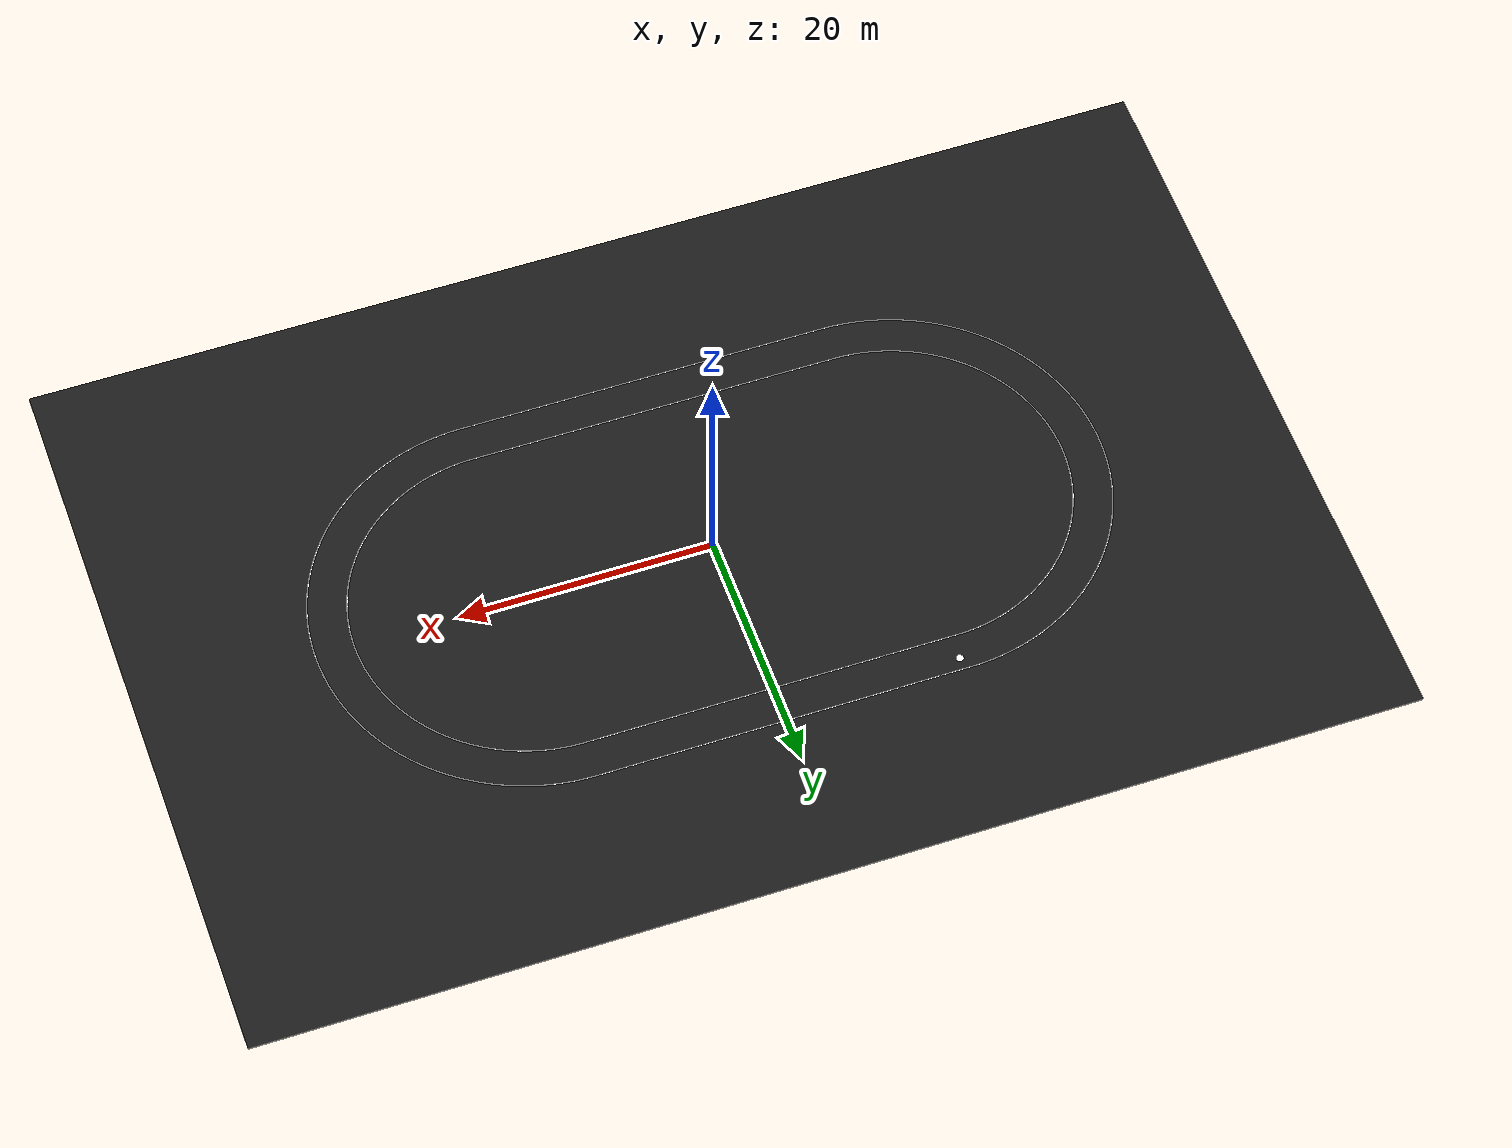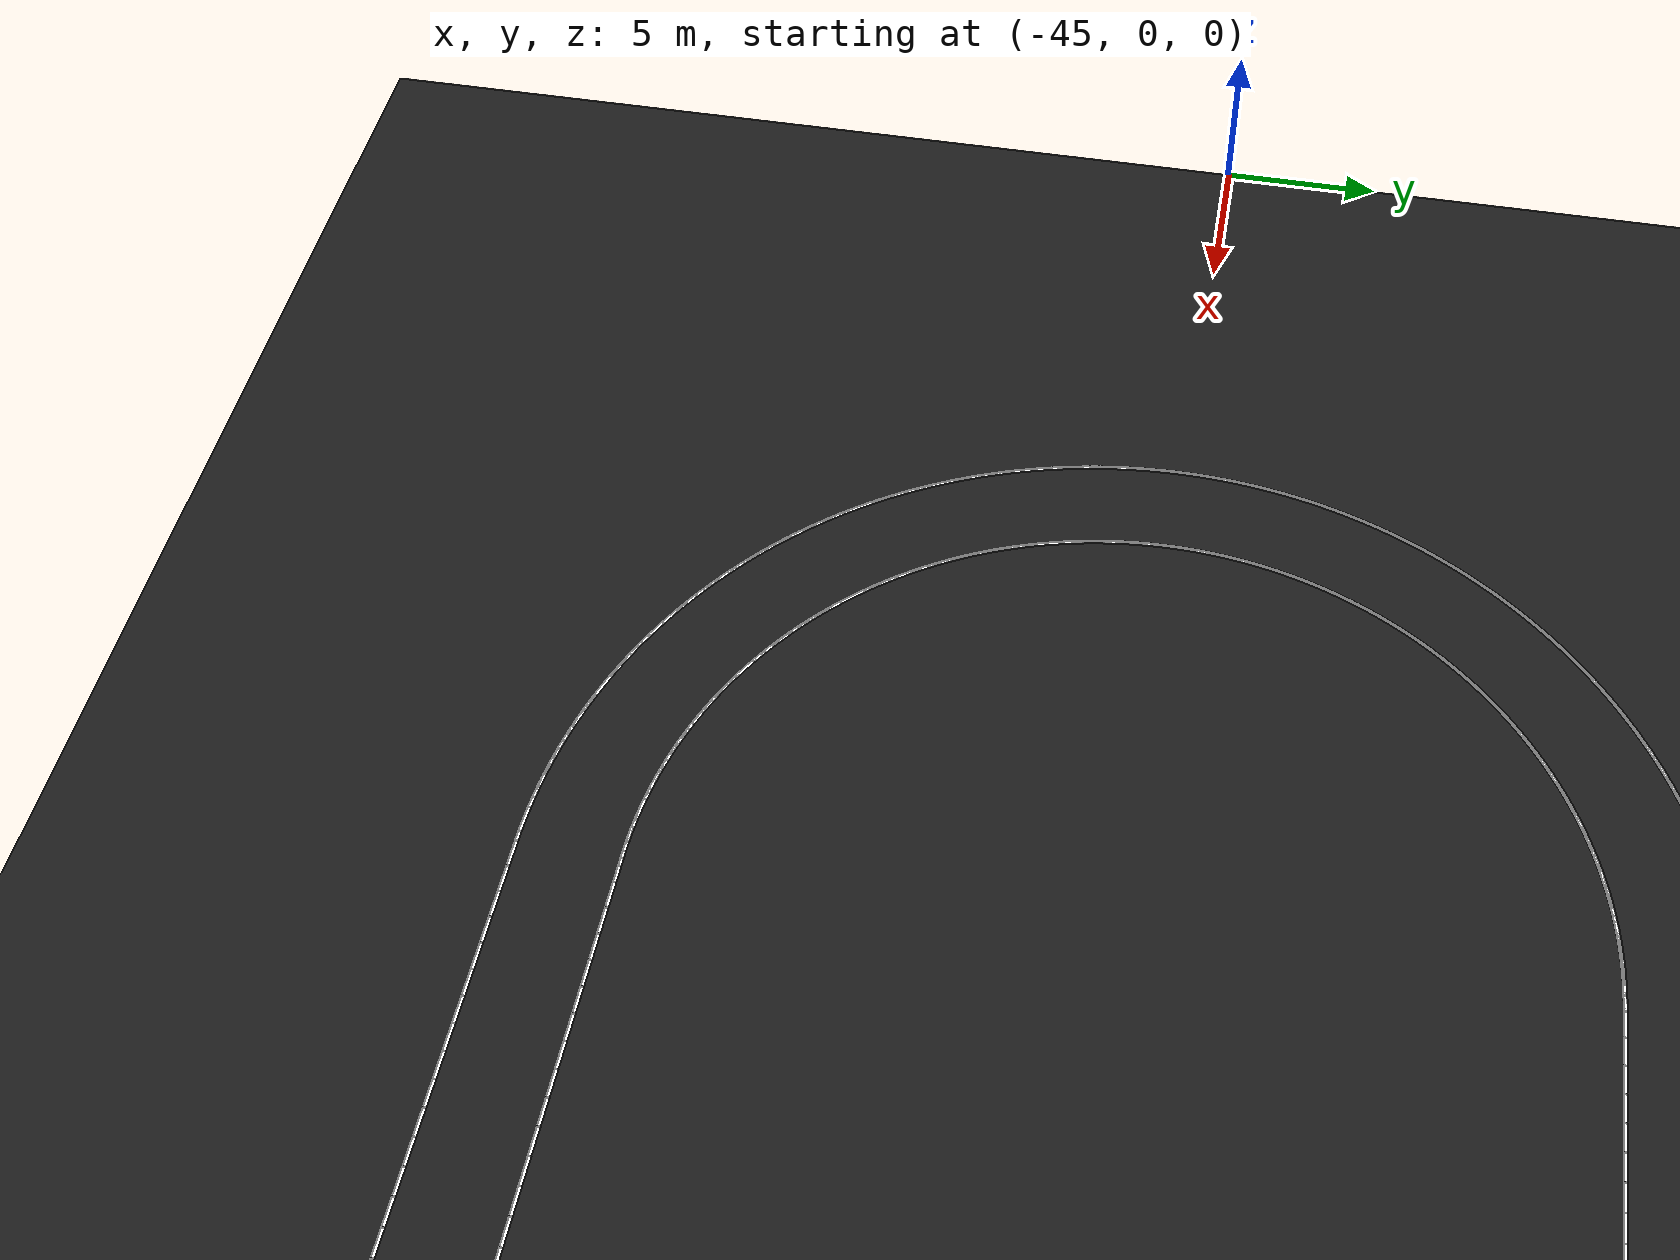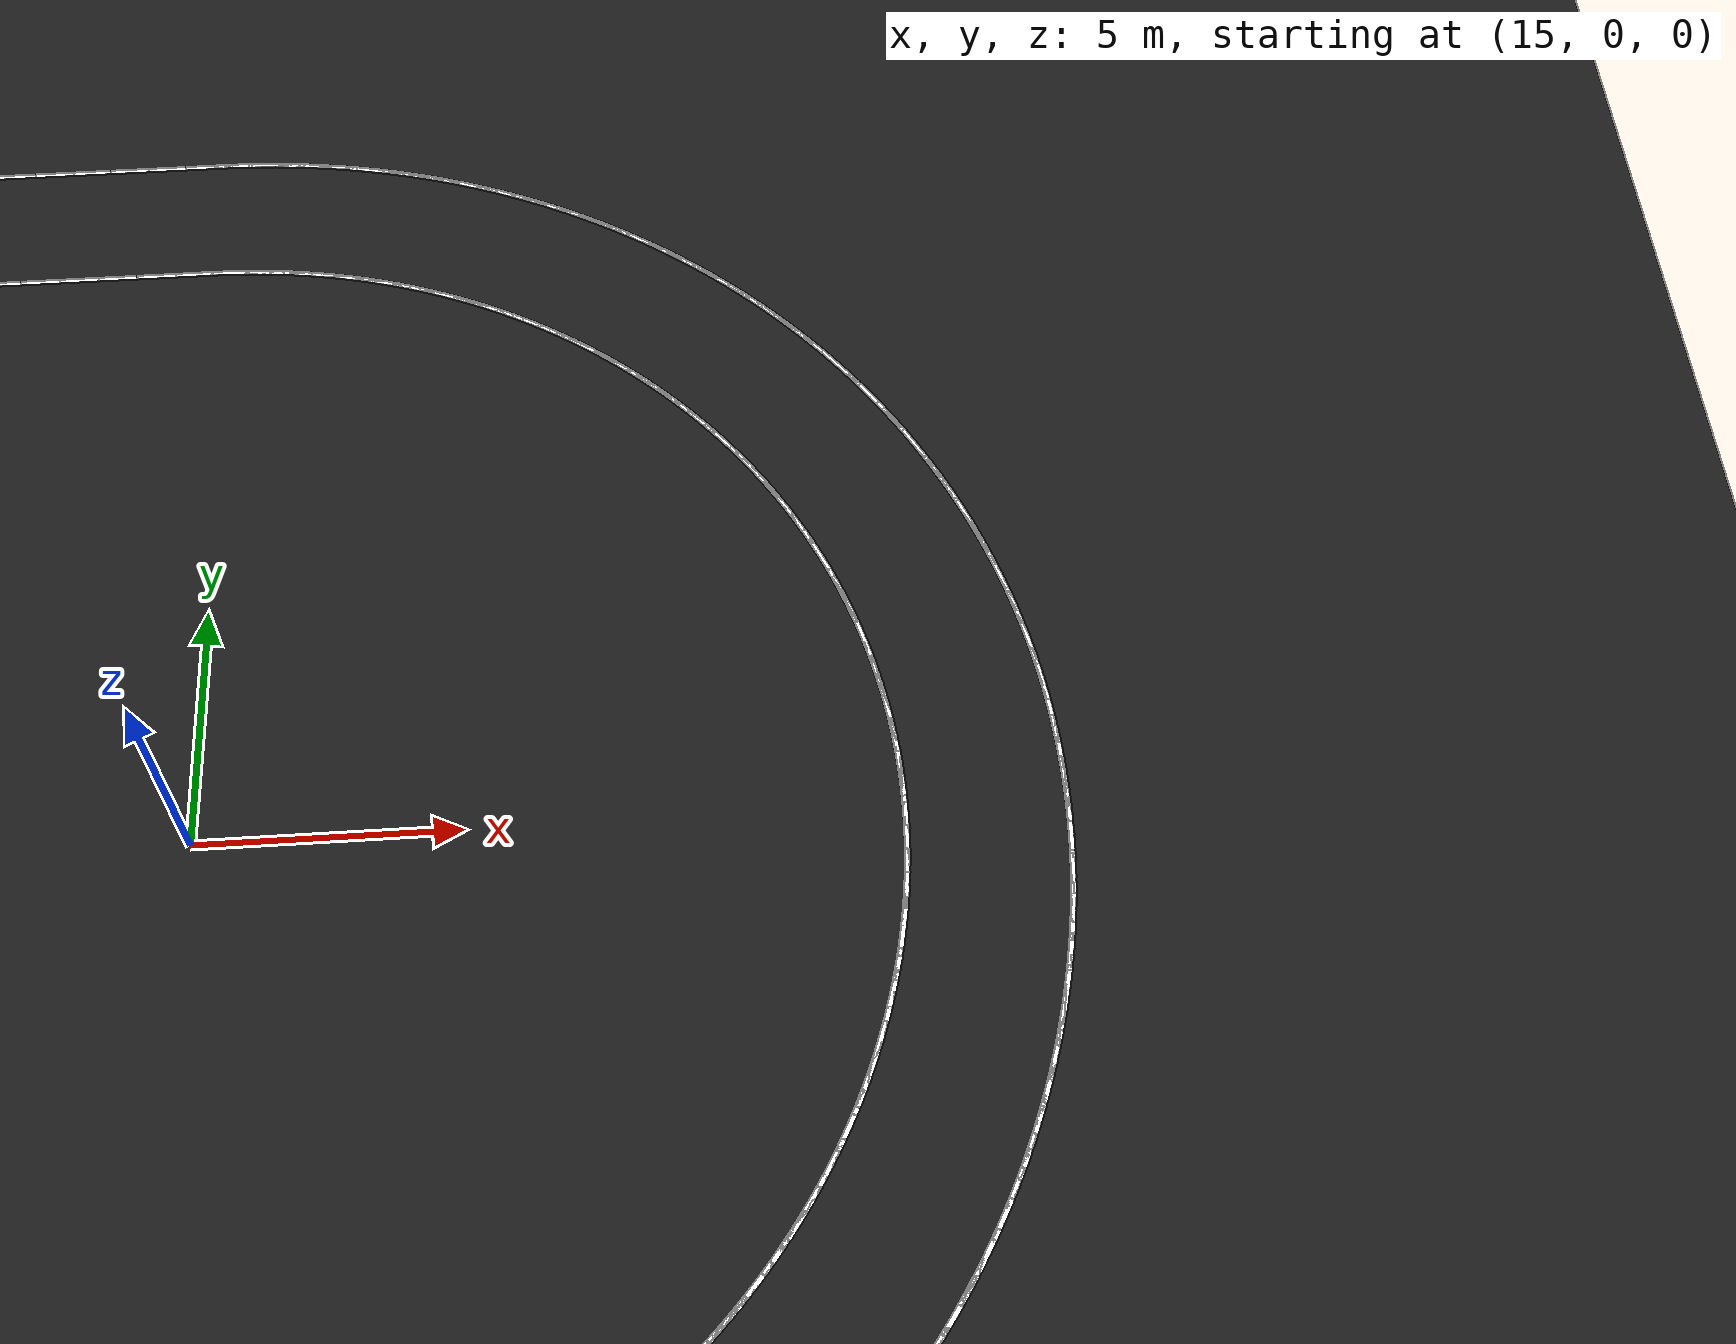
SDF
<sdf version="1.9">
 <world name="pavbot_test_world_oval">
  <physics name="1ms" type="ignored">
   <max_step_size>0.001</max_step_size>
   <real_time_factor>1.0</real_time_factor>
  </physics>
  <plugin filename="libgz-sim8-physics-system.so" name="gz::sim::systems::Physics"/>
  <plugin filename="gz-sim-sensors-system" name="gz::sim::systems::Sensors"/>
  <plugin filename="libgz-sim8-scene-broadcaster-system.so" name="gz::sim::systems::SceneBroadcaster"/>
  <include><uri>https://fuel.gazebosim.org/1.0/openrobotics/models/Sun</uri></include>
  <model name="oval_track">
   <static>true</static>
   <link name="track_link">
    <collision name="track_collision">
     <pose>0 0 -0.05 0 0 0</pose>
     <geometry><box><size>90 60 0.10</size></box></geometry>
     <surface><friction><ode><mu>1.2</mu><mu2>1.2</mu2></ode></friction></surface>
    </collision>
    <visual name="track_visual">
     <pose>0 0 -0.05 0 0 0</pose>
     <geometry><box><size>90 60 0.10</size></box></geometry>
     <material>
      <ambient>0.08 0.08 0.08 1</ambient>
      <diffuse>0.10 0.10 0.10 1</diffuse>
      <specular>0.02 0.02 0.02 1</specular>
     </material>
    </visual>
    <visual name="outer_lane_000">
     <pose>-14.1312 16.5000 0.0 0 0 0.000000</pose>
     <geometry><box><size>0.8000 0.1000 0.0050</size></box></geometry>
     <material><ambient>1 1 1 1</ambient><diffuse>1 1 1 1</diffuse><specular>0.1 0.1 0.1 1</specular></material>
    </visual>
    <visual name="outer_lane_001">
     <pose>-13.3238 16.5000 0.0 0 0 0.000000</pose>
     <geometry><box><size>0.8000 0.1000 0.0050</size></box></geometry>
     <material><ambient>1 1 1 1</ambient><diffuse>1 1 1 1</diffuse><specular>0.1 0.1 0.1 1</specular></material>
    </visual>
    <visual name="outer_lane_002">
     <pose>-12.5162 16.5000 0.0 0 0 0.000000</pose>
     <geometry><box><size>0.8000 0.1000 0.0050</size></box></geometry>
     <material><ambient>1 1 1 1</ambient><diffuse>1 1 1 1</diffuse><specular>0.1 0.1 0.1 1</specular></material>
    </visual>
    <visual name="outer_lane_003">
     <pose>-11.7088 16.5000 0.0 0 0 0.000000</pose>
     <geometry><box><size>0.8000 0.1000 0.0050</size></box></geometry>
     <material><ambient>1 1 1 1</ambient><diffuse>1 1 1 1</diffuse><specular>0.1 0.1 0.1 1</specular></material>
    </visual>
    <visual name="outer_lane_004">
     <pose>-10.9013 16.5000 0.0 0 0 0.000000</pose>
     <geometry><box><size>0.8000 0.1000 0.0050</size></box></geometry>
     <material><ambient>1 1 1 1</ambient><diffuse>1 1 1 1</diffuse><specular>0.1 0.1 0.1 1</specular></material>
    </visual>
    <visual name="outer_lane_005">
     <pose>-10.0938 16.5000 0.0 0 0 0.000000</pose>
     <geometry><box><size>0.8000 0.1000 0.0050</size></box></geometry>
     <material><ambient>1 1 1 1</ambient><diffuse>1 1 1 1</diffuse><specular>0.1 0.1 0.1 1</specular></material>
    </visual>
    <visual name="outer_lane_006">
     <pose>-9.2862 16.5000 0.0 0 0 0.000000</pose>
     <geometry><box><size>0.8000 0.1000 0.0050</size></box></geometry>
     <material><ambient>1 1 1 1</ambient><diffuse>1 1 1 1</diffuse><specular>0.1 0.1 0.1 1</specular></material>
    </visual>
    <visual name="outer_lane_007">
     <pose>-8.4787 16.5000 0.0 0 0 0.000000</pose>
     <geometry><box><size>0.8000 0.1000 0.0050</size></box></geometry>
     <material><ambient>1 1 1 1</ambient><diffuse>1 1 1 1</diffuse><specular>0.1 0.1 0.1 1</specular></material>
    </visual>
    <visual name="outer_lane_008">
     <pose>-7.6713 16.5000 0.0 0 0 0.000000</pose>
     <geometry><box><size>0.8000 0.1000 0.0050</size></box></geometry>
     <material><ambient>1 1 1 1</ambient><diffuse>1 1 1 1</diffuse><specular>0.1 0.1 0.1 1</specular></material>
    </visual>
    <visual name="outer_lane_009">
     <pose>-6.8638 16.5000 0.0 0 0 0.000000</pose>
     <geometry><box><size>0.8000 0.1000 0.0050</size></box></geometry>
     <material><ambient>1 1 1 1</ambient><diffuse>1 1 1 1</diffuse><specular>0.1 0.1 0.1 1</specular></material>
    </visual>
    <visual name="outer_lane_010">
     <pose>-6.0563 16.5000 0.0 0 0 0.000000</pose>
     <geometry><box><size>0.8000 0.1000 0.0050</size></box></geometry>
     <material><ambient>1 1 1 1</ambient><diffuse>1 1 1 1</diffuse><specular>0.1 0.1 0.1 1</specular></material>
    </visual>
    <visual name="outer_lane_011">
     <pose>-5.2487 16.5000 0.0 0 0 0.000000</pose>
     <geometry><box><size>0.8000 0.1000 0.0050</size></box></geometry>
     <material><ambient>1 1 1 1</ambient><diffuse>1 1 1 1</diffuse><specular>0.1 0.1 0.1 1</specular></material>
    </visual>
    <visual name="outer_lane_012">
     <pose>-4.4413 16.5000 0.0 0 0 0.000000</pose>
     <geometry><box><size>0.8000 0.1000 0.0050</size></box></geometry>
     <material><ambient>1 1 1 1</ambient><diffuse>1 1 1 1</diffuse><specular>0.1 0.1 0.1 1</specular></material>
    </visual>
    <visual name="outer_lane_013">
     <pose>-3.6338 16.5000 0.0 0 0 0.000000</pose>
     <geometry><box><size>0.8000 0.1000 0.0050</size></box></geometry>
     <material><ambient>1 1 1 1</ambient><diffuse>1 1 1 1</diffuse><specular>0.1 0.1 0.1 1</specular></material>
    </visual>
    <visual name="outer_lane_014">
     <pose>-2.8262 16.5000 0.0 0 0 0.000000</pose>
     <geometry><box><size>0.8000 0.1000 0.0050</size></box></geometry>
     <material><ambient>1 1 1 1</ambient><diffuse>1 1 1 1</diffuse><specular>0.1 0.1 0.1 1</specular></material>
    </visual>
    <visual name="outer_lane_015">
     <pose>-2.0188 16.5000 0.0 0 0 0.000000</pose>
     <geometry><box><size>0.8000 0.1000 0.0050</size></box></geometry>
     <material><ambient>1 1 1 1</ambient><diffuse>1 1 1 1</diffuse><specular>0.1 0.1 0.1 1</specular></material>
    </visual>
    <visual name="outer_lane_016">
     <pose>-1.2112 16.5000 0.0 0 0 0.000000</pose>
     <geometry><box><size>0.8000 0.1000 0.0050</size></box></geometry>
     <material><ambient>1 1 1 1</ambient><diffuse>1 1 1 1</diffuse><specular>0.1 0.1 0.1 1</specular></material>
    </visual>
    <visual name="outer_lane_017">
     <pose>-0.4038 16.5000 0.0 0 0 0.000000</pose>
     <geometry><box><size>0.8000 0.1000 0.0050</size></box></geometry>
     <material><ambient>1 1 1 1</ambient><diffuse>1 1 1 1</diffuse><specular>0.1 0.1 0.1 1</specular></material>
    </visual>
    <visual name="outer_lane_018">
     <pose>0.4038 16.5000 0.0 0 0 0.000000</pose>
     <geometry><box><size>0.8000 0.1000 0.0050</size></box></geometry>
     <material><ambient>1 1 1 1</ambient><diffuse>1 1 1 1</diffuse><specular>0.1 0.1 0.1 1</specular></material>
    </visual>
    <visual name="outer_lane_019">
     <pose>1.2112 16.5000 0.0 0 0 0.000000</pose>
     <geometry><box><size>0.8000 0.1000 0.0050</size></box></geometry>
     <material><ambient>1 1 1 1</ambient><diffuse>1 1 1 1</diffuse><specular>0.1 0.1 0.1 1</specular></material>
    </visual>
    <visual name="outer_lane_020">
     <pose>2.0188 16.5000 0.0 0 0 0.000000</pose>
     <geometry><box><size>0.8000 0.1000 0.0050</size></box></geometry>
     <material><ambient>1 1 1 1</ambient><diffuse>1 1 1 1</diffuse><specular>0.1 0.1 0.1 1</specular></material>
    </visual>
    <visual name="outer_lane_021">
     <pose>2.8262 16.5000 0.0 0 0 0.000000</pose>
     <geometry><box><size>0.8000 0.1000 0.0050</size></box></geometry>
     <material><ambient>1 1 1 1</ambient><diffuse>1 1 1 1</diffuse><specular>0.1 0.1 0.1 1</specular></material>
    </visual>
    <visual name="outer_lane_022">
     <pose>3.6337 16.5000 0.0 0 0 0.000000</pose>
     <geometry><box><size>0.8000 0.1000 0.0050</size></box></geometry>
     <material><ambient>1 1 1 1</ambient><diffuse>1 1 1 1</diffuse><specular>0.1 0.1 0.1 1</specular></material>
    </visual>
    <visual name="outer_lane_023">
     <pose>4.4413 16.5000 0.0 0 0 0.000000</pose>
     <geometry><box><size>0.8000 0.1000 0.0050</size></box></geometry>
     <material><ambient>1 1 1 1</ambient><diffuse>1 1 1 1</diffuse><specular>0.1 0.1 0.1 1</specular></material>
    </visual>
    <visual name="outer_lane_024">
     <pose>5.2488 16.5000 0.0 0 0 0.000000</pose>
     <geometry><box><size>0.8000 0.1000 0.0050</size></box></geometry>
     <material><ambient>1 1 1 1</ambient><diffuse>1 1 1 1</diffuse><specular>0.1 0.1 0.1 1</specular></material>
    </visual>
    <visual name="outer_lane_025">
     <pose>6.0562 16.5000 0.0 0 0 0.000000</pose>
     <geometry><box><size>0.8000 0.1000 0.0050</size></box></geometry>
     <material><ambient>1 1 1 1</ambient><diffuse>1 1 1 1</diffuse><specular>0.1 0.1 0.1 1</specular></material>
    </visual>
    <visual name="outer_lane_026">
     <pose>6.8637 16.5000 0.0 0 0 0.000000</pose>
     <geometry><box><size>0.8000 0.1000 0.0050</size></box></geometry>
     <material><ambient>1 1 1 1</ambient><diffuse>1 1 1 1</diffuse><specular>0.1 0.1 0.1 1</specular></material>
    </visual>
    <visual name="outer_lane_027">
     <pose>7.6713 16.5000 0.0 0 0 0.000000</pose>
     <geometry><box><size>0.8000 0.1000 0.0050</size></box></geometry>
     <material><ambient>1 1 1 1</ambient><diffuse>1 1 1 1</diffuse><specular>0.1 0.1 0.1 1</specular></material>
    </visual>
    <visual name="outer_lane_028">
     <pose>8.4787 16.5000 0.0 0 0 0.000000</pose>
     <geometry><box><size>0.8000 0.1000 0.0050</size></box></geometry>
     <material><ambient>1 1 1 1</ambient><diffuse>1 1 1 1</diffuse><specular>0.1 0.1 0.1 1</specular></material>
    </visual>
    <visual name="outer_lane_029">
     <pose>9.2862 16.5000 0.0 0 0 0.000000</pose>
     <geometry><box><size>0.8000 0.1000 0.0050</size></box></geometry>
     <material><ambient>1 1 1 1</ambient><diffuse>1 1 1 1</diffuse><specular>0.1 0.1 0.1 1</specular></material>
    </visual>
    <visual name="outer_lane_030">
     <pose>10.0938 16.5000 0.0 0 0 0.000000</pose>
     <geometry><box><size>0.8000 0.1000 0.0050</size></box></geometry>
     <material><ambient>1 1 1 1</ambient><diffuse>1 1 1 1</diffuse><specular>0.1 0.1 0.1 1</specular></material>
    </visual>
    <visual name="outer_lane_031">
     <pose>10.9013 16.5000 0.0 0 0 0.000000</pose>
     <geometry><box><size>0.8000 0.1000 0.0050</size></box></geometry>
     <material><ambient>1 1 1 1</ambient><diffuse>1 1 1 1</diffuse><specular>0.1 0.1 0.1 1</specular></material>
    </visual>
    <visual name="outer_lane_032">
     <pose>11.7087 16.5000 0.0 0 0 0.000000</pose>
     <geometry><box><size>0.8000 0.1000 0.0050</size></box></geometry>
     <material><ambient>1 1 1 1</ambient><diffuse>1 1 1 1</diffuse><specular>0.1 0.1 0.1 1</specular></material>
    </visual>
    <visual name="outer_lane_033">
     <pose>12.5162 16.5000 0.0 0 0 0.000000</pose>
     <geometry><box><size>0.8000 0.1000 0.0050</size></box></geometry>
     <material><ambient>1 1 1 1</ambient><diffuse>1 1 1 1</diffuse><specular>0.1 0.1 0.1 1</specular></material>
    </visual>
    <visual name="outer_lane_034">
     <pose>13.3238 16.5000 0.0 0 0 0.000000</pose>
     <geometry><box><size>0.8000 0.1000 0.0050</size></box></geometry>
     <material><ambient>1 1 1 1</ambient><diffuse>1 1 1 1</diffuse><specular>0.1 0.1 0.1 1</specular></material>
    </visual>
    <visual name="outer_lane_035">
     <pose>14.1313 16.5000 0.0 0 0 0.000000</pose>
     <geometry><box><size>0.8000 0.1000 0.0050</size></box></geometry>
     <material><ambient>1 1 1 1</ambient><diffuse>1 1 1 1</diffuse><specular>0.1 0.1 0.1 1</specular></material>
    </visual>
    <visual name="outer_lane_036">
     <pose>14.6790 -16.4994 0.0 0 0 0.008727</pose>
     <geometry><box><size>0.8000 0.1000 0.0050</size></box></geometry>
     <material><ambient>1 1 1 1</ambient><diffuse>1 1 1 1</diffuse><specular>0.1 0.1 0.1 1</specular></material>
    </visual>
    <visual name="outer_lane_037">
     <pose>14.9669 -16.4943 0.0 0 0 0.026180</pose>
     <geometry><box><size>0.8000 0.1000 0.0050</size></box></geometry>
     <material><ambient>1 1 1 1</ambient><diffuse>1 1 1 1</diffuse><specular>0.1 0.1 0.1 1</specular></material>
    </visual>
    <visual name="outer_lane_038">
     <pose>15.2547 -16.4843 0.0 0 0 0.043633</pose>
     <geometry><box><size>0.8000 0.1000 0.0050</size></box></geometry>
     <material><ambient>1 1 1 1</ambient><diffuse>1 1 1 1</diffuse><specular>0.1 0.1 0.1 1</specular></material>
    </visual>
    <visual name="outer_lane_039">
     <pose>15.5423 -16.4692 0.0 0 0 0.061087</pose>
     <geometry><box><size>0.8000 0.1000 0.0050</size></box></geometry>
     <material><ambient>1 1 1 1</ambient><diffuse>1 1 1 1</diffuse><specular>0.1 0.1 0.1 1</specular></material>
    </visual>
    <visual name="outer_lane_040">
     <pose>15.8296 -16.4491 0.0 0 0 0.078540</pose>
     <geometry><box><size>0.8000 0.1000 0.0050</size></box></geometry>
     <material><ambient>1 1 1 1</ambient><diffuse>1 1 1 1</diffuse><specular>0.1 0.1 0.1 1</specular></material>
    </visual>
    <visual name="outer_lane_041">
     <pose>16.1165 -16.4240 0.0 0 0 0.095993</pose>
     <geometry><box><size>0.8000 0.1000 0.0050</size></box></geometry>
     <material><ambient>1 1 1 1</ambient><diffuse>1 1 1 1</diffuse><specular>0.1 0.1 0.1 1</specular></material>
    </visual>
    <visual name="outer_lane_042">
     <pose>16.4029 -16.3939 0.0 0 0 0.113446</pose>
     <geometry><box><size>0.8000 0.1000 0.0050</size></box></geometry>
     <material><ambient>1 1 1 1</ambient><diffuse>1 1 1 1</diffuse><specular>0.1 0.1 0.1 1</specular></material>
    </visual>
    <visual name="outer_lane_043">
     <pose>16.6887 -16.3588 0.0 0 0 0.130900</pose>
     <geometry><box><size>0.8000 0.1000 0.0050</size></box></geometry>
     <material><ambient>1 1 1 1</ambient><diffuse>1 1 1 1</diffuse><specular>0.1 0.1 0.1 1</specular></material>
    </visual>
    <visual name="outer_lane_044">
     <pose>16.9739 -16.3188 0.0 0 0 0.148353</pose>
     <geometry><box><size>0.8000 0.1000 0.0050</size></box></geometry>
     <material><ambient>1 1 1 1</ambient><diffuse>1 1 1 1</diffuse><specular>0.1 0.1 0.1 1</specular></material>
    </visual>
    <visual name="outer_lane_045">
     <pose>17.2583 -16.2737 0.0 0 0 0.165806</pose>
     <geometry><box><size>0.8000 0.1000 0.0050</size></box></geometry>
     <material><ambient>1 1 1 1</ambient><diffuse>1 1 1 1</diffuse><specular>0.1 0.1 0.1 1</specular></material>
    </visual>
    <visual name="outer_lane_046">
     <pose>17.5419 -16.2237 0.0 0 0 0.183260</pose>
     <geometry><box><size>0.8000 0.1000 0.0050</size></box></geometry>
     <material><ambient>1 1 1 1</ambient><diffuse>1 1 1 1</diffuse><specular>0.1 0.1 0.1 1</specular></material>
    </visual>
    <visual name="outer_lane_047">
     <pose>17.8246 -16.1688 0.0 0 0 0.200713</pose>
     <geometry><box><size>0.8000 0.1000 0.0050</size></box></geometry>
     <material><ambient>1 1 1 1</ambient><diffuse>1 1 1 1</diffuse><specular>0.1 0.1 0.1 1</specular></material>
    </visual>
    <visual name="outer_lane_048">
     <pose>18.1063 -16.1089 0.0 0 0 0.218166</pose>
     <geometry><box><size>0.8000 0.1000 0.0050</size></box></geometry>
     <material><ambient>1 1 1 1</ambient><diffuse>1 1 1 1</diffuse><specular>0.1 0.1 0.1 1</specular></material>
    </visual>
    <visual name="outer_lane_049">
     <pose>18.3868 -16.0441 0.0 0 0 0.235619</pose>
     <geometry><box><size>0.8000 0.1000 0.0050</size></box></geometry>
     <material><ambient>1 1 1 1</ambient><diffuse>1 1 1 1</diffuse><specular>0.1 0.1 0.1 1</specular></material>
    </visual>
    <visual name="outer_lane_050">
     <pose>18.6663 -15.9744 0.0 0 0 0.253073</pose>
     <geometry><box><size>0.8000 0.1000 0.0050</size></box></geometry>
     <material><ambient>1 1 1 1</ambient><diffuse>1 1 1 1</diffuse><specular>0.1 0.1 0.1 1</specular></material>
    </visual>
    <visual name="outer_lane_051">
     <pose>18.9444 -15.8999 0.0 0 0 0.270526</pose>
     <geometry><box><size>0.8000 0.1000 0.0050</size></box></geometry>
     <material><ambient>1 1 1 1</ambient><diffuse>1 1 1 1</diffuse><specular>0.1 0.1 0.1 1</specular></material>
    </visual>
    <visual name="outer_lane_052">
     <pose>19.2213 -15.8205 0.0 0 0 0.287979</pose>
     <geometry><box><size>0.8000 0.1000 0.0050</size></box></geometry>
     <material><ambient>1 1 1 1</ambient><diffuse>1 1 1 1</diffuse><specular>0.1 0.1 0.1 1</specular></material>
    </visual>
    <visual name="outer_lane_053">
     <pose>19.4966 -15.7363 0.0 0 0 0.305433</pose>
     <geometry><box><size>0.8000 0.1000 0.0050</size></box></geometry>
     <material><ambient>1 1 1 1</ambient><diffuse>1 1 1 1</diffuse><specular>0.1 0.1 0.1 1</specular></material>
    </visual>
    <visual name="outer_lane_054">
     <pose>19.7705 -15.6473 0.0 0 0 0.322886</pose>
     <geometry><box><size>0.8000 0.1000 0.0050</size></box></geometry>
     <material><ambient>1 1 1 1</ambient><diffuse>1 1 1 1</diffuse><specular>0.1 0.1 0.1 1</specular></material>
    </visual>
    <visual name="outer_lane_055">
     <pose>20.0428 -15.5536 0.0 0 0 0.340339</pose>
     <geometry><box><size>0.8000 0.1000 0.0050</size></box></geometry>
     <material><ambient>1 1 1 1</ambient><diffuse>1 1 1 1</diffuse><specular>0.1 0.1 0.1 1</specular></material>
    </visual>
    <visual name="outer_lane_056">
     <pose>20.3134 -15.4551 0.0 0 0 0.357792</pose>
     <geometry><box><size>0.8000 0.1000 0.0050</size></box></geometry>
     <material><ambient>1 1 1 1</ambient><diffuse>1 1 1 1</diffuse><specular>0.1 0.1 0.1 1</specular></material>
    </visual>
    <visual name="outer_lane_057">
     <pose>20.5823 -15.3519 0.0 0 0 0.375246</pose>
     <geometry><box><size>0.8000 0.1000 0.0050</size></box></geometry>
     <material><ambient>1 1 1 1</ambient><diffuse>1 1 1 1</diffuse><specular>0.1 0.1 0.1 1</specular></material>
    </visual>
    <visual name="outer_lane_058">
     <pose>20.8493 -15.2440 0.0 0 0 0.392699</pose>
     <geometry><box><size>0.8000 0.1000 0.0050</size></box></geometry>
     <material><ambient>1 1 1 1</ambient><diffuse>1 1 1 1</diffuse><specular>0.1 0.1 0.1 1</specular></material>
    </visual>
    <visual name="outer_lane_059">
     <pose>21.1144 -15.1315 0.0 0 0 0.410152</pose>
     <geometry><box><size>0.8000 0.1000 0.0050</size></box></geometry>
     <material><ambient>1 1 1 1</ambient><diffuse>1 1 1 1</diffuse><specular>0.1 0.1 0.1 1</specular></material>
    </visual>
    <visual name="outer_lane_060">
     <pose>21.3774 -15.0144 0.0 0 0 0.427606</pose>
     <geometry><box><size>0.8000 0.1000 0.0050</size></box></geometry>
     <material><ambient>1 1 1 1</ambient><diffuse>1 1 1 1</diffuse><specular>0.1 0.1 0.1 1</specular></material>
    </visual>
    <visual name="outer_lane_061">
     <pose>21.6384 -14.8927 0.0 0 0 0.445059</pose>
     <geometry><box><size>0.8000 0.1000 0.0050</size></box></geometry>
     <material><ambient>1 1 1 1</ambient><diffuse>1 1 1 1</diffuse><specular>0.1 0.1 0.1 1</specular></material>
    </visual>
    <visual name="outer_lane_062">
     <pose>21.8973 -14.7664 0.0 0 0 0.462512</pose>
     <geometry><box><size>0.8000 0.1000 0.0050</size></box></geometry>
     <material><ambient>1 1 1 1</ambient><diffuse>1 1 1 1</diffuse><specular>0.1 0.1 0.1 1</specular></material>
    </visual>
    <visual name="outer_lane_063">
     <pose>22.1539 -14.6357 0.0 0 0 0.479966</pose>
     <geometry><box><size>0.8000 0.1000 0.0050</size></box></geometry>
     <material><ambient>1 1 1 1</ambient><diffuse>1 1 1 1</diffuse><specular>0.1 0.1 0.1 1</specular></material>
    </visual>
    <visual name="outer_lane_064">
     <pose>22.4081 -14.5005 0.0 0 0 0.497419</pose>
     <geometry><box><size>0.8000 0.1000 0.0050</size></box></geometry>
     <material><ambient>1 1 1 1</ambient><diffuse>1 1 1 1</diffuse><specular>0.1 0.1 0.1 1</specular></material>
    </visual>
    <visual name="outer_lane_065">
     <pose>22.6600 -14.3609 0.0 0 0 0.514872</pose>
     <geometry><box><size>0.8000 0.1000 0.0050</size></box></geometry>
     <material><ambient>1 1 1 1</ambient><diffuse>1 1 1 1</diffuse><specular>0.1 0.1 0.1 1</specular></material>
    </visual>
    <visual name="outer_lane_066">
     <pose>22.9094 -14.2169 0.0 0 0 0.532325</pose>
     <geometry><box><size>0.8000 0.1000 0.0050</size></box></geometry>
     <material><ambient>1 1 1 1</ambient><diffuse>1 1 1 1</diffuse><specular>0.1 0.1 0.1 1</specular></material>
    </visual>
    <visual name="outer_lane_067">
     <pose>23.1562 -14.0686 0.0 0 0 0.549779</pose>
     <geometry><box><size>0.8000 0.1000 0.0050</size></box></geometry>
     <material><ambient>1 1 1 1</ambient><diffuse>1 1 1 1</diffuse><specular>0.1 0.1 0.1 1</specular></material>
    </visual>
    <visual name="outer_lane_068">
     <pose>23.4004 -13.9160 0.0 0 0 0.567232</pose>
     <geometry><box><size>0.8000 0.1000 0.0050</size></box></geometry>
     <material><ambient>1 1 1 1</ambient><diffuse>1 1 1 1</diffuse><specular>0.1 0.1 0.1 1</specular></material>
    </visual>
    <visual name="outer_lane_069">
     <pose>23.6420 -13.7591 0.0 0 0 0.584685</pose>
     <geometry><box><size>0.8000 0.1000 0.0050</size></box></geometry>
     <material><ambient>1 1 1 1</ambient><diffuse>1 1 1 1</diffuse><specular>0.1 0.1 0.1 1</specular></material>
    </visual>
    <visual name="outer_lane_070">
     <pose>23.8807 -13.5981 0.0 0 0 0.602139</pose>
     <geometry><box><size>0.8000 0.1000 0.0050</size></box></geometry>
     <material><ambient>1 1 1 1</ambient><diffuse>1 1 1 1</diffuse><specular>0.1 0.1 0.1 1</specular></material>
    </visual>
    <visual name="outer_lane_071">
     <pose>24.1166 -13.4329 0.0 0 0 0.619592</pose>
     <geometry><box><size>0.8000 0.1000 0.0050</size></box></geometry>
     <material><ambient>1 1 1 1</ambient><diffuse>1 1 1 1</diffuse><specular>0.1 0.1 0.1 1</specular></material>
    </visual>
    <visual name="outer_lane_072">
     <pose>24.3496 -13.2636 0.0 0 0 0.637045</pose>
     <geometry><box><size>0.8000 0.1000 0.0050</size></box></geometry>
     <material><ambient>1 1 1 1</ambient><diffuse>1 1 1 1</diffuse><specular>0.1 0.1 0.1 1</specular></material>
    </visual>
    <visual name="outer_lane_073">
     <pose>24.5796 -13.0903 0.0 0 0 0.654498</pose>
     <geometry><box><size>0.8000 0.1000 0.0050</size></box></geometry>
     <material><ambient>1 1 1 1</ambient><diffuse>1 1 1 1</diffuse><specular>0.1 0.1 0.1 1</specular></material>
    </visual>
    <visual name="outer_lane_074">
     <pose>24.8065 -12.9130 0.0 0 0 0.671952</pose>
     <geometry><box><size>0.8000 0.1000 0.0050</size></box></geometry>
     <material><ambient>1 1 1 1</ambient><diffuse>1 1 1 1</diffuse><specular>0.1 0.1 0.1 1</specular></material>
    </visual>
    <visual name="outer_lane_075">
     <pose>25.0303 -12.7318 0.0 0 0 0.689405</pose>
     <geometry><box><size>0.8000 0.1000 0.0050</size></box></geometry>
     <material><ambient>1 1 1 1</ambient><diffuse>1 1 1 1</diffuse><specular>0.1 0.1 0.1 1</specular></material>
    </visual>
    <visual name="outer_lane_076">
     <pose>25.2509 -12.5467 0.0 0 0 0.706858</pose>
     <geometry><box><size>0.8000 0.1000 0.0050</size></box></geometry>
     <material><ambient>1 1 1 1</ambient><diffuse>1 1 1 1</diffuse><specular>0.1 0.1 0.1 1</specular></material>
    </visual>
    <visual name="outer_lane_077">
     <pose>25.4682 -12.3578 0.0 0 0 0.724312</pose>
     <geometry><box><size>0.8000 0.1000 0.0050</size></box></geometry>
     <material><ambient>1 1 1 1</ambient><diffuse>1 1 1 1</diffuse><specular>0.1 0.1 0.1 1</specular></material>
    </visual>
    <visual name="outer_lane_078">
     <pose>25.6822 -12.1651 0.0 0 0 0.741765</pose>
     <geometry><box><size>0.8000 0.1000 0.0050</size></box></geometry>
     <material><ambient>1 1 1 1</ambient><diffuse>1 1 1 1</diffuse><specular>0.1 0.1 0.1 1</specular></material>
    </visual>
    <visual name="outer_lane_079">
     <pose>25.8929 -11.9687 0.0 0 0 0.759218</pose>
     <geometry><box><size>0.8000 0.1000 0.0050</size></box></geometry>
     <material><ambient>1 1 1 1</ambient><diffuse>1 1 1 1</diffuse><specular>0.1 0.1 0.1 1</specular></material>
    </visual>
    <visual name="outer_lane_080">
     <pose>26.1000 -11.7686 0.0 0 0 0.776672</pose>
     <geometry><box><size>0.8000 0.1000 0.0050</size></box></geometry>
     <material><ambient>1 1 1 1</ambient><diffuse>1 1 1 1</diffuse><specular>0.1 0.1 0.1 1</specular></material>
    </visual>
    <visual name="outer_lane_081">
     <pose>26.3036 -11.5650 0.0 0 0 0.794125</pose>
     <geometry><box><size>0.8000 0.1000 0.0050</size></box></geometry>
     <material><ambient>1 1 1 1</ambient><diffuse>1 1 1 1</diffuse><specular>0.1 0.1 0.1 1</specular></material>
    </visual>
    <visual name="outer_lane_082">
     <pose>26.5037 -11.3579 0.0 0 0 0.811578</pose>
     <geometry><box><size>0.8000 0.1000 0.0050</size></box></geometry>
     <material><ambient>1 1 1 1</ambient><diffuse>1 1 1 1</diffuse><specular>0.1 0.1 0.1 1</specular></material>
    </visual>
    <visual name="outer_lane_083">
     <pose>26.7001 -11.1472 0.0 0 0 0.829031</pose>
     <geometry><box><size>0.8000 0.1000 0.0050</size></box></geometry>
     <material><ambient>1 1 1 1</ambient><diffuse>1 1 1 1</diffuse><specular>0.1 0.1 0.1 1</specular></material>
    </visual>
    <visual name="outer_lane_084">
     <pose>26.8928 -10.9332 0.0 0 0 0.846485</pose>
     <geometry><box><size>0.8000 0.1000 0.0050</size></box></geometry>
     <material><ambient>1 1 1 1</ambient><diffuse>1 1 1 1</diffuse><specular>0.1 0.1 0.1 1</specular></material>
    </visual>
    <visual name="outer_lane_085">
     <pose>27.0817 -10.7159 0.0 0 0 0.863938</pose>
     <geometry><box><size>0.8000 0.1000 0.0050</size></box></geometry>
     <material><ambient>1 1 1 1</ambient><diffuse>1 1 1 1</diffuse><specular>0.1 0.1 0.1 1</specular></material>
    </visual>
    <visual name="outer_lane_086">
     <pose>27.2668 -10.4953 0.0 0 0 0.881391</pose>
     <geometry><box><size>0.8000 0.1000 0.0050</size></box></geometry>
     <material><ambient>1 1 1 1</ambient><diffuse>1 1 1 1</diffuse><specular>0.1 0.1 0.1 1</specular></material>
    </visual>
    <visual name="outer_lane_087">
     <pose>27.4480 -10.2715 0.0 0 0 0.898845</pose>
     <geometry><box><size>0.8000 0.1000 0.0050</size></box></geometry>
     <material><ambient>1 1 1 1</ambient><diffuse>1 1 1 1</diffuse><specular>0.1 0.1 0.1 1</specular></material>
    </visual>
    <visual name="outer_lane_088">
     <pose>27.6253 -10.0446 0.0 0 0 0.916298</pose>
     <geometry><box><size>0.8000 0.1000 0.0050</size></box></geometry>
     <material><ambient>1 1 1 1</ambient><diffuse>1 1 1 1</diffuse><specular>0.1 0.1 0.1 1</specular></material>
    </visual>
    <visual name="outer_lane_089">
     <pose>27.7986 -9.8146 0.0 0 0 0.933751</pose>
     <geometry><box><size>0.8000 0.1000 0.0050</size></box></geometry>
     <material><ambient>1 1 1 1</ambient><diffuse>1 1 1 1</diffuse><specular>0.1 0.1 0.1 1</specular></material>
    </visual>
    <visual name="outer_lane_090">
     <pose>27.9679 -9.5816 0.0 0 0 0.951204</pose>
     <geometry><box><size>0.8000 0.1000 0.0050</size></box></geometry>
     <material><ambient>1 1 1 1</ambient><diffuse>1 1 1 1</diffuse><specular>0.1 0.1 0.1 1</specular></material>
    </visual>
    <visual name="outer_lane_091">
     <pose>28.1331 -9.3457 0.0 0 0 0.968658</pose>
     <geometry><box><size>0.8000 0.1000 0.0050</size></box></geometry>
     <material><ambient>1 1 1 1</ambient><diffuse>1 1 1 1</diffuse><specular>0.1 0.1 0.1 1</specular></material>
    </visual>
    <visual name="outer_lane_092">
     <pose>28.2941 -9.1070 0.0 0 0 0.986111</pose>
     <geometry><box><size>0.8000 0.1000 0.0050</size></box></geometry>
     <material><ambient>1 1 1 1</ambient><diffuse>1 1 1 1</diffuse><specular>0.1 0.1 0.1 1</specular></material>
    </visual>
    <visual name="outer_lane_093">
     <pose>28.4510 -8.8654 0.0 0 0 1.003564</pose>
     <geometry><box><size>0.8000 0.1000 0.0050</size></box></geometry>
     <material><ambient>1 1 1 1</ambient><diffuse>1 1 1 1</diffuse><specular>0.1 0.1 0.1 1</specular></material>
    </visual>
    <visual name="outer_lane_094">
     <pose>28.6036 -8.6212 0.0 0 0 1.021018</pose>
     <geometry><box><size>0.8000 0.1000 0.0050</size></box></geometry>
     <material><ambient>1 1 1 1</ambient><diffuse>1 1 1 1</diffuse><specular>0.1 0.1 0.1 1</specular></material>
    </visual>
    <visual name="outer_lane_095">
     <pose>28.7519 -8.3744 0.0 0 0 1.038471</pose>
     <geometry><box><size>0.8000 0.1000 0.0050</size></box></geometry>
     <material><ambient>1 1 1 1</ambient><diffuse>1 1 1 1</diffuse><specular>0.1 0.1 0.1 1</specular></material>
    </visual>
    <visual name="outer_lane_096">
     <pose>28.8959 -8.1250 0.0 0 0 1.055924</pose>
     <geometry><box><size>0.8000 0.1000 0.0050</size></box></geometry>
     <material><ambient>1 1 1 1</ambient><diffuse>1 1 1 1</diffuse><specular>0.1 0.1 0.1 1</specular></material>
    </visual>
    <visual name="outer_lane_097">
     <pose>29.0355 -7.8731 0.0 0 0 1.073377</pose>
     <geometry><box><size>0.8000 0.1000 0.0050</size></box></geometry>
     <material><ambient>1 1 1 1</ambient><diffuse>1 1 1 1</diffuse><specular>0.1 0.1 0.1 1</specular></material>
    </visual>
    <visual name="outer_lane_098">
     <pose>29.1707 -7.6189 0.0 0 0 1.090831</pose>
     <geometry><box><size>0.8000 0.1000 0.0050</size></box></geometry>
     <material><ambient>1 1 1 1</ambient><diffuse>1 1 1 1</diffuse><specular>0.1 0.1 0.1 1</specular></material>
    </visual>
    <visual name="outer_lane_099">
     <pose>29.3014 -7.3623 0.0 0 0 1.108284</pose>
     <geometry><box><size>0.8000 0.1000 0.0050</size></box></geometry>
     <material><ambient>1 1 1 1</ambient><diffuse>1 1 1 1</diffuse><specular>0.1 0.1 0.1 1</specular></material>
    </visual>
    <visual name="outer_lane_100">
     <pose>29.4277 -7.1034 0.0 0 0 1.125737</pose>
     <geometry><box><size>0.8000 0.1000 0.0050</size></box></geometry>
     <material><ambient>1 1 1 1</ambient><diffuse>1 1 1 1</diffuse><specular>0.1 0.1 0.1 1</specular></material>
    </visual>
    <visual name="outer_lane_101">
     <pose>29.5494 -6.8424 0.0 0 0 1.143191</pose>
     <geometry><box><size>0.8000 0.1000 0.0050</size></box></geometry>
     <material><ambient>1 1 1 1</ambient><diffuse>1 1 1 1</diffuse><specular>0.1 0.1 0.1 1</specular></material>
    </visual>
    <visual name="outer_lane_102">
     <pose>29.6665 -6.5794 0.0 0 0 1.160644</pose>
     <geometry><box><size>0.8000 0.1000 0.0050</size></box></geometry>
     <material><ambient>1 1 1 1</ambient><diffuse>1 1 1 1</diffuse><specular>0.1 0.1 0.1 1</specular></material>
    </visual>
    <visual name="outer_lane_103">
     <pose>29.7790 -6.3143 0.0 0 0 1.178097</pose>
     <geometry><box><size>0.8000 0.1000 0.0050</size></box></geometry>
     <material><ambient>1 1 1 1</ambient><diffuse>1 1 1 1</diffuse><specular>0.1 0.1 0.1 1</specular></material>
    </visual>
    <visual name="outer_lane_104">
     <pose>29.8869 -6.0473 0.0 0 0 1.195551</pose>
     <geometry><box><size>0.8000 0.1000 0.0050</size></box></geometry>
     <material><ambient>1 1 1 1</ambient><diffuse>1 1 1 1</diffuse><specular>0.1 0.1 0.1 1</specular></material>
    </visual>
    <visual name="outer_lane_105">
     <pose>29.9901 -5.7784 0.0 0 0 1.213004</pose>
     <geometry><box><size>0.8000 0.1000 0.0050</size></box></geometry>
     <material><ambient>1 1 1 1</ambient><diffuse>1 1 1 1</diffuse><specular>0.1 0.1 0.1 1</specular></material>
    </visual>
    <visual name="outer_lane_106">
     <pose>30.0886 -5.5078 0.0 0 0 1.230457</pose>
     <geometry><box><size>0.8000 0.1000 0.0050</size></box></geometry>
     <material><ambient>1 1 1 1</ambient><diffuse>1 1 1 1</diffuse><specular>0.1 0.1 0.1 1</specular></material>
    </visual>
    <visual name="outer_lane_107">
     <pose>30.1823 -5.2355 0.0 0 0 1.247910</pose>
     <geometry><box><size>0.8000 0.1000 0.0050</size></box></geometry>
     <material><ambient>1 1 1 1</ambient><diffuse>1 1 1 1</diffuse><specular>0.1 0.1 0.1 1</specular></material>
    </visual>
    <visual name="outer_lane_108">
     <pose>30.2713 -4.9616 0.0 0 0 1.265364</pose>
     <geometry><box><size>0.8000 0.1000 0.0050</size></box></geometry>
     <material><ambient>1 1 1 1</ambient><diffuse>1 1 1 1</diffuse><specular>0.1 0.1 0.1 1</specular></material>
    </visual>
    <visual name="outer_lane_109">
     <pose>30.3555 -4.6863 0.0 0 0 1.282817</pose>
     <geometry><box><size>0.8000 0.1000 0.0050</size></box></geometry>
     <material><ambient>1 1 1 1</ambient><diffuse>1 1 1 1</diffuse><specular>0.1 0.1 0.1 1</specular></material>
    </visual>
    <visual name="outer_lane_110">
     <pose>30.4349 -4.4094 0.0 0 0 1.300270</pose>
     <geometry><box><size>0.8000 0.1000 0.0050</size></box></geometry>
     <material><ambient>1 1 1 1</ambient><diffuse>1 1 1 1</diffuse><specular>0.1 0.1 0.1 1</specular></material>
    </visual>
    <visual name="outer_lane_111">
     <pose>30.5094 -4.1313 0.0 0 0 1.317724</pose>
     <geometry><box><size>0.8000 0.1000 0.0050</size></box></geometry>
     <material><ambient>1 1 1 1</ambient><diffuse>1 1 1 1</diffuse><specular>0.1 0.1 0.1 1</specular></material>
    </visual>
    <visual name="outer_lane_112">
     <pose>30.5791 -3.8518 0.0 0 0 1.335177</pose>
     <geometry><box><size>0.8000 0.1000 0.0050</size></box></geometry>
     <material><ambient>1 1 1 1</ambient><diffuse>1 1 1 1</diffuse><specular>0.1 0.1 0.1 1</specular></material>
    </visual>
    <visual name="outer_lane_113">
     <pose>30.6439 -3.5713 0.0 0 0 1.352630</pose>
     <geometry><box><size>0.8000 0.1000 0.0050</size></box></geometry>
     <material><ambient>1 1 1 1</ambient><diffuse>1 1 1 1</diffuse><specular>0.1 0.1 0.1 1</specular></material>
    </visual>
    <visual name="outer_lane_114">
     <pose>30.7038 -3.2896 0.0 0 0 1.370083</pose>
     <geometry><box><size>0.8000 0.1000 0.0050</size></box></geometry>
     <material><ambient>1 1 1 1</ambient><diffuse>1 1 1 1</diffuse><specular>0.1 0.1 0.1 1</specular></material>
    </visual>
    <visual name="outer_lane_115">
     <pose>30.7587 -3.0069 0.0 0 0 1.387537</pose>
     <geometry><box><size>0.8000 0.1000 0.0050</size></box></geometry>
     <material><ambient>1 1 1 1</ambient><diffuse>1 1 1 1</diffuse><specular>0.1 0.1 0.1 1</specular></material>
    </visual>
    <visual name="outer_lane_116">
     <pose>30.8087 -2.7233 0.0 0 0 1.404990</pose>
     <geometry><box><size>0.8000 0.1000 0.0050</size></box></geometry>
     <material><ambient>1 1 1 1</ambient><diffuse>1 1 1 1</diffuse><specular>0.1 0.1 0.1 1</specular></material>
    </visual>
    <visual name="outer_lane_117">
     <pose>30.8538 -2.4389 0.0 0 0 1.422443</pose>
     <geometry><box><size>0.8000 0.1000 0.0050</size></box></geometry>
     <material><ambient>1 1 1 1</ambient><diffuse>1 1 1 1</diffuse><specular>0.1 0.1 0.1 1</specular></material>
    </visual>
    <visual name="outer_lane_118">
     <pose>30.8938 -2.1537 0.0 0 0 1.439897</pose>
     <geometry><box><size>0.8000 0.1000 0.0050</size></box></geometry>
     <material><ambient>1 1 1 1</ambient><diffuse>1 1 1 1</diffuse><specular>0.1 0.1 0.1 1</specular></material>
    </visual>
    <visual name="outer_lane_119">
     <pose>30.9289 -1.8679 0.0 0 0 1.457350</pose>
     <geometry><box><size>0.8000 0.1000 0.0050</size></box></geometry>
     <material><ambient>1 1 1 1</ambient><diffuse>1 1 1 1</diffuse><specular>0.1 0.1 0.1 1</specular></material>
    </visual>
    <visual name="outer_lane_120">
     <pose>30.9590 -1.5815 0.0 0 0 1.474803</pose>
     <geometry><box><size>0.8000 0.1000 0.0050</size></box></geometry>
     <material><ambient>1 1 1 1</ambient><diffuse>1 1 1 1</diffuse><specular>0.1 0.1 0.1 1</specular></material>
    </visual>
    <visual name="outer_lane_121">
     <pose>30.9841 -1.2946 0.0 0 0 1.492257</pose>
     <geometry><box><size>0.8000 0.1000 0.0050</size></box></geometry>
     <material><ambient>1 1 1 1</ambient><diffuse>1 1 1 1</diffuse><specular>0.1 0.1 0.1 1</specular></material>
    </visual>
    <visual name="outer_lane_122">
     <pose>31.0042 -1.0073 0.0 0 0 1.509710</pose>
     <geometry><box><size>0.8000 0.1000 0.0050</size></box></geometry>
     <material><ambient>1 1 1 1</ambient><diffuse>1 1 1 1</diffuse><specular>0.1 0.1 0.1 1</specular></material>
    </visual>
    <visual name="outer_lane_123">
     <pose>31.0193 -0.7197 0.0 0 0 1.527163</pose>
     <geometry><box><size>0.8000 0.1000 0.0050</size></box></geometry>
     <material><ambient>1 1 1 1</ambient><diffuse>1 1 1 1</diffuse><specular>0.1 0.1 0.1 1</specular></material>
    </visual>
    <visual name="outer_lane_124">
     <pose>31.0293 -0.4319 0.0 0 0 1.544616</pose>
     <geometry><box><size>0.8000 0.1000 0.0050</size></box></geometry>
     <material><ambient>1 1 1 1</ambient><diffuse>1 1 1 1</diffuse><specular>0.1 0.1 0.1 1</specular></material>
    </visual>
    <visual name="outer_lane_125">
     <pose>31.0344 -0.1440 0.0 0 0 1.562070</pose>
     <geometry><box><size>0.8000 0.1000 0.0050</size></box></geometry>
     <material><ambient>1 1 1 1</ambient><diffuse>1 1 1 1</diffuse><specular>0.1 0.1 0.1 1</specular></material>
    </visual>
    <visual name="outer_lane_126">
     <pose>31.0344 0.1440 0.0 0 0 1.579523</pose>
     <geometry><box><size>0.8000 0.1000 0.0050</size></box></geometry>
     <material><ambient>1 1 1 1</ambient><diffuse>1 1 1 1</diffuse><specular>0.1 0.1 0.1 1</specular></material>
    </visual>
    <visual name="outer_lane_127">
     <pose>31.0293 0.4319 0.0 0 0 1.596976</pose>
     <geometry><box><size>0.8000 0.1000 0.0050</size></box></geometry>
     <material><ambient>1 1 1 1</ambient><diffuse>1 1 1 1</diffuse><specular>0.1 0.1 0.1 1</specular></material>
    </visual>
    <visual name="outer_lane_128">
     <pose>31.0193 0.7197 0.0 0 0 1.614430</pose>
     <geometry><box><size>0.8000 0.1000 0.0050</size></box></geometry>
     <material><ambient>1 1 1 1</ambient><diffuse>1 1 1 1</diffuse><specular>0.1 0.1 0.1 1</specular></material>
    </visual>
    <visual name="outer_lane_129">
     <pose>31.0042 1.0073 0.0 0 0 1.631883</pose>
     <geometry><box><size>0.8000 0.1000 0.0050</size></box></geometry>
     <material><ambient>1 1 1 1</ambient><diffuse>1 1 1 1</diffuse><specular>0.1 0.1 0.1 1</specular></material>
    </visual>
    <visual name="outer_lane_130">
     <pose>30.9841 1.2946 0.0 0 0 1.649336</pose>
     <geometry><box><size>0.8000 0.1000 0.0050</size></box></geometry>
     <material><ambient>1 1 1 1</ambient><diffuse>1 1 1 1</diffuse><specular>0.1 0.1 0.1 1</specular></material>
    </visual>
    <visual name="outer_lane_131">
     <pose>30.9590 1.5815 0.0 0 0 1.666789</pose>
     <geometry><box><size>0.8000 0.1000 0.0050</size></box></geometry>
     <material><ambient>1 1 1 1</ambient><diffuse>1 1 1 1</diffuse><specular>0.1 0.1 0.1 1</specular></material>
    </visual>
    <visual name="outer_lane_132">
     <pose>30.9289 1.8679 0.0 0 0 1.684243</pose>
     <geometry><box><size>0.8000 0.1000 0.0050</size></box></geometry>
     <material><ambient>1 1 1 1</ambient><diffuse>1 1 1 1</diffuse><specular>0.1 0.1 0.1 1</specular></material>
    </visual>
    <visual name="outer_lane_133">
     <pose>30.8938 2.1537 0.0 0 0 1.701696</pose>
     <geometry><box><size>0.8000 0.1000 0.0050</size></box></geometry>
     <material><ambient>1 1 1 1</ambient><diffuse>1 1 1 1</diffuse><specular>0.1 0.1 0.1 1</specular></material>
    </visual>
    <visual name="outer_lane_134">
     <pose>30.8538 2.4389 0.0 0 0 1.719149</pose>
     <geometry><box><size>0.8000 0.1000 0.0050</size></box></geometry>
     <material><ambient>1 1 1 1</ambient><diffuse>1 1 1 1</diffuse><specular>0.1 0.1 0.1 1</specular></material>
    </visual>
    <visual name="outer_lane_135">
     <pose>30.8087 2.7233 0.0 0 0 1.736603</pose>
     <geometry><box><size>0.8000 0.1000 0.0050</size></box></geometry>
     <material><ambient>1 1 1 1</ambient><diffuse>1 1 1 1</diffuse><specular>0.1 0.1 0.1 1</specular></material>
    </visual>
    <visual name="outer_lane_136">
     <pose>30.7587 3.0069 0.0 0 0 1.754056</pose>
     <geometry><box><size>0.8000 0.1000 0.0050</size></box></geometry>
     <material><ambient>1 1 1 1</ambient><diffuse>1 1 1 1</diffuse><specular>0.1 0.1 0.1 1</specular></material>
    </visual>
    <visual name="outer_lane_137">
     <pose>30.7038 3.2896 0.0 0 0 1.771509</pose>
     <geometry><box><size>0.8000 0.1000 0.0050</size></box></geometry>
     <material><ambient>1 1 1 1</ambient><diffuse>1 1 1 1</diffuse><specular>0.1 0.1 0.1 1</specular></material>
    </visual>
    <visual name="outer_lane_138">
     <pose>30.6439 3.5713 0.0 0 0 1.788962</pose>
     <geometry><box><size>0.8000 0.1000 0.0050</size></box></geometry>
     <material><ambient>1 1 1 1</ambient><diffuse>1 1 1 1</diffuse><specular>0.1 0.1 0.1 1</specular></material>
    </visual>
    <visual name="outer_lane_139">
     <pose>30.5791 3.8518 0.0 0 0 1.806416</pose>
     <geometry><box><size>0.8000 0.1000 0.0050</size></box></geometry>
     <material><ambient>1 1 1 1</ambient><diffuse>1 1 1 1</diffuse><specular>0.1 0.1 0.1 1</specular></material>
    </visual>
    <visual name="outer_lane_140">
     <pose>30.5094 4.1313 0.0 0 0 1.823869</pose>
     <geometry><box><size>0.8000 0.1000 0.0050</size></box></geometry>
     <material><ambient>1 1 1 1</ambient><diffuse>1 1 1 1</diffuse><specular>0.1 0.1 0.1 1</specular></material>
    </visual>
    <visual name="outer_lane_141">
     <pose>30.4349 4.4094 0.0 0 0 1.841322</pose>
     <geometry><box><size>0.8000 0.1000 0.0050</size></box></geometry>
     <material><ambient>1 1 1 1</ambient><diffuse>1 1 1 1</diffuse><specular>0.1 0.1 0.1 1</specular></material>
    </visual>
    <visual name="outer_lane_142">
     <pose>30.3555 4.6863 0.0 0 0 1.858776</pose>
     <geometry><box><size>0.8000 0.1000 0.0050</size></box></geometry>
     <material><ambient>1 1 1 1</ambient><diffuse>1 1 1 1</diffuse><specular>0.1 0.1 0.1 1</specular></material>
    </visual>
    <visual name="outer_lane_143">
     <pose>30.2713 4.9616 0.0 0 0 1.876229</pose>
     <geometry><box><size>0.8000 0.1000 0.0050</size></box></geometry>
     <material><ambient>1 1 1 1</ambient><diffuse>1 1 1 1</diffuse><specular>0.1 0.1 0.1 1</specular></material>
    </visual>
    <visual name="outer_lane_144">
     <pose>30.1823 5.2355 0.0 0 0 1.893682</pose>
     <geometry><box><size>0.8000 0.1000 0.0050</size></box></geometry>
     <material><ambient>1 1 1 1</ambient><diffuse>1 1 1 1</diffuse><specular>0.1 0.1 0.1 1</specular></material>
    </visual>
    <visual name="outer_lane_145">
     <pose>30.0886 5.5078 0.0 0 0 1.911136</pose>
     <geometry><box><size>0.8000 0.1000 0.0050</size></box></geometry>
     <material><ambient>1 1 1 1</ambient><diffuse>1 1 1 1</diffuse><specular>0.1 0.1 0.1 1</specular></material>
    </visual>
    <visual name="outer_lane_146">
     <pose>29.9901 5.7784 0.0 0 0 1.928589</pose>
     <geometry><box><size>0.8000 0.1000 0.0050</size></box></geometry>
     <material><ambient>1 1 1 1</ambient><diffuse>1 1 1 1</diffuse><specular>0.1 0.1 0.1 1</specular></material>
    </visual>
    <visual name="outer_lane_147">
     <pose>29.8869 6.0473 0.0 0 0 1.946042</pose>
     <geometry><box><size>0.8000 0.1000 0.0050</size></box></geometry>
     <material><ambient>1 1 1 1</ambient><diffuse>1 1 1 1</diffuse><specular>0.1 0.1 0.1 1</specular></material>
    </visual>
    <visual name="outer_lane_148">
     <pose>29.7790 6.3143 0.0 0 0 1.963495</pose>
     <geometry><box><size>0.8000 0.1000 0.0050</size></box></geometry>
     <material><ambient>1 1 1 1</ambient><diffuse>1 1 1 1</diffuse><specular>0.1 0.1 0.1 1</specular></material>
    </visual>
    <visual name="outer_lane_149">
     <pose>29.6665 6.5794 0.0 0 0 1.980949</pose>
     <geometry><box><size>0.8000 0.1000 0.0050</size></box></geometry>
     <material><ambient>1 1 1 1</ambient><diffuse>1 1 1 1</diffuse><specular>0.1 0.1 0.1 1</specular></material>
    </visual>
    <visual name="outer_lane_150">
     <pose>29.5494 6.8424 0.0 0 0 1.998402</pose>
     <geometry><box><size>0.8000 0.1000 0.0050</size></box></geometry>
     <material><ambient>1 1 1 1</ambient><diffuse>1 1 1 1</diffuse><specular>0.1 0.1 0.1 1</specular></material>
    </visual>
    <visual name="outer_lane_151">
     <pose>29.4277 7.1034 0.0 0 0 2.015855</pose>
     <geometry><box><size>0.8000 0.1000 0.0050</size></box></geometry>
     <material><ambient>1 1 1 1</ambient><diffuse>1 1 1 1</diffuse><specular>0.1 0.1 0.1 1</specular></material>
    </visual>
    <visual name="outer_lane_152">
     <pose>29.3014 7.3623 0.0 0 0 2.033309</pose>
     <geometry><box><size>0.8000 0.1000 0.0050</size></box></geometry>
     <material><ambient>1 1 1 1</ambient><diffuse>1 1 1 1</diffuse><specular>0.1 0.1 0.1 1</specular></material>
    </visual>
    <visual name="outer_lane_153">
     <pose>29.1707 7.6189 0.0 0 0 2.050762</pose>
     <geometry><box><size>0.8000 0.1000 0.0050</size></box></geometry>
     <material><ambient>1 1 1 1</ambient><diffuse>1 1 1 1</diffuse><specular>0.1 0.1 0.1 1</specular></material>
    </visual>
    <visual name="outer_lane_154">
     <pose>29.0355 7.8731 0.0 0 0 2.068215</pose>
     <geometry><box><size>0.8000 0.1000 0.0050</size></box></geometry>
     <material><ambient>1 1 1 1</ambient><diffuse>1 1 1 1</diffuse><specular>0.1 0.1 0.1 1</specular></material>
    </visual>
    <visual name="outer_lane_155">
     <pose>28.8959 8.1250 0.0 0 0 2.085668</pose>
     <geometry><box><size>0.8000 0.1000 0.0050</size></box></geometry>
     <material><ambient>1 1 1 1</ambient><diffuse>1 1 1 1</diffuse><specular>0.1 0.1 0.1 1</specular></material>
    </visual>
    <visual name="outer_lane_156">
     <pose>28.7519 8.3744 0.0 0 0 2.103122</pose>
     <geometry><box><size>0.8000 0.1000 0.0050</size></box></geometry>
     <material><ambient>1 1 1 1</ambient><diffuse>1 1 1 1</diffuse><specular>0.1 0.1 0.1 1</specular></material>
    </visual>
    <visual name="outer_lane_157">
     <pose>28.6036 8.6212 0.0 0 0 2.120575</pose>
     <geometry><box><size>0.8000 0.1000 0.0050</size></box></geometry>
     <material><ambient>1 1 1 1</ambient><diffuse>1 1 1 1</diffuse><specular>0.1 0.1 0.1 1</specular></material>
    </visual>
    <visual name="outer_lane_158">
     <pose>28.4510 8.8654 0.0 0 0 2.138028</pose>
     <geometry><box><size>0.8000 0.1000 0.0050</size></box></geometry>
     <material><ambient>1 1 1 1</ambient><diffuse>1 1 1 1</diffuse><specular>0.1 0.1 0.1 1</specular></material>
    </visual>
    <visual name="outer_lane_159">
     <pose>28.2941 9.1070 0.0 0 0 2.155482</pose>
     <geometry><box><size>0.8000 0.1000 0.0050</size></box></geometry>
     <material><ambient>1 1 1 1</ambient><diffuse>1 1 1 1</diffuse><specular>0.1 0.1 0.1 1</specular></material>
    </visual>
    <visual name="outer_lane_160">
     <pose>28.1331 9.3457 0.0 0 0 2.172935</pose>
     <geometry><box><size>0.8000 0.1000 0.0050</size></box></geometry>
     <material><ambient>1 1 1 1</ambient><diffuse>1 1 1 1</diffuse><specular>0.1 0.1 0.1 1</specular></material>
    </visual>
    <visual name="outer_lane_161">
     <pose>27.9679 9.5816 0.0 0 0 2.190388</pose>
     <geometry><box><size>0.8000 0.1000 0.0050</size></box></geometry>
     <material><ambient>1 1 1 1</ambient><diffuse>1 1 1 1</diffuse><specular>0.1 0.1 0.1 1</specular></material>
    </visual>
    <visual name="outer_lane_162">
     <pose>27.7986 9.8146 0.0 0 0 2.207842</pose>
     <geometry><box><size>0.8000 0.1000 0.0050</size></box></geometry>
     <material><ambient>1 1 1 1</ambient><diffuse>1 1 1 1</diffuse><specular>0.1 0.1 0.1 1</specular></material>
    </visual>
    <visual name="outer_lane_163">
     <pose>27.6253 10.0446 0.0 0 0 2.225295</pose>
     <geometry><box><size>0.8000 0.1000 0.0050</size></box></geometry>
     <material><ambient>1 1 1 1</ambient><diffuse>1 1 1 1</diffuse><specular>0.1 0.1 0.1 1</specular></material>
    </visual>
    <visual name="outer_lane_164">
     <pose>27.4480 10.2715 0.0 0 0 2.242748</pose>
     <geometry><box><size>0.8000 0.1000 0.0050</size></box></geometry>
     <material><ambient>1 1 1 1</ambient><diffuse>1 1 1 1</diffuse><specular>0.1 0.1 0.1 1</specular></material>
    </visual>
    <visual name="outer_lane_165">
     <pose>27.2668 10.4953 0.0 0 0 2.260201</pose>
     <geometry><box><size>0.8000 0.1000 0.0050</size></box></geometry>
     <material><ambient>1 1 1 1</ambient><diffuse>1 1 1 1</diffuse><specular>0.1 0.1 0.1 1</specular></material>
    </visual>
    <visual name="outer_lane_166">
     <pose>27.0817 10.7159 0.0 0 0 2.277655</pose>
     <geometry><box><size>0.8000 0.1000 0.0050</size></box></geometry>
     <material><ambient>1 1 1 1</ambient><diffuse>1 1 1 1</diffuse><specular>0.1 0.1 0.1 1</specular></material>
    </visual>
    <visual name="outer_lane_167">
     <pose>26.8928 10.9332 0.0 0 0 2.295108</pose>
     <geometry><box><size>0.8000 0.1000 0.0050</size></box></geometry>
     <material><ambient>1 1 1 1</ambient><diffuse>1 1 1 1</diffuse><specular>0.1 0.1 0.1 1</specular></material>
    </visual>
    <visual name="outer_lane_168">
     <pose>26.7001 11.1472 0.0 0 0 2.312561</pose>
     <geometry><box><size>0.8000 0.1000 0.0050</size></box></geometry>
     <material><ambient>1 1 1 1</ambient><diffuse>1 1 1 1</diffuse><specular>0.1 0.1 0.1 1</specular></material>
    </visual>
    <visual name="outer_lane_169">
     <pose>26.5037 11.3579 0.0 0 0 2.330015</pose>
     <geometry><box><size>0.8000 0.1000 0.0050</size></box></geometry>
     <material><ambient>1 1 1 1</ambient><diffuse>1 1 1 1</diffuse><specular>0.1 0.1 0.1 1</specular></material>
    </visual>
    <visual name="outer_lane_170">
     <pose>26.3036 11.5650 0.0 0 0 2.347468</pose>
     <geometry><box><size>0.8000 0.1000 0.0050</size></box></geometry>
     <material><ambient>1 1 1 1</ambient><diffuse>1 1 1 1</diffuse><specular>0.1 0.1 0.1 1</specular></material>
    </visual>
    <visual name="outer_lane_171">
     <pose>26.1000 11.7686 0.0 0 0 2.364921</pose>
     <geometry><box><size>0.8000 0.1000 0.0050</size></box></geometry>
     <material><ambient>1 1 1 1</ambient><diffuse>1 1 1 1</diffuse><specular>0.1 0.1 0.1 1</specular></material>
    </visual>
    <visual name="outer_lane_172">
     <pose>25.8929 11.9687 0.0 0 0 2.382374</pose>
     <geometry><box><size>0.8000 0.1000 0.0050</size></box></geometry>
     <material><ambient>1 1 1 1</ambient><diffuse>1 1 1 1</diffuse><specular>0.1 0.1 0.1 1</specular></material>
    </visual>
    <visual name="outer_lane_173">
     <pose>25.6822 12.1651 0.0 0 0 2.399828</pose>
     <geometry><box><size>0.8000 0.1000 0.0050</size></box></geometry>
     <material><ambient>1 1 1 1</ambient><diffuse>1 1 1 1</diffuse><specular>0.1 0.1 0.1 1</specular></material>
    </visual>
    <visual name="outer_lane_174">
     <pose>25.4682 12.3578 0.0 0 0 2.417281</pose>
     <geometry><box><size>0.8000 0.1000 0.0050</size></box></geometry>
     <material><ambient>1 1 1 1</ambient><diffuse>1 1 1 1</diffuse><specular>0.1 0.1 0.1 1</specular></material>
    </visual>
    <visual name="outer_lane_175">
     <pose>25.2509 12.5467 0.0 0 0 2.434734</pose>
     <geometry><box><size>0.8000 0.1000 0.0050</size></box></geometry>
     <material><ambient>1 1 1 1</ambient><diffuse>1 1 1 1</diffuse><specular>0.1 0.1 0.1 1</specular></material>
    </visual>
    <visual name="outer_lane_176">
     <pose>25.0303 12.7318 0.0 0 0 2.452188</pose>
     <geometry><box><size>0.8000 0.1000 0.0050</size></box></geometry>
     <material><ambient>1 1 1 1</ambient><diffuse>1 1 1 1</diffuse><specular>0.1 0.1 0.1 1</specular></material>
    </visual>
    <visual name="outer_lane_177">
     <pose>24.8065 12.9130 0.0 0 0 2.469641</pose>
     <geometry><box><size>0.8000 0.1000 0.0050</size></box></geometry>
     <material><ambient>1 1 1 1</ambient><diffuse>1 1 1 1</diffuse><specular>0.1 0.1 0.1 1</specular></material>
    </visual>
    <visual name="outer_lane_178">
     <pose>24.5796 13.0903 0.0 0 0 2.487094</pose>
     <geometry><box><size>0.8000 0.1000 0.0050</size></box></geometry>
     <material><ambient>1 1 1 1</ambient><diffuse>1 1 1 1</diffuse><specular>0.1 0.1 0.1 1</specular></material>
    </visual>
    <visual name="outer_lane_179">
     <pose>24.3496 13.2636 0.0 0 0 2.504547</pose>
     <geometry><box><size>0.8000 0.1000 0.0050</size></box></geometry>
     <material><ambient>1 1 1 1</ambient><diffuse>1 1 1 1</diffuse><specular>0.1 0.1 0.1 1</specular></material>
    </visual>
    <visual name="outer_lane_180">
     <pose>24.1166 13.4329 0.0 0 0 2.522001</pose>
     <geometry><box><size>0.8000 0.1000 0.0050</size></box></geometry>
     <material><ambient>1 1 1 1</ambient><diffuse>1 1 1 1</diffuse><specular>0.1 0.1 0.1 1</specular></material>
    </visual>
    <visual name="outer_lane_181">
     <pose>23.8807 13.5981 0.0 0 0 2.539454</pose>
     <geometry><box><size>0.8000 0.1000 0.0050</size></box></geometry>
     <material><ambient>1 1 1 1</ambient><diffuse>1 1 1 1</diffuse><specular>0.1 0.1 0.1 1</specular></material>
    </visual>
    <visual name="outer_lane_182">
     <pose>23.6420 13.7591 0.0 0 0 2.556907</pose>
     <geometry><box><size>0.8000 0.1000 0.0050</size></box></geometry>
     <material><ambient>1 1 1 1</ambient><diffuse>1 1 1 1</diffuse><specular>0.1 0.1 0.1 1</specular></material>
    </visual>
    <visual name="outer_lane_183">
     <pose>23.4004 13.9160 0.0 0 0 2.574361</pose>
     <geometry><box><size>0.8000 0.1000 0.0050</size></box></geometry>
     <material><ambient>1 1 1 1</ambient><diffuse>1 1 1 1</diffuse><specular>0.1 0.1 0.1 1</specular></material>
    </visual>
    <visual name="outer_lane_184">
     <pose>23.1562 14.0686 0.0 0 0 2.591814</pose>
     <geometry><box><size>0.8000 0.1000 0.0050</size></box></geometry>
     <material><ambient>1 1 1 1</ambient><diffuse>1 1 1 1</diffuse><specular>0.1 0.1 0.1 1</specular></material>
    </visual>
    <visual name="outer_lane_185">
     <pose>22.9094 14.2169 0.0 0 0 2.609267</pose>
     <geometry><box><size>0.8000 0.1000 0.0050</size></box></geometry>
     <material><ambient>1 1 1 1</ambient><diffuse>1 1 1 1</diffuse><specular>0.1 0.1 0.1 1</specular></material>
    </visual>
    <visual name="outer_lane_186">
     <pose>22.6600 14.3609 0.0 0 0 2.626721</pose>
     <geometry><box><size>0.8000 0.1000 0.0050</size></box></geometry>
     <material><ambient>1 1 1 1</ambient><diffuse>1 1 1 1</diffuse><specular>0.1 0.1 0.1 1</specular></material>
    </visual>
    <visual name="outer_lane_187">
     <pose>22.4081 14.5005 0.0 0 0 2.644174</pose>
     <geometry><box><size>0.8000 0.1000 0.0050</size></box></geometry>
     <material><ambient>1 1 1 1</ambient><diffuse>1 1 1 1</diffuse><specular>0.1 0.1 0.1 1</specular></material>
    </visual>
    <visual name="outer_lane_188">
     <pose>22.1539 14.6357 0.0 0 0 2.661627</pose>
     <geometry><box><size>0.8000 0.1000 0.0050</size></box></geometry>
     <material><ambient>1 1 1 1</ambient><diffuse>1 1 1 1</diffuse><specular>0.1 0.1 0.1 1</specular></material>
    </visual>
    <visual name="outer_lane_189">
     <pose>21.8973 14.7664 0.0 0 0 2.679080</pose>
     <geometry><box><size>0.8000 0.1000 0.0050</size></box></geometry>
     <material><ambient>1 1 1 1</ambient><diffuse>1 1 1 1</diffuse><specular>0.1 0.1 0.1 1</specular></material>
    </visual>
    <visual name="outer_lane_190">
     <pose>21.6384 14.8927 0.0 0 0 2.696534</pose>
     <geometry><box><size>0.8000 0.1000 0.0050</size></box></geometry>
     <material><ambient>1 1 1 1</ambient><diffuse>1 1 1 1</diffuse><specular>0.1 0.1 0.1 1</specular></material>
    </visual>
    <visual name="outer_lane_191">
     <pose>21.3774 15.0144 0.0 0 0 2.713987</pose>
     <geometry><box><size>0.8000 0.1000 0.0050</size></box></geometry>
     <material><ambient>1 1 1 1</ambient><diffuse>1 1 1 1</diffuse><specular>0.1 0.1 0.1 1</specular></material>
    </visual>
    <visual name="outer_lane_192">
     <pose>21.1144 15.1315 0.0 0 0 2.731440</pose>
     <geometry><box><size>0.8000 0.1000 0.0050</size></box></geometry>
     <material><ambient>1 1 1 1</ambient><diffuse>1 1 1 1</diffuse><specular>0.1 0.1 0.1 1</specular></material>
    </visual>
    <visual name="outer_lane_193">
     <pose>20.8493 15.2440 0.0 0 0 2.748894</pose>
     <geometry><box><size>0.8000 0.1000 0.0050</size></box></geometry>
     <material><ambient>1 1 1 1</ambient><diffuse>1 1 1 1</diffuse><specular>0.1 0.1 0.1 1</specular></material>
    </visual>
    <visual name="outer_lane_194">
     <pose>20.5823 15.3519 0.0 0 0 2.766347</pose>
     <geometry><box><size>0.8000 0.1000 0.0050</size></box></geometry>
     <material><ambient>1 1 1 1</ambient><diffuse>1 1 1 1</diffuse><specular>0.1 0.1 0.1 1</specular></material>
    </visual>
    <visual name="outer_lane_195">
     <pose>20.3134 15.4551 0.0 0 0 2.783800</pose>
     <geometry><box><size>0.8000 0.1000 0.0050</size></box></geometry>
     <material><ambient>1 1 1 1</ambient><diffuse>1 1 1 1</diffuse><specular>0.1 0.1 0.1 1</specular></material>
    </visual>
    <visual name="outer_lane_196">
     <pose>20.0428 15.5536 0.0 0 0 2.801253</pose>
     <geometry><box><size>0.8000 0.1000 0.0050</size></box></geometry>
     <material><ambient>1 1 1 1</ambient><diffuse>1 1 1 1</diffuse><specular>0.1 0.1 0.1 1</specular></material>
    </visual>
    <visual name="outer_lane_197">
     <pose>19.7705 15.6473 0.0 0 0 2.818707</pose>
     <geometry><box><size>0.8000 0.1000 0.0050</size></box></geometry>
     <material><ambient>1 1 1 1</ambient><diffuse>1 1 1 1</diffuse><specular>0.1 0.1 0.1 1</specular></material>
    </visual>
    <visual name="outer_lane_198">
     <pose>19.4966 15.7363 0.0 0 0 2.836160</pose>
     <geometry><box><size>0.8000 0.1000 0.0050</size></box></geometry>
     <material><ambient>1 1 1 1</ambient><diffuse>1 1 1 1</diffuse><specular>0.1 0.1 0.1 1</specular></material>
    </visual>
    <visual name="outer_lane_199">
     <pose>19.2213 15.8205 0.0 0 0 2.853613</pose>
     <geometry><box><size>0.8000 0.1000 0.0050</size></box></geometry>
     <material><ambient>1 1 1 1</ambient><diffuse>1 1 1 1</diffuse><specular>0.1 0.1 0.1 1</specular></material>
    </visual>
    <visual name="outer_lane_200">
     <pose>18.9444 15.8999 0.0 0 0 2.871067</pose>
     <geometry><box><size>0.8000 0.1000 0.0050</size></box></geometry>
     <material><ambient>1 1 1 1</ambient><diffuse>1 1 1 1</diffuse><specular>0.1 0.1 0.1 1</specular></material>
    </visual>
    <visual name="outer_lane_201">
     <pose>18.6663 15.9744 0.0 0 0 2.888520</pose>
     <geometry><box><size>0.8000 0.1000 0.0050</size></box></geometry>
     <material><ambient>1 1 1 1</ambient><diffuse>1 1 1 1</diffuse><specular>0.1 0.1 0.1 1</specular></material>
    </visual>
    <visual name="outer_lane_202">
     <pose>18.3868 16.0441 0.0 0 0 2.905973</pose>
     <geometry><box><size>0.8000 0.1000 0.0050</size></box></geometry>
     <material><ambient>1 1 1 1</ambient><diffuse>1 1 1 1</diffuse><specular>0.1 0.1 0.1 1</specular></material>
    </visual>
    <visual name="outer_lane_203">
     <pose>18.1063 16.1089 0.0 0 0 2.923426</pose>
     <geometry><box><size>0.8000 0.1000 0.0050</size></box></geometry>
     <material><ambient>1 1 1 1</ambient><diffuse>1 1 1 1</diffuse><specular>0.1 0.1 0.1 1</specular></material>
    </visual>
    <visual name="outer_lane_204">
     <pose>17.8246 16.1688 0.0 0 0 2.940880</pose>
     <geometry><box><size>0.8000 0.1000 0.0050</size></box></geometry>
     <material><ambient>1 1 1 1</ambient><diffuse>1 1 1 1</diffuse><specular>0.1 0.1 0.1 1</specular></material>
    </visual>
    <visual name="outer_lane_205">
     <pose>17.5419 16.2237 0.0 0 0 2.958333</pose>
     <geometry><box><size>0.8000 0.1000 0.0050</size></box></geometry>
     <material><ambient>1 1 1 1</ambient><diffuse>1 1 1 1</diffuse><specular>0.1 0.1 0.1 1</specular></material>
    </visual>
    <visual name="outer_lane_206">
     <pose>17.2583 16.2737 0.0 0 0 2.975786</pose>
     <geometry><box><size>0.8000 0.1000 0.0050</size></box></geometry>
     <material><ambient>1 1 1 1</ambient><diffuse>1 1 1 1</diffuse><specular>0.1 0.1 0.1 1</specular></material>
    </visual>
    <visual name="outer_lane_207">
     <pose>16.9739 16.3188 0.0 0 0 2.993240</pose>
     <geometry><box><size>0.8000 0.1000 0.0050</size></box></geometry>
     <material><ambient>1 1 1 1</ambient><diffuse>1 1 1 1</diffuse><specular>0.1 0.1 0.1 1</specular></material>
    </visual>
    <visual name="outer_lane_208">
     <pose>16.6887 16.3588 0.0 0 0 3.010693</pose>
     <geometry><box><size>0.8000 0.1000 0.0050</size></box></geometry>
     <material><ambient>1 1 1 1</ambient><diffuse>1 1 1 1</diffuse><specular>0.1 0.1 0.1 1</specular></material>
    </visual>
    <visual name="outer_lane_209">
     <pose>16.4029 16.3939 0.0 0 0 3.028146</pose>
     <geometry><box><size>0.8000 0.1000 0.0050</size></box></geometry>
     <material><ambient>1 1 1 1</ambient><diffuse>1 1 1 1</diffuse><specular>0.1 0.1 0.1 1</specular></material>
    </visual>
    <visual name="outer_lane_210">
     <pose>16.1165 16.4240 0.0 0 0 3.045600</pose>
     <geometry><box><size>0.8000 0.1000 0.0050</size></box></geometry>
     <material><ambient>1 1 1 1</ambient><diffuse>1 1 1 1</diffuse><specular>0.1 0.1 0.1 1</specular></material>
    </visual>
    <visual name="outer_lane_211">
     <pose>15.8296 16.4491 0.0 0 0 3.063053</pose>
     <geometry><box><size>0.8000 0.1000 0.0050</size></box></geometry>
     <material><ambient>1 1 1 1</ambient><diffuse>1 1 1 1</diffuse><specular>0.1 0.1 0.1 1</specular></material>
    </visual>
    <visual name="outer_lane_212">
     <pose>15.5423 16.4692 0.0 0 0 3.080506</pose>
     <geometry><box><size>0.8000 0.1000 0.0050</size></box></geometry>
     <material><ambient>1 1 1 1</ambient><diffuse>1 1 1 1</diffuse><specular>0.1 0.1 0.1 1</specular></material>
    </visual>
    <visual name="outer_lane_213">
     <pose>15.2547 16.4843 0.0 0 0 3.097959</pose>
     <geometry><box><size>0.8000 0.1000 0.0050</size></box></geometry>
     <material><ambient>1 1 1 1</ambient><diffuse>1 1 1 1</diffuse><specular>0.1 0.1 0.1 1</specular></material>
    </visual>
    <visual name="outer_lane_214">
     <pose>14.9669 16.4943 0.0 0 0 3.115413</pose>
     <geometry><box><size>0.8000 0.1000 0.0050</size></box></geometry>
     <material><ambient>1 1 1 1</ambient><diffuse>1 1 1 1</diffuse><specular>0.1 0.1 0.1 1</specular></material>
    </visual>
    <visual name="outer_lane_215">
     <pose>14.6790 16.4994 0.0 0 0 3.132866</pose>
     <geometry><box><size>0.8000 0.1000 0.0050</size></box></geometry>
     <material><ambient>1 1 1 1</ambient><diffuse>1 1 1 1</diffuse><specular>0.1 0.1 0.1 1</specular></material>
    </visual>
    <visual name="outer_lane_216">
     <pose>14.1312 -16.5000 0.0 0 0 3.141593</pose>
     <geometry><box><size>0.8000 0.1000 0.0050</size></box></geometry>
     <material><ambient>1 1 1 1</ambient><diffuse>1 1 1 1</diffuse><specular>0.1 0.1 0.1 1</specular></material>
    </visual>
    <visual name="outer_lane_217">
     <pose>13.3238 -16.5000 0.0 0 0 3.141593</pose>
     <geometry><box><size>0.8000 0.1000 0.0050</size></box></geometry>
     <material><ambient>1 1 1 1</ambient><diffuse>1 1 1 1</diffuse><specular>0.1 0.1 0.1 1</specular></material>
    </visual>
    <visual name="outer_lane_218">
     <pose>12.5162 -16.5000 0.0 0 0 3.141593</pose>
     <geometry><box><size>0.8000 0.1000 0.0050</size></box></geometry>
     <material><ambient>1 1 1 1</ambient><diffuse>1 1 1 1</diffuse><specular>0.1 0.1 0.1 1</specular></material>
    </visual>
    <visual name="outer_lane_219">
     <pose>11.7088 -16.5000 0.0 0 0 3.141593</pose>
     <geometry><box><size>0.8000 0.1000 0.0050</size></box></geometry>
     <material><ambient>1 1 1 1</ambient><diffuse>1 1 1 1</diffuse><specular>0.1 0.1 0.1 1</specular></material>
    </visual>
    <visual name="outer_lane_220">
     <pose>10.9013 -16.5000 0.0 0 0 3.141593</pose>
     <geometry><box><size>0.8000 0.1000 0.0050</size></box></geometry>
     <material><ambient>1 1 1 1</ambient><diffuse>1 1 1 1</diffuse><specular>0.1 0.1 0.1 1</specular></material>
    </visual>
    <visual name="outer_lane_221">
     <pose>10.0938 -16.5000 0.0 0 0 3.141593</pose>
     <geometry><box><size>0.8000 0.1000 0.0050</size></box></geometry>
     <material><ambient>1 1 1 1</ambient><diffuse>1 1 1 1</diffuse><specular>0.1 0.1 0.1 1</specular></material>
    </visual>
    <visual name="outer_lane_222">
     <pose>9.2862 -16.5000 0.0 0 0 3.141593</pose>
     <geometry><box><size>0.8000 0.1000 0.0050</size></box></geometry>
     <material><ambient>1 1 1 1</ambient><diffuse>1 1 1 1</diffuse><specular>0.1 0.1 0.1 1</specular></material>
    </visual>
    <visual name="outer_lane_223">
     <pose>8.4787 -16.5000 0.0 0 0 3.141593</pose>
     <geometry><box><size>0.8000 0.1000 0.0050</size></box></geometry>
     <material><ambient>1 1 1 1</ambient><diffuse>1 1 1 1</diffuse><specular>0.1 0.1 0.1 1</specular></material>
    </visual>
    <visual name="outer_lane_224">
     <pose>7.6713 -16.5000 0.0 0 0 3.141593</pose>
     <geometry><box><size>0.8000 0.1000 0.0050</size></box></geometry>
     <material><ambient>1 1 1 1</ambient><diffuse>1 1 1 1</diffuse><specular>0.1 0.1 0.1 1</specular></material>
    </visual>
    <visual name="outer_lane_225">
     <pose>6.8638 -16.5000 0.0 0 0 3.141593</pose>
     <geometry><box><size>0.8000 0.1000 0.0050</size></box></geometry>
     <material><ambient>1 1 1 1</ambient><diffuse>1 1 1 1</diffuse><specular>0.1 0.1 0.1 1</specular></material>
    </visual>
    <visual name="outer_lane_226">
     <pose>6.0563 -16.5000 0.0 0 0 3.141593</pose>
     <geometry><box><size>0.8000 0.1000 0.0050</size></box></geometry>
     <material><ambient>1 1 1 1</ambient><diffuse>1 1 1 1</diffuse><specular>0.1 0.1 0.1 1</specular></material>
    </visual>
    <visual name="outer_lane_227">
     <pose>5.2487 -16.5000 0.0 0 0 3.141593</pose>
     <geometry><box><size>0.8000 0.1000 0.0050</size></box></geometry>
     <material><ambient>1 1 1 1</ambient><diffuse>1 1 1 1</diffuse><specular>0.1 0.1 0.1 1</specular></material>
    </visual>
    <visual name="outer_lane_228">
     <pose>4.4413 -16.5000 0.0 0 0 3.141593</pose>
     <geometry><box><size>0.8000 0.1000 0.0050</size></box></geometry>
     <material><ambient>1 1 1 1</ambient><diffuse>1 1 1 1</diffuse><specular>0.1 0.1 0.1 1</specular></material>
    </visual>
    <visual name="outer_lane_229">
     <pose>3.6338 -16.5000 0.0 0 0 3.141593</pose>
     <geometry><box><size>0.8000 0.1000 0.0050</size></box></geometry>
     <material><ambient>1 1 1 1</ambient><diffuse>1 1 1 1</diffuse><specular>0.1 0.1 0.1 1</specular></material>
    </visual>
    <visual name="outer_lane_230">
     <pose>2.8262 -16.5000 0.0 0 0 3.141593</pose>
     <geometry><box><size>0.8000 0.1000 0.0050</size></box></geometry>
     <material><ambient>1 1 1 1</ambient><diffuse>1 1 1 1</diffuse><specular>0.1 0.1 0.1 1</specular></material>
    </visual>
    <visual name="outer_lane_231">
     <pose>2.0188 -16.5000 0.0 0 0 3.141593</pose>
     <geometry><box><size>0.8000 0.1000 0.0050</size></box></geometry>
     <material><ambient>1 1 1 1</ambient><diffuse>1 1 1 1</diffuse><specular>0.1 0.1 0.1 1</specular></material>
    </visual>
    <visual name="outer_lane_232">
     <pose>1.2112 -16.5000 0.0 0 0 3.141593</pose>
     <geometry><box><size>0.8000 0.1000 0.0050</size></box></geometry>
     <material><ambient>1 1 1 1</ambient><diffuse>1 1 1 1</diffuse><specular>0.1 0.1 0.1 1</specular></material>
    </visual>
    <visual name="outer_lane_233">
     <pose>0.4038 -16.5000 0.0 0 0 3.141593</pose>
     <geometry><box><size>0.8000 0.1000 0.0050</size></box></geometry>
     <material><ambient>1 1 1 1</ambient><diffuse>1 1 1 1</diffuse><specular>0.1 0.1 0.1 1</specular></material>
    </visual>
    <visual name="outer_lane_234">
     <pose>-0.4038 -16.5000 0.0 0 0 3.141593</pose>
     <geometry><box><size>0.8000 0.1000 0.0050</size></box></geometry>
     <material><ambient>1 1 1 1</ambient><diffuse>1 1 1 1</diffuse><specular>0.1 0.1 0.1 1</specular></material>
    </visual>
    <visual name="outer_lane_235">
     <pose>-1.2112 -16.5000 0.0 0 0 3.141593</pose>
     <geometry><box><size>0.8000 0.1000 0.0050</size></box></geometry>
     <material><ambient>1 1 1 1</ambient><diffuse>1 1 1 1</diffuse><specular>0.1 0.1 0.1 1</specular></material>
    </visual>
    <visual name="outer_lane_236">
     <pose>-2.0188 -16.5000 0.0 0 0 3.141593</pose>
     <geometry><box><size>0.8000 0.1000 0.0050</size></box></geometry>
     <material><ambient>1 1 1 1</ambient><diffuse>1 1 1 1</diffuse><specular>0.1 0.1 0.1 1</specular></material>
    </visual>
    <visual name="outer_lane_237">
     <pose>-2.8262 -16.5000 0.0 0 0 3.141593</pose>
     <geometry><box><size>0.8000 0.1000 0.0050</size></box></geometry>
     <material><ambient>1 1 1 1</ambient><diffuse>1 1 1 1</diffuse><specular>0.1 0.1 0.1 1</specular></material>
    </visual>
    <visual name="outer_lane_238">
     <pose>-3.6337 -16.5000 0.0 0 0 3.141593</pose>
     <geometry><box><size>0.8000 0.1000 0.0050</size></box></geometry>
     <material><ambient>1 1 1 1</ambient><diffuse>1 1 1 1</diffuse><specular>0.1 0.1 0.1 1</specular></material>
    </visual>
    <visual name="outer_lane_239">
     <pose>-4.4413 -16.5000 0.0 0 0 3.141593</pose>
     <geometry><box><size>0.8000 0.1000 0.0050</size></box></geometry>
     <material><ambient>1 1 1 1</ambient><diffuse>1 1 1 1</diffuse><specular>0.1 0.1 0.1 1</specular></material>
    </visual>
    <visual name="outer_lane_240">
     <pose>-5.2488 -16.5000 0.0 0 0 3.141593</pose>
     <geometry><box><size>0.8000 0.1000 0.0050</size></box></geometry>
     <material><ambient>1 1 1 1</ambient><diffuse>1 1 1 1</diffuse><specular>0.1 0.1 0.1 1</specular></material>
    </visual>
    <visual name="outer_lane_241">
     <pose>-6.0562 -16.5000 0.0 0 0 3.141593</pose>
     <geometry><box><size>0.8000 0.1000 0.0050</size></box></geometry>
     <material><ambient>1 1 1 1</ambient><diffuse>1 1 1 1</diffuse><specular>0.1 0.1 0.1 1</specular></material>
    </visual>
    <visual name="outer_lane_242">
     <pose>-6.8637 -16.5000 0.0 0 0 3.141593</pose>
     <geometry><box><size>0.8000 0.1000 0.0050</size></box></geometry>
     <material><ambient>1 1 1 1</ambient><diffuse>1 1 1 1</diffuse><specular>0.1 0.1 0.1 1</specular></material>
    </visual>
    <visual name="outer_lane_243">
     <pose>-7.6713 -16.5000 0.0 0 0 3.141593</pose>
     <geometry><box><size>0.8000 0.1000 0.0050</size></box></geometry>
     <material><ambient>1 1 1 1</ambient><diffuse>1 1 1 1</diffuse><specular>0.1 0.1 0.1 1</specular></material>
    </visual>
    <visual name="outer_lane_244">
     <pose>-8.4787 -16.5000 0.0 0 0 3.141593</pose>
     <geometry><box><size>0.8000 0.1000 0.0050</size></box></geometry>
     <material><ambient>1 1 1 1</ambient><diffuse>1 1 1 1</diffuse><specular>0.1 0.1 0.1 1</specular></material>
    </visual>
    <visual name="outer_lane_245">
     <pose>-9.2862 -16.5000 0.0 0 0 3.141593</pose>
     <geometry><box><size>0.8000 0.1000 0.0050</size></box></geometry>
     <material><ambient>1 1 1 1</ambient><diffuse>1 1 1 1</diffuse><specular>0.1 0.1 0.1 1</specular></material>
    </visual>
    <visual name="outer_lane_246">
     <pose>-10.0938 -16.5000 0.0 0 0 3.141593</pose>
     <geometry><box><size>0.8000 0.1000 0.0050</size></box></geometry>
     <material><ambient>1 1 1 1</ambient><diffuse>1 1 1 1</diffuse><specular>0.1 0.1 0.1 1</specular></material>
    </visual>
    <visual name="outer_lane_247">
     <pose>-10.9013 -16.5000 0.0 0 0 3.141593</pose>
     <geometry><box><size>0.8000 0.1000 0.0050</size></box></geometry>
     <material><ambient>1 1 1 1</ambient><diffuse>1 1 1 1</diffuse><specular>0.1 0.1 0.1 1</specular></material>
    </visual>
    <visual name="outer_lane_248">
     <pose>-11.7087 -16.5000 0.0 0 0 3.141593</pose>
     <geometry><box><size>0.8000 0.1000 0.0050</size></box></geometry>
     <material><ambient>1 1 1 1</ambient><diffuse>1 1 1 1</diffuse><specular>0.1 0.1 0.1 1</specular></material>
    </visual>
    <visual name="outer_lane_249">
     <pose>-12.5162 -16.5000 0.0 0 0 3.141593</pose>
     <geometry><box><size>0.8000 0.1000 0.0050</size></box></geometry>
     <material><ambient>1 1 1 1</ambient><diffuse>1 1 1 1</diffuse><specular>0.1 0.1 0.1 1</specular></material>
    </visual>
    <visual name="outer_lane_250">
     <pose>-13.3238 -16.5000 0.0 0 0 3.141593</pose>
     <geometry><box><size>0.8000 0.1000 0.0050</size></box></geometry>
     <material><ambient>1 1 1 1</ambient><diffuse>1 1 1 1</diffuse><specular>0.1 0.1 0.1 1</specular></material>
    </visual>
    <visual name="outer_lane_251">
     <pose>-14.1313 -16.5000 0.0 0 0 3.141593</pose>
     <geometry><box><size>0.8000 0.1000 0.0050</size></box></geometry>
     <material><ambient>1 1 1 1</ambient><diffuse>1 1 1 1</diffuse><specular>0.1 0.1 0.1 1</specular></material>
    </visual>
    <visual name="outer_lane_252">
     <pose>-14.6790 16.4994 0.0 0 0 3.150319</pose>
     <geometry><box><size>0.8000 0.1000 0.0050</size></box></geometry>
     <material><ambient>1 1 1 1</ambient><diffuse>1 1 1 1</diffuse><specular>0.1 0.1 0.1 1</specular></material>
    </visual>
    <visual name="outer_lane_253">
     <pose>-14.9669 16.4943 0.0 0 0 3.167773</pose>
     <geometry><box><size>0.8000 0.1000 0.0050</size></box></geometry>
     <material><ambient>1 1 1 1</ambient><diffuse>1 1 1 1</diffuse><specular>0.1 0.1 0.1 1</specular></material>
    </visual>
    <visual name="outer_lane_254">
     <pose>-15.2547 16.4843 0.0 0 0 3.185226</pose>
     <geometry><box><size>0.8000 0.1000 0.0050</size></box></geometry>
     <material><ambient>1 1 1 1</ambient><diffuse>1 1 1 1</diffuse><specular>0.1 0.1 0.1 1</specular></material>
    </visual>
    <visual name="outer_lane_255">
     <pose>-15.5423 16.4692 0.0 0 0 3.202679</pose>
     <geometry><box><size>0.8000 0.1000 0.0050</size></box></geometry>
     <material><ambient>1 1 1 1</ambient><diffuse>1 1 1 1</diffuse><specular>0.1 0.1 0.1 1</specular></material>
    </visual>
    <visual name="outer_lane_256">
     <pose>-15.8296 16.4491 0.0 0 0 3.220132</pose>
     <geometry><box><size>0.8000 0.1000 0.0050</size></box></geometry>
     <material><ambient>1 1 1 1</ambient><diffuse>1 1 1 1</diffuse><specular>0.1 0.1 0.1 1</specular></material>
    </visual>
    <visual name="outer_lane_257">
     <pose>-16.1165 16.4240 0.0 0 0 3.237586</pose>
     <geometry><box><size>0.8000 0.1000 0.0050</size></box></geometry>
     <material><ambient>1 1 1 1</ambient><diffuse>1 1 1 1</diffuse><specular>0.1 0.1 0.1 1</specular></material>
    </visual>
    <visual name="outer_lane_258">
     <pose>-16.4029 16.3939 0.0 0 0 3.255039</pose>
     <geometry><box><size>0.8000 0.1000 0.0050</size></box></geometry>
     <material><ambient>1 1 1 1</ambient><diffuse>1 1 1 1</diffuse><specular>0.1 0.1 0.1 1</specular></material>
    </visual>
    <visual name="outer_lane_259">
     <pose>-16.6887 16.3588 0.0 0 0 3.272492</pose>
     <geometry><box><size>0.8000 0.1000 0.0050</size></box></geometry>
     <material><ambient>1 1 1 1</ambient><diffuse>1 1 1 1</diffuse><specular>0.1 0.1 0.1 1</specular></material>
    </visual>
    <visual name="outer_lane_260">
     <pose>-16.9739 16.3188 0.0 0 0 3.289946</pose>
     <geometry><box><size>0.8000 0.1000 0.0050</size></box></geometry>
     <material><ambient>1 1 1 1</ambient><diffuse>1 1 1 1</diffuse><specular>0.1 0.1 0.1 1</specular></material>
    </visual>
    <visual name="outer_lane_261">
     <pose>-17.2583 16.2737 0.0 0 0 3.307399</pose>
     <geometry><box><size>0.8000 0.1000 0.0050</size></box></geometry>
     <material><ambient>1 1 1 1</ambient><diffuse>1 1 1 1</diffuse><specular>0.1 0.1 0.1 1</specular></material>
    </visual>
    <visual name="outer_lane_262">
     <pose>-17.5419 16.2237 0.0 0 0 3.324852</pose>
     <geometry><box><size>0.8000 0.1000 0.0050</size></box></geometry>
     <material><ambient>1 1 1 1</ambient><diffuse>1 1 1 1</diffuse><specular>0.1 0.1 0.1 1</specular></material>
    </visual>
    <visual name="outer_lane_263">
     <pose>-17.8246 16.1688 0.0 0 0 3.342306</pose>
     <geometry><box><size>0.8000 0.1000 0.0050</size></box></geometry>
     <material><ambient>1 1 1 1</ambient><diffuse>1 1 1 1</diffuse><specular>0.1 0.1 0.1 1</specular></material>
    </visual>
    <visual name="outer_lane_264">
     <pose>-18.1063 16.1089 0.0 0 0 3.359759</pose>
     <geometry><box><size>0.8000 0.1000 0.0050</size></box></geometry>
     <material><ambient>1 1 1 1</ambient><diffuse>1 1 1 1</diffuse><specular>0.1 0.1 0.1 1</specular></material>
    </visual>
    <visual name="outer_lane_265">
     <pose>-18.3868 16.0441 0.0 0 0 3.377212</pose>
     <geometry><box><size>0.8000 0.1000 0.0050</size></box></geometry>
     <material><ambient>1 1 1 1</ambient><diffuse>1 1 1 1</diffuse><specular>0.1 0.1 0.1 1</specular></material>
    </visual>
    <visual name="outer_lane_266">
     <pose>-18.6663 15.9744 0.0 0 0 3.394665</pose>
     <geometry><box><size>0.8000 0.1000 0.0050</size></box></geometry>
     <material><ambient>1 1 1 1</ambient><diffuse>1 1 1 1</diffuse><specular>0.1 0.1 0.1 1</specular></material>
    </visual>
    <visual name="outer_lane_267">
     <pose>-18.9444 15.8999 0.0 0 0 3.412119</pose>
     <geometry><box><size>0.8000 0.1000 0.0050</size></box></geometry>
     <material><ambient>1 1 1 1</ambient><diffuse>1 1 1 1</diffuse><specular>0.1 0.1 0.1 1</specular></material>
    </visual>
    <visual name="outer_lane_268">
     <pose>-19.2213 15.8205 0.0 0 0 3.429572</pose>
     <geometry><box><size>0.8000 0.1000 0.0050</size></box></geometry>
     <material><ambient>1 1 1 1</ambient><diffuse>1 1 1 1</diffuse><specular>0.1 0.1 0.1 1</specular></material>
    </visual>
    <visual name="outer_lane_269">
     <pose>-19.4966 15.7363 0.0 0 0 3.447025</pose>
     <geometry><box><size>0.8000 0.1000 0.0050</size></box></geometry>
     <material><ambient>1 1 1 1</ambient><diffuse>1 1 1 1</diffuse><specular>0.1 0.1 0.1 1</specular></material>
    </visual>
    <visual name="outer_lane_270">
     <pose>-19.7705 15.6473 0.0 0 0 3.464479</pose>
     <geometry><box><size>0.8000 0.1000 0.0050</size></box></geometry>
     <material><ambient>1 1 1 1</ambient><diffuse>1 1 1 1</diffuse><specular>0.1 0.1 0.1 1</specular></material>
    </visual>
    <visual name="outer_lane_271">
     <pose>-20.0428 15.5536 0.0 0 0 3.481932</pose>
     <geometry><box><size>0.8000 0.1000 0.0050</size></box></geometry>
     <material><ambient>1 1 1 1</ambient><diffuse>1 1 1 1</diffuse><specular>0.1 0.1 0.1 1</specular></material>
    </visual>
    <visual name="outer_lane_272">
     <pose>-20.3134 15.4551 0.0 0 0 3.499385</pose>
     <geometry><box><size>0.8000 0.1000 0.0050</size></box></geometry>
     <material><ambient>1 1 1 1</ambient><diffuse>1 1 1 1</diffuse><specular>0.1 0.1 0.1 1</specular></material>
    </visual>
    <visual name="outer_lane_273">
     <pose>-20.5823 15.3519 0.0 0 0 3.516838</pose>
     <geometry><box><size>0.8000 0.1000 0.0050</size></box></geometry>
     <material><ambient>1 1 1 1</ambient><diffuse>1 1 1 1</diffuse><specular>0.1 0.1 0.1 1</specular></material>
    </visual>
    <visual name="outer_lane_274">
     <pose>-20.8493 15.2440 0.0 0 0 3.534292</pose>
     <geometry><box><size>0.8000 0.1000 0.0050</size></box></geometry>
     <material><ambient>1 1 1 1</ambient><diffuse>1 1 1 1</diffuse><specular>0.1 0.1 0.1 1</specular></material>
    </visual>
    <visual name="outer_lane_275">
     <pose>-21.1144 15.1315 0.0 0 0 3.551745</pose>
     <geometry><box><size>0.8000 0.1000 0.0050</size></box></geometry>
     <material><ambient>1 1 1 1</ambient><diffuse>1 1 1 1</diffuse><specular>0.1 0.1 0.1 1</specular></material>
    </visual>
    <visual name="outer_lane_276">
     <pose>-21.3774 15.0144 0.0 0 0 3.569198</pose>
     <geometry><box><size>0.8000 0.1000 0.0050</size></box></geometry>
     <material><ambient>1 1 1 1</ambient><diffuse>1 1 1 1</diffuse><specular>0.1 0.1 0.1 1</specular></material>
    </visual>
    <visual name="outer_lane_277">
     <pose>-21.6384 14.8927 0.0 0 0 3.586652</pose>
     <geometry><box><size>0.8000 0.1000 0.0050</size></box></geometry>
     <material><ambient>1 1 1 1</ambient><diffuse>1 1 1 1</diffuse><specular>0.1 0.1 0.1 1</specular></material>
    </visual>
    <visual name="outer_lane_278">
     <pose>-21.8973 14.7664 0.0 0 0 3.604105</pose>
     <geometry><box><size>0.8000 0.1000 0.0050</size></box></geometry>
     <material><ambient>1 1 1 1</ambient><diffuse>1 1 1 1</diffuse><specular>0.1 0.1 0.1 1</specular></material>
    </visual>
    <visual name="outer_lane_279">
     <pose>-22.1539 14.6357 0.0 0 0 3.621558</pose>
     <geometry><box><size>0.8000 0.1000 0.0050</size></box></geometry>
     <material><ambient>1 1 1 1</ambient><diffuse>1 1 1 1</diffuse><specular>0.1 0.1 0.1 1</specular></material>
    </visual>
    <visual name="outer_lane_280">
     <pose>-22.4081 14.5005 0.0 0 0 3.639011</pose>
     <geometry><box><size>0.8000 0.1000 0.0050</size></box></geometry>
     <material><ambient>1 1 1 1</ambient><diffuse>1 1 1 1</diffuse><specular>0.1 0.1 0.1 1</specular></material>
    </visual>
    <visual name="outer_lane_281">
     <pose>-22.6600 14.3609 0.0 0 0 3.656465</pose>
     <geometry><box><size>0.8000 0.1000 0.0050</size></box></geometry>
     <material><ambient>1 1 1 1</ambient><diffuse>1 1 1 1</diffuse><specular>0.1 0.1 0.1 1</specular></material>
    </visual>
    <visual name="outer_lane_282">
     <pose>-22.9094 14.2169 0.0 0 0 3.673918</pose>
     <geometry><box><size>0.8000 0.1000 0.0050</size></box></geometry>
     <material><ambient>1 1 1 1</ambient><diffuse>1 1 1 1</diffuse><specular>0.1 0.1 0.1 1</specular></material>
    </visual>
    <visual name="outer_lane_283">
     <pose>-23.1562 14.0686 0.0 0 0 3.691371</pose>
     <geometry><box><size>0.8000 0.1000 0.0050</size></box></geometry>
     <material><ambient>1 1 1 1</ambient><diffuse>1 1 1 1</diffuse><specular>0.1 0.1 0.1 1</specular></material>
    </visual>
    <visual name="outer_lane_284">
     <pose>-23.4004 13.9160 0.0 0 0 3.708825</pose>
     <geometry><box><size>0.8000 0.1000 0.0050</size></box></geometry>
     <material><ambient>1 1 1 1</ambient><diffuse>1 1 1 1</diffuse><specular>0.1 0.1 0.1 1</specular></material>
    </visual>
    <visual name="outer_lane_285">
     <pose>-23.6420 13.7591 0.0 0 0 3.726278</pose>
     <geometry><box><size>0.8000 0.1000 0.0050</size></box></geometry>
     <material><ambient>1 1 1 1</ambient><diffuse>1 1 1 1</diffuse><specular>0.1 0.1 0.1 1</specular></material>
    </visual>
    <visual name="outer_lane_286">
     <pose>-23.8807 13.5981 0.0 0 0 3.743731</pose>
     <geometry><box><size>0.8000 0.1000 0.0050</size></box></geometry>
     <material><ambient>1 1 1 1</ambient><diffuse>1 1 1 1</diffuse><specular>0.1 0.1 0.1 1</specular></material>
    </visual>
    <visual name="outer_lane_287">
     <pose>-24.1166 13.4329 0.0 0 0 3.761185</pose>
     <geometry><box><size>0.8000 0.1000 0.0050</size></box></geometry>
     <material><ambient>1 1 1 1</ambient><diffuse>1 1 1 1</diffuse><specular>0.1 0.1 0.1 1</specular></material>
    </visual>
    <visual name="outer_lane_288">
     <pose>-24.3496 13.2636 0.0 0 0 3.778638</pose>
     <geometry><box><size>0.8000 0.1000 0.0050</size></box></geometry>
     <material><ambient>1 1 1 1</ambient><diffuse>1 1 1 1</diffuse><specular>0.1 0.1 0.1 1</specular></material>
    </visual>
    <visual name="outer_lane_289">
     <pose>-24.5796 13.0903 0.0 0 0 3.796091</pose>
     <geometry><box><size>0.8000 0.1000 0.0050</size></box></geometry>
     <material><ambient>1 1 1 1</ambient><diffuse>1 1 1 1</diffuse><specular>0.1 0.1 0.1 1</specular></material>
    </visual>
    <visual name="outer_lane_290">
     <pose>-24.8065 12.9130 0.0 0 0 3.813544</pose>
     <geometry><box><size>0.8000 0.1000 0.0050</size></box></geometry>
     <material><ambient>1 1 1 1</ambient><diffuse>1 1 1 1</diffuse><specular>0.1 0.1 0.1 1</specular></material>
    </visual>
    <visual name="outer_lane_291">
     <pose>-25.0303 12.7318 0.0 0 0 3.830998</pose>
     <geometry><box><size>0.8000 0.1000 0.0050</size></box></geometry>
     <material><ambient>1 1 1 1</ambient><diffuse>1 1 1 1</diffuse><specular>0.1 0.1 0.1 1</specular></material>
    </visual>
    <visual name="outer_lane_292">
     <pose>-25.2509 12.5467 0.0 0 0 3.848451</pose>
     <geometry><box><size>0.8000 0.1000 0.0050</size></box></geometry>
     <material><ambient>1 1 1 1</ambient><diffuse>1 1 1 1</diffuse><specular>0.1 0.1 0.1 1</specular></material>
    </visual>
    <visual name="outer_lane_293">
     <pose>-25.4682 12.3578 0.0 0 0 3.865904</pose>
     <geometry><box><size>0.8000 0.1000 0.0050</size></box></geometry>
     <material><ambient>1 1 1 1</ambient><diffuse>1 1 1 1</diffuse><specular>0.1 0.1 0.1 1</specular></material>
    </visual>
    <visual name="outer_lane_294">
     <pose>-25.6822 12.1651 0.0 0 0 3.883358</pose>
     <geometry><box><size>0.8000 0.1000 0.0050</size></box></geometry>
     <material><ambient>1 1 1 1</ambient><diffuse>1 1 1 1</diffuse><specular>0.1 0.1 0.1 1</specular></material>
    </visual>
    <visual name="outer_lane_295">
     <pose>-25.8929 11.9687 0.0 0 0 3.900811</pose>
     <geometry><box><size>0.8000 0.1000 0.0050</size></box></geometry>
     <material><ambient>1 1 1 1</ambient><diffuse>1 1 1 1</diffuse><specular>0.1 0.1 0.1 1</specular></material>
    </visual>
    <visual name="outer_lane_296">
     <pose>-26.1000 11.7686 0.0 0 0 3.918264</pose>
     <geometry><box><size>0.8000 0.1000 0.0050</size></box></geometry>
     <material><ambient>1 1 1 1</ambient><diffuse>1 1 1 1</diffuse><specular>0.1 0.1 0.1 1</specular></material>
    </visual>
    <visual name="outer_lane_297">
     <pose>-26.3036 11.5650 0.0 0 0 3.935717</pose>
     <geometry><box><size>0.8000 0.1000 0.0050</size></box></geometry>
     <material><ambient>1 1 1 1</ambient><diffuse>1 1 1 1</diffuse><specular>0.1 0.1 0.1 1</specular></material>
    </visual>
    <visual name="outer_lane_298">
     <pose>-26.5037 11.3579 0.0 0 0 3.953171</pose>
     <geometry><box><size>0.8000 0.1000 0.0050</size></box></geometry>
     <material><ambient>1 1 1 1</ambient><diffuse>1 1 1 1</diffuse><specular>0.1 0.1 0.1 1</specular></material>
    </visual>
    <visual name="outer_lane_299">
     <pose>-26.7001 11.1472 0.0 0 0 3.970624</pose>
     <geometry><box><size>0.8000 0.1000 0.0050</size></box></geometry>
     <material><ambient>1 1 1 1</ambient><diffuse>1 1 1 1</diffuse><specular>0.1 0.1 0.1 1</specular></material>
    </visual>
    <visual name="outer_lane_300">
     <pose>-26.8928 10.9332 0.0 0 0 3.988077</pose>
     <geometry><box><size>0.8000 0.1000 0.0050</size></box></geometry>
     <material><ambient>1 1 1 1</ambient><diffuse>1 1 1 1</diffuse><specular>0.1 0.1 0.1 1</specular></material>
    </visual>
    <visual name="outer_lane_301">
     <pose>-27.0817 10.7159 0.0 0 0 4.005531</pose>
     <geometry><box><size>0.8000 0.1000 0.0050</size></box></geometry>
     <material><ambient>1 1 1 1</ambient><diffuse>1 1 1 1</diffuse><specular>0.1 0.1 0.1 1</specular></material>
    </visual>
    <visual name="outer_lane_302">
     <pose>-27.2668 10.4953 0.0 0 0 4.022984</pose>
     <geometry><box><size>0.8000 0.1000 0.0050</size></box></geometry>
     <material><ambient>1 1 1 1</ambient><diffuse>1 1 1 1</diffuse><specular>0.1 0.1 0.1 1</specular></material>
    </visual>
    <visual name="outer_lane_303">
     <pose>-27.4480 10.2715 0.0 0 0 4.040437</pose>
     <geometry><box><size>0.8000 0.1000 0.0050</size></box></geometry>
     <material><ambient>1 1 1 1</ambient><diffuse>1 1 1 1</diffuse><specular>0.1 0.1 0.1 1</specular></material>
    </visual>
    <visual name="outer_lane_304">
     <pose>-27.6253 10.0446 0.0 0 0 4.057891</pose>
     <geometry><box><size>0.8000 0.1000 0.0050</size></box></geometry>
     <material><ambient>1 1 1 1</ambient><diffuse>1 1 1 1</diffuse><specular>0.1 0.1 0.1 1</specular></material>
    </visual>
    <visual name="outer_lane_305">
     <pose>-27.7986 9.8146 0.0 0 0 4.075344</pose>
     <geometry><box><size>0.8000 0.1000 0.0050</size></box></geometry>
     <material><ambient>1 1 1 1</ambient><diffuse>1 1 1 1</diffuse><specular>0.1 0.1 0.1 1</specular></material>
    </visual>
    <visual name="outer_lane_306">
     <pose>-27.9679 9.5816 0.0 0 0 4.092797</pose>
     <geometry><box><size>0.8000 0.1000 0.0050</size></box></geometry>
     <material><ambient>1 1 1 1</ambient><diffuse>1 1 1 1</diffuse><specular>0.1 0.1 0.1 1</specular></material>
    </visual>
    <visual name="outer_lane_307">
     <pose>-28.1331 9.3457 0.0 0 0 4.110250</pose>
     <geometry><box><size>0.8000 0.1000 0.0050</size></box></geometry>
     <material><ambient>1 1 1 1</ambient><diffuse>1 1 1 1</diffuse><specular>0.1 0.1 0.1 1</specular></material>
    </visual>
    <visual name="outer_lane_308">
     <pose>-28.2941 9.1070 0.0 0 0 4.127704</pose>
     <geometry><box><size>0.8000 0.1000 0.0050</size></box></geometry>
     <material><ambient>1 1 1 1</ambient><diffuse>1 1 1 1</diffuse><specular>0.1 0.1 0.1 1</specular></material>
    </visual>
    <visual name="outer_lane_309">
     <pose>-28.4510 8.8654 0.0 0 0 4.145157</pose>
     <geometry><box><size>0.8000 0.1000 0.0050</size></box></geometry>
     <material><ambient>1 1 1 1</ambient><diffuse>1 1 1 1</diffuse><specular>0.1 0.1 0.1 1</specular></material>
    </visual>
    <visual name="outer_lane_310">
     <pose>-28.6036 8.6212 0.0 0 0 4.162610</pose>
     <geometry><box><size>0.8000 0.1000 0.0050</size></box></geometry>
     <material><ambient>1 1 1 1</ambient><diffuse>1 1 1 1</diffuse><specular>0.1 0.1 0.1 1</specular></material>
    </visual>
    <visual name="outer_lane_311">
     <pose>-28.7519 8.3744 0.0 0 0 4.180064</pose>
     <geometry><box><size>0.8000 0.1000 0.0050</size></box></geometry>
     <material><ambient>1 1 1 1</ambient><diffuse>1 1 1 1</diffuse><specular>0.1 0.1 0.1 1</specular></material>
    </visual>
    <visual name="outer_lane_312">
     <pose>-28.8959 8.1250 0.0 0 0 4.197517</pose>
     <geometry><box><size>0.8000 0.1000 0.0050</size></box></geometry>
     <material><ambient>1 1 1 1</ambient><diffuse>1 1 1 1</diffuse><specular>0.1 0.1 0.1 1</specular></material>
    </visual>
    <visual name="outer_lane_313">
     <pose>-29.0355 7.8731 0.0 0 0 4.214970</pose>
     <geometry><box><size>0.8000 0.1000 0.0050</size></box></geometry>
     <material><ambient>1 1 1 1</ambient><diffuse>1 1 1 1</diffuse><specular>0.1 0.1 0.1 1</specular></material>
    </visual>
    <visual name="outer_lane_314">
     <pose>-29.1707 7.6189 0.0 0 0 4.232423</pose>
     <geometry><box><size>0.8000 0.1000 0.0050</size></box></geometry>
     <material><ambient>1 1 1 1</ambient><diffuse>1 1 1 1</diffuse><specular>0.1 0.1 0.1 1</specular></material>
    </visual>
    <visual name="outer_lane_315">
     <pose>-29.3014 7.3623 0.0 0 0 4.249877</pose>
     <geometry><box><size>0.8000 0.1000 0.0050</size></box></geometry>
     <material><ambient>1 1 1 1</ambient><diffuse>1 1 1 1</diffuse><specular>0.1 0.1 0.1 1</specular></material>
    </visual>
    <visual name="outer_lane_316">
     <pose>-29.4277 7.1034 0.0 0 0 4.267330</pose>
     <geometry><box><size>0.8000 0.1000 0.0050</size></box></geometry>
     <material><ambient>1 1 1 1</ambient><diffuse>1 1 1 1</diffuse><specular>0.1 0.1 0.1 1</specular></material>
    </visual>
    <visual name="outer_lane_317">
     <pose>-29.5494 6.8424 0.0 0 0 4.284783</pose>
     <geometry><box><size>0.8000 0.1000 0.0050</size></box></geometry>
     <material><ambient>1 1 1 1</ambient><diffuse>1 1 1 1</diffuse><specular>0.1 0.1 0.1 1</specular></material>
    </visual>
    <visual name="outer_lane_318">
     <pose>-29.6665 6.5794 0.0 0 0 4.302237</pose>
     <geometry><box><size>0.8000 0.1000 0.0050</size></box></geometry>
     <material><ambient>1 1 1 1</ambient><diffuse>1 1 1 1</diffuse><specular>0.1 0.1 0.1 1</specular></material>
    </visual>
    <visual name="outer_lane_319">
     <pose>-29.7790 6.3143 0.0 0 0 4.319690</pose>
     <geometry><box><size>0.8000 0.1000 0.0050</size></box></geometry>
     <material><ambient>1 1 1 1</ambient><diffuse>1 1 1 1</diffuse><specular>0.1 0.1 0.1 1</specular></material>
    </visual>
    <visual name="outer_lane_320">
     <pose>-29.8869 6.0473 0.0 0 0 4.337143</pose>
     <geometry><box><size>0.8000 0.1000 0.0050</size></box></geometry>
     <material><ambient>1 1 1 1</ambient><diffuse>1 1 1 1</diffuse><specular>0.1 0.1 0.1 1</specular></material>
    </visual>
    <visual name="outer_lane_321">
     <pose>-29.9901 5.7784 0.0 0 0 4.354596</pose>
     <geometry><box><size>0.8000 0.1000 0.0050</size></box></geometry>
     <material><ambient>1 1 1 1</ambient><diffuse>1 1 1 1</diffuse><specular>0.1 0.1 0.1 1</specular></material>
    </visual>
    <visual name="outer_lane_322">
     <pose>-30.0886 5.5078 0.0 0 0 4.372050</pose>
     <geometry><box><size>0.8000 0.1000 0.0050</size></box></geometry>
     <material><ambient>1 1 1 1</ambient><diffuse>1 1 1 1</diffuse><specular>0.1 0.1 0.1 1</specular></material>
    </visual>
    <visual name="outer_lane_323">
     <pose>-30.1823 5.2355 0.0 0 0 4.389503</pose>
     <geometry><box><size>0.8000 0.1000 0.0050</size></box></geometry>
     <material><ambient>1 1 1 1</ambient><diffuse>1 1 1 1</diffuse><specular>0.1 0.1 0.1 1</specular></material>
    </visual>
    <visual name="outer_lane_324">
     <pose>-30.2713 4.9616 0.0 0 0 4.406956</pose>
     <geometry><box><size>0.8000 0.1000 0.0050</size></box></geometry>
     <material><ambient>1 1 1 1</ambient><diffuse>1 1 1 1</diffuse><specular>0.1 0.1 0.1 1</specular></material>
    </visual>
    <visual name="outer_lane_325">
     <pose>-30.3555 4.6863 0.0 0 0 4.424410</pose>
     <geometry><box><size>0.8000 0.1000 0.0050</size></box></geometry>
     <material><ambient>1 1 1 1</ambient><diffuse>1 1 1 1</diffuse><specular>0.1 0.1 0.1 1</specular></material>
    </visual>
    <visual name="outer_lane_326">
     <pose>-30.4349 4.4094 0.0 0 0 4.441863</pose>
     <geometry><box><size>0.8000 0.1000 0.0050</size></box></geometry>
     <material><ambient>1 1 1 1</ambient><diffuse>1 1 1 1</diffuse><specular>0.1 0.1 0.1 1</specular></material>
    </visual>
    <visual name="outer_lane_327">
     <pose>-30.5094 4.1313 0.0 0 0 4.459316</pose>
     <geometry><box><size>0.8000 0.1000 0.0050</size></box></geometry>
     <material><ambient>1 1 1 1</ambient><diffuse>1 1 1 1</diffuse><specular>0.1 0.1 0.1 1</specular></material>
    </visual>
    <visual name="outer_lane_328">
     <pose>-30.5791 3.8518 0.0 0 0 4.476770</pose>
     <geometry><box><size>0.8000 0.1000 0.0050</size></box></geometry>
     <material><ambient>1 1 1 1</ambient><diffuse>1 1 1 1</diffuse><specular>0.1 0.1 0.1 1</specular></material>
    </visual>
    <visual name="outer_lane_329">
     <pose>-30.6439 3.5713 0.0 0 0 4.494223</pose>
     <geometry><box><size>0.8000 0.1000 0.0050</size></box></geometry>
     <material><ambient>1 1 1 1</ambient><diffuse>1 1 1 1</diffuse><specular>0.1 0.1 0.1 1</specular></material>
    </visual>
    <visual name="outer_lane_330">
     <pose>-30.7038 3.2896 0.0 0 0 4.511676</pose>
     <geometry><box><size>0.8000 0.1000 0.0050</size></box></geometry>
     <material><ambient>1 1 1 1</ambient><diffuse>1 1 1 1</diffuse><specular>0.1 0.1 0.1 1</specular></material>
    </visual>
    <visual name="outer_lane_331">
     <pose>-30.7587 3.0069 0.0 0 0 4.529129</pose>
     <geometry><box><size>0.8000 0.1000 0.0050</size></box></geometry>
     <material><ambient>1 1 1 1</ambient><diffuse>1 1 1 1</diffuse><specular>0.1 0.1 0.1 1</specular></material>
    </visual>
    <visual name="outer_lane_332">
     <pose>-30.8087 2.7233 0.0 0 0 4.546583</pose>
     <geometry><box><size>0.8000 0.1000 0.0050</size></box></geometry>
     <material><ambient>1 1 1 1</ambient><diffuse>1 1 1 1</diffuse><specular>0.1 0.1 0.1 1</specular></material>
    </visual>
    <visual name="outer_lane_333">
     <pose>-30.8538 2.4389 0.0 0 0 4.564036</pose>
     <geometry><box><size>0.8000 0.1000 0.0050</size></box></geometry>
     <material><ambient>1 1 1 1</ambient><diffuse>1 1 1 1</diffuse><specular>0.1 0.1 0.1 1</specular></material>
    </visual>
    <visual name="outer_lane_334">
     <pose>-30.8938 2.1537 0.0 0 0 4.581489</pose>
     <geometry><box><size>0.8000 0.1000 0.0050</size></box></geometry>
     <material><ambient>1 1 1 1</ambient><diffuse>1 1 1 1</diffuse><specular>0.1 0.1 0.1 1</specular></material>
    </visual>
    <visual name="outer_lane_335">
     <pose>-30.9289 1.8679 0.0 0 0 4.598943</pose>
     <geometry><box><size>0.8000 0.1000 0.0050</size></box></geometry>
     <material><ambient>1 1 1 1</ambient><diffuse>1 1 1 1</diffuse><specular>0.1 0.1 0.1 1</specular></material>
    </visual>
    <visual name="outer_lane_336">
     <pose>-30.9590 1.5815 0.0 0 0 4.616396</pose>
     <geometry><box><size>0.8000 0.1000 0.0050</size></box></geometry>
     <material><ambient>1 1 1 1</ambient><diffuse>1 1 1 1</diffuse><specular>0.1 0.1 0.1 1</specular></material>
    </visual>
    <visual name="outer_lane_337">
     <pose>-30.9841 1.2946 0.0 0 0 4.633849</pose>
     <geometry><box><size>0.8000 0.1000 0.0050</size></box></geometry>
     <material><ambient>1 1 1 1</ambient><diffuse>1 1 1 1</diffuse><specular>0.1 0.1 0.1 1</specular></material>
    </visual>
    <visual name="outer_lane_338">
     <pose>-31.0042 1.0073 0.0 0 0 4.651302</pose>
     <geometry><box><size>0.8000 0.1000 0.0050</size></box></geometry>
     <material><ambient>1 1 1 1</ambient><diffuse>1 1 1 1</diffuse><specular>0.1 0.1 0.1 1</specular></material>
    </visual>
    <visual name="outer_lane_339">
     <pose>-31.0193 0.7197 0.0 0 0 4.668756</pose>
     <geometry><box><size>0.8000 0.1000 0.0050</size></box></geometry>
     <material><ambient>1 1 1 1</ambient><diffuse>1 1 1 1</diffuse><specular>0.1 0.1 0.1 1</specular></material>
    </visual>
    <visual name="outer_lane_340">
     <pose>-31.0293 0.4319 0.0 0 0 4.686209</pose>
     <geometry><box><size>0.8000 0.1000 0.0050</size></box></geometry>
     <material><ambient>1 1 1 1</ambient><diffuse>1 1 1 1</diffuse><specular>0.1 0.1 0.1 1</specular></material>
    </visual>
    <visual name="outer_lane_341">
     <pose>-31.0344 0.1440 0.0 0 0 4.703662</pose>
     <geometry><box><size>0.8000 0.1000 0.0050</size></box></geometry>
     <material><ambient>1 1 1 1</ambient><diffuse>1 1 1 1</diffuse><specular>0.1 0.1 0.1 1</specular></material>
    </visual>
    <visual name="outer_lane_342">
     <pose>-31.0344 -0.1440 0.0 0 0 4.721116</pose>
     <geometry><box><size>0.8000 0.1000 0.0050</size></box></geometry>
     <material><ambient>1 1 1 1</ambient><diffuse>1 1 1 1</diffuse><specular>0.1 0.1 0.1 1</specular></material>
    </visual>
    <visual name="outer_lane_343">
     <pose>-31.0293 -0.4319 0.0 0 0 4.738569</pose>
     <geometry><box><size>0.8000 0.1000 0.0050</size></box></geometry>
     <material><ambient>1 1 1 1</ambient><diffuse>1 1 1 1</diffuse><specular>0.1 0.1 0.1 1</specular></material>
    </visual>
    <visual name="outer_lane_344">
     <pose>-31.0193 -0.7197 0.0 0 0 4.756022</pose>
     <geometry><box><size>0.8000 0.1000 0.0050</size></box></geometry>
     <material><ambient>1 1 1 1</ambient><diffuse>1 1 1 1</diffuse><specular>0.1 0.1 0.1 1</specular></material>
    </visual>
    <visual name="outer_lane_345">
     <pose>-31.0042 -1.0073 0.0 0 0 4.773476</pose>
     <geometry><box><size>0.8000 0.1000 0.0050</size></box></geometry>
     <material><ambient>1 1 1 1</ambient><diffuse>1 1 1 1</diffuse><specular>0.1 0.1 0.1 1</specular></material>
    </visual>
    <visual name="outer_lane_346">
     <pose>-30.9841 -1.2946 0.0 0 0 4.790929</pose>
     <geometry><box><size>0.8000 0.1000 0.0050</size></box></geometry>
     <material><ambient>1 1 1 1</ambient><diffuse>1 1 1 1</diffuse><specular>0.1 0.1 0.1 1</specular></material>
    </visual>
    <visual name="outer_lane_347">
     <pose>-30.9590 -1.5815 0.0 0 0 4.808382</pose>
     <geometry><box><size>0.8000 0.1000 0.0050</size></box></geometry>
     <material><ambient>1 1 1 1</ambient><diffuse>1 1 1 1</diffuse><specular>0.1 0.1 0.1 1</specular></material>
    </visual>
    <visual name="outer_lane_348">
     <pose>-30.9289 -1.8679 0.0 0 0 4.825835</pose>
     <geometry><box><size>0.8000 0.1000 0.0050</size></box></geometry>
     <material><ambient>1 1 1 1</ambient><diffuse>1 1 1 1</diffuse><specular>0.1 0.1 0.1 1</specular></material>
    </visual>
    <visual name="outer_lane_349">
     <pose>-30.8938 -2.1537 0.0 0 0 4.843289</pose>
     <geometry><box><size>0.8000 0.1000 0.0050</size></box></geometry>
     <material><ambient>1 1 1 1</ambient><diffuse>1 1 1 1</diffuse><specular>0.1 0.1 0.1 1</specular></material>
    </visual>
    <visual name="outer_lane_350">
     <pose>-30.8538 -2.4389 0.0 0 0 4.860742</pose>
     <geometry><box><size>0.8000 0.1000 0.0050</size></box></geometry>
     <material><ambient>1 1 1 1</ambient><diffuse>1 1 1 1</diffuse><specular>0.1 0.1 0.1 1</specular></material>
    </visual>
    <visual name="outer_lane_351">
     <pose>-30.8087 -2.7233 0.0 0 0 4.878195</pose>
     <geometry><box><size>0.8000 0.1000 0.0050</size></box></geometry>
     <material><ambient>1 1 1 1</ambient><diffuse>1 1 1 1</diffuse><specular>0.1 0.1 0.1 1</specular></material>
    </visual>
    <visual name="outer_lane_352">
     <pose>-30.7587 -3.0069 0.0 0 0 4.895649</pose>
     <geometry><box><size>0.8000 0.1000 0.0050</size></box></geometry>
     <material><ambient>1 1 1 1</ambient><diffuse>1 1 1 1</diffuse><specular>0.1 0.1 0.1 1</specular></material>
    </visual>
    <visual name="outer_lane_353">
     <pose>-30.7038 -3.2896 0.0 0 0 4.913102</pose>
     <geometry><box><size>0.8000 0.1000 0.0050</size></box></geometry>
     <material><ambient>1 1 1 1</ambient><diffuse>1 1 1 1</diffuse><specular>0.1 0.1 0.1 1</specular></material>
    </visual>
    <visual name="outer_lane_354">
     <pose>-30.6439 -3.5713 0.0 0 0 4.930555</pose>
     <geometry><box><size>0.8000 0.1000 0.0050</size></box></geometry>
     <material><ambient>1 1 1 1</ambient><diffuse>1 1 1 1</diffuse><specular>0.1 0.1 0.1 1</specular></material>
    </visual>
    <visual name="outer_lane_355">
     <pose>-30.5791 -3.8518 0.0 0 0 4.948008</pose>
     <geometry><box><size>0.8000 0.1000 0.0050</size></box></geometry>
     <material><ambient>1 1 1 1</ambient><diffuse>1 1 1 1</diffuse><specular>0.1 0.1 0.1 1</specular></material>
    </visual>
    <visual name="outer_lane_356">
     <pose>-30.5094 -4.1313 0.0 0 0 4.965462</pose>
     <geometry><box><size>0.8000 0.1000 0.0050</size></box></geometry>
     <material><ambient>1 1 1 1</ambient><diffuse>1 1 1 1</diffuse><specular>0.1 0.1 0.1 1</specular></material>
    </visual>
    <visual name="outer_lane_357">
     <pose>-30.4349 -4.4094 0.0 0 0 4.982915</pose>
     <geometry><box><size>0.8000 0.1000 0.0050</size></box></geometry>
     <material><ambient>1 1 1 1</ambient><diffuse>1 1 1 1</diffuse><specular>0.1 0.1 0.1 1</specular></material>
    </visual>
    <visual name="outer_lane_358">
     <pose>-30.3555 -4.6863 0.0 0 0 5.000368</pose>
     <geometry><box><size>0.8000 0.1000 0.0050</size></box></geometry>
     <material><ambient>1 1 1 1</ambient><diffuse>1 1 1 1</diffuse><specular>0.1 0.1 0.1 1</specular></material>
    </visual>
    <visual name="outer_lane_359">
     <pose>-30.2713 -4.9616 0.0 0 0 5.017822</pose>
     <geometry><box><size>0.8000 0.1000 0.0050</size></box></geometry>
     <material><ambient>1 1 1 1</ambient><diffuse>1 1 1 1</diffuse><specular>0.1 0.1 0.1 1</specular></material>
    </visual>
    <visual name="outer_lane_360">
     <pose>-30.1823 -5.2355 0.0 0 0 5.035275</pose>
     <geometry><box><size>0.8000 0.1000 0.0050</size></box></geometry>
     <material><ambient>1 1 1 1</ambient><diffuse>1 1 1 1</diffuse><specular>0.1 0.1 0.1 1</specular></material>
    </visual>
    <visual name="outer_lane_361">
     <pose>-30.0886 -5.5078 0.0 0 0 5.052728</pose>
     <geometry><box><size>0.8000 0.1000 0.0050</size></box></geometry>
     <material><ambient>1 1 1 1</ambient><diffuse>1 1 1 1</diffuse><specular>0.1 0.1 0.1 1</specular></material>
    </visual>
    <visual name="outer_lane_362">
     <pose>-29.9901 -5.7784 0.0 0 0 5.070181</pose>
     <geometry><box><size>0.8000 0.1000 0.0050</size></box></geometry>
     <material><ambient>1 1 1 1</ambient><diffuse>1 1 1 1</diffuse><specular>0.1 0.1 0.1 1</specular></material>
    </visual>
    <visual name="outer_lane_363">
     <pose>-29.8869 -6.0473 0.0 0 0 5.087635</pose>
     <geometry><box><size>0.8000 0.1000 0.0050</size></box></geometry>
     <material><ambient>1 1 1 1</ambient><diffuse>1 1 1 1</diffuse><specular>0.1 0.1 0.1 1</specular></material>
    </visual>
    <visual name="outer_lane_364">
     <pose>-29.7790 -6.3143 0.0 0 0 5.105088</pose>
     <geometry><box><size>0.8000 0.1000 0.0050</size></box></geometry>
     <material><ambient>1 1 1 1</ambient><diffuse>1 1 1 1</diffuse><specular>0.1 0.1 0.1 1</specular></material>
    </visual>
    <visual name="outer_lane_365">
     <pose>-29.6665 -6.5794 0.0 0 0 5.122541</pose>
     <geometry><box><size>0.8000 0.1000 0.0050</size></box></geometry>
     <material><ambient>1 1 1 1</ambient><diffuse>1 1 1 1</diffuse><specular>0.1 0.1 0.1 1</specular></material>
    </visual>
    <visual name="outer_lane_366">
     <pose>-29.5494 -6.8424 0.0 0 0 5.139995</pose>
     <geometry><box><size>0.8000 0.1000 0.0050</size></box></geometry>
     <material><ambient>1 1 1 1</ambient><diffuse>1 1 1 1</diffuse><specular>0.1 0.1 0.1 1</specular></material>
    </visual>
    <visual name="outer_lane_367">
     <pose>-29.4277 -7.1034 0.0 0 0 5.157448</pose>
     <geometry><box><size>0.8000 0.1000 0.0050</size></box></geometry>
     <material><ambient>1 1 1 1</ambient><diffuse>1 1 1 1</diffuse><specular>0.1 0.1 0.1 1</specular></material>
    </visual>
    <visual name="outer_lane_368">
     <pose>-29.3014 -7.3623 0.0 0 0 5.174901</pose>
     <geometry><box><size>0.8000 0.1000 0.0050</size></box></geometry>
     <material><ambient>1 1 1 1</ambient><diffuse>1 1 1 1</diffuse><specular>0.1 0.1 0.1 1</specular></material>
    </visual>
    <visual name="outer_lane_369">
     <pose>-29.1707 -7.6189 0.0 0 0 5.192355</pose>
     <geometry><box><size>0.8000 0.1000 0.0050</size></box></geometry>
     <material><ambient>1 1 1 1</ambient><diffuse>1 1 1 1</diffuse><specular>0.1 0.1 0.1 1</specular></material>
    </visual>
    <visual name="outer_lane_370">
     <pose>-29.0355 -7.8731 0.0 0 0 5.209808</pose>
     <geometry><box><size>0.8000 0.1000 0.0050</size></box></geometry>
     <material><ambient>1 1 1 1</ambient><diffuse>1 1 1 1</diffuse><specular>0.1 0.1 0.1 1</specular></material>
    </visual>
    <visual name="outer_lane_371">
     <pose>-28.8959 -8.1250 0.0 0 0 5.227261</pose>
     <geometry><box><size>0.8000 0.1000 0.0050</size></box></geometry>
     <material><ambient>1 1 1 1</ambient><diffuse>1 1 1 1</diffuse><specular>0.1 0.1 0.1 1</specular></material>
    </visual>
    <visual name="outer_lane_372">
     <pose>-28.7519 -8.3744 0.0 0 0 5.244714</pose>
     <geometry><box><size>0.8000 0.1000 0.0050</size></box></geometry>
     <material><ambient>1 1 1 1</ambient><diffuse>1 1 1 1</diffuse><specular>0.1 0.1 0.1 1</specular></material>
    </visual>
    <visual name="outer_lane_373">
     <pose>-28.6036 -8.6212 0.0 0 0 5.262168</pose>
     <geometry><box><size>0.8000 0.1000 0.0050</size></box></geometry>
     <material><ambient>1 1 1 1</ambient><diffuse>1 1 1 1</diffuse><specular>0.1 0.1 0.1 1</specular></material>
    </visual>
    <visual name="outer_lane_374">
     <pose>-28.4510 -8.8654 0.0 0 0 5.279621</pose>
     <geometry><box><size>0.8000 0.1000 0.0050</size></box></geometry>
     <material><ambient>1 1 1 1</ambient><diffuse>1 1 1 1</diffuse><specular>0.1 0.1 0.1 1</specular></material>
    </visual>
    <visual name="outer_lane_375">
     <pose>-28.2941 -9.1070 0.0 0 0 5.297074</pose>
     <geometry><box><size>0.8000 0.1000 0.0050</size></box></geometry>
     <material><ambient>1 1 1 1</ambient><diffuse>1 1 1 1</diffuse><specular>0.1 0.1 0.1 1</specular></material>
    </visual>
    <visual name="outer_lane_376">
     <pose>-28.1331 -9.3457 0.0 0 0 5.314528</pose>
     <geometry><box><size>0.8000 0.1000 0.0050</size></box></geometry>
     <material><ambient>1 1 1 1</ambient><diffuse>1 1 1 1</diffuse><specular>0.1 0.1 0.1 1</specular></material>
    </visual>
    <visual name="outer_lane_377">
     <pose>-27.9679 -9.5816 0.0 0 0 5.331981</pose>
     <geometry><box><size>0.8000 0.1000 0.0050</size></box></geometry>
     <material><ambient>1 1 1 1</ambient><diffuse>1 1 1 1</diffuse><specular>0.1 0.1 0.1 1</specular></material>
    </visual>
    <visual name="outer_lane_378">
     <pose>-27.7986 -9.8146 0.0 0 0 5.349434</pose>
     <geometry><box><size>0.8000 0.1000 0.0050</size></box></geometry>
     <material><ambient>1 1 1 1</ambient><diffuse>1 1 1 1</diffuse><specular>0.1 0.1 0.1 1</specular></material>
    </visual>
    <visual name="outer_lane_379">
     <pose>-27.6253 -10.0446 0.0 0 0 5.366887</pose>
     <geometry><box><size>0.8000 0.1000 0.0050</size></box></geometry>
     <material><ambient>1 1 1 1</ambient><diffuse>1 1 1 1</diffuse><specular>0.1 0.1 0.1 1</specular></material>
    </visual>
    <visual name="outer_lane_380">
     <pose>-27.4480 -10.2715 0.0 0 0 5.384341</pose>
     <geometry><box><size>0.8000 0.1000 0.0050</size></box></geometry>
     <material><ambient>1 1 1 1</ambient><diffuse>1 1 1 1</diffuse><specular>0.1 0.1 0.1 1</specular></material>
    </visual>
    <visual name="outer_lane_381">
     <pose>-27.2668 -10.4953 0.0 0 0 5.401794</pose>
     <geometry><box><size>0.8000 0.1000 0.0050</size></box></geometry>
     <material><ambient>1 1 1 1</ambient><diffuse>1 1 1 1</diffuse><specular>0.1 0.1 0.1 1</specular></material>
    </visual>
    <visual name="outer_lane_382">
     <pose>-27.0817 -10.7159 0.0 0 0 5.419247</pose>
     <geometry><box><size>0.8000 0.1000 0.0050</size></box></geometry>
     <material><ambient>1 1 1 1</ambient><diffuse>1 1 1 1</diffuse><specular>0.1 0.1 0.1 1</specular></material>
    </visual>
    <visual name="outer_lane_383">
     <pose>-26.8928 -10.9332 0.0 0 0 5.436701</pose>
     <geometry><box><size>0.8000 0.1000 0.0050</size></box></geometry>
     <material><ambient>1 1 1 1</ambient><diffuse>1 1 1 1</diffuse><specular>0.1 0.1 0.1 1</specular></material>
    </visual>
    <visual name="outer_lane_384">
     <pose>-26.7001 -11.1472 0.0 0 0 5.454154</pose>
     <geometry><box><size>0.8000 0.1000 0.0050</size></box></geometry>
     <material><ambient>1 1 1 1</ambient><diffuse>1 1 1 1</diffuse><specular>0.1 0.1 0.1 1</specular></material>
    </visual>
    <visual name="outer_lane_385">
     <pose>-26.5037 -11.3579 0.0 0 0 5.471607</pose>
     <geometry><box><size>0.8000 0.1000 0.0050</size></box></geometry>
     <material><ambient>1 1 1 1</ambient><diffuse>1 1 1 1</diffuse><specular>0.1 0.1 0.1 1</specular></material>
    </visual>
    <visual name="outer_lane_386">
     <pose>-26.3036 -11.5650 0.0 0 0 5.489060</pose>
     <geometry><box><size>0.8000 0.1000 0.0050</size></box></geometry>
     <material><ambient>1 1 1 1</ambient><diffuse>1 1 1 1</diffuse><specular>0.1 0.1 0.1 1</specular></material>
    </visual>
    <visual name="outer_lane_387">
     <pose>-26.1000 -11.7686 0.0 0 0 5.506514</pose>
     <geometry><box><size>0.8000 0.1000 0.0050</size></box></geometry>
     <material><ambient>1 1 1 1</ambient><diffuse>1 1 1 1</diffuse><specular>0.1 0.1 0.1 1</specular></material>
    </visual>
    <visual name="outer_lane_388">
     <pose>-25.8929 -11.9687 0.0 0 0 5.523967</pose>
     <geometry><box><size>0.8000 0.1000 0.0050</size></box></geometry>
     <material><ambient>1 1 1 1</ambient><diffuse>1 1 1 1</diffuse><specular>0.1 0.1 0.1 1</specular></material>
    </visual>
    <visual name="outer_lane_389">
     <pose>-25.6822 -12.1651 0.0 0 0 5.541420</pose>
     <geometry><box><size>0.8000 0.1000 0.0050</size></box></geometry>
     <material><ambient>1 1 1 1</ambient><diffuse>1 1 1 1</diffuse><specular>0.1 0.1 0.1 1</specular></material>
    </visual>
    <visual name="outer_lane_390">
     <pose>-25.4682 -12.3578 0.0 0 0 5.558874</pose>
     <geometry><box><size>0.8000 0.1000 0.0050</size></box></geometry>
     <material><ambient>1 1 1 1</ambient><diffuse>1 1 1 1</diffuse><specular>0.1 0.1 0.1 1</specular></material>
    </visual>
    <visual name="outer_lane_391">
     <pose>-25.2509 -12.5467 0.0 0 0 5.576327</pose>
     <geometry><box><size>0.8000 0.1000 0.0050</size></box></geometry>
     <material><ambient>1 1 1 1</ambient><diffuse>1 1 1 1</diffuse><specular>0.1 0.1 0.1 1</specular></material>
    </visual>
    <visual name="outer_lane_392">
     <pose>-25.0303 -12.7318 0.0 0 0 5.593780</pose>
     <geometry><box><size>0.8000 0.1000 0.0050</size></box></geometry>
     <material><ambient>1 1 1 1</ambient><diffuse>1 1 1 1</diffuse><specular>0.1 0.1 0.1 1</specular></material>
    </visual>
    <visual name="outer_lane_393">
     <pose>-24.8065 -12.9130 0.0 0 0 5.611234</pose>
     <geometry><box><size>0.8000 0.1000 0.0050</size></box></geometry>
     <material><ambient>1 1 1 1</ambient><diffuse>1 1 1 1</diffuse><specular>0.1 0.1 0.1 1</specular></material>
    </visual>
    <visual name="outer_lane_394">
     <pose>-24.5796 -13.0903 0.0 0 0 5.628687</pose>
     <geometry><box><size>0.8000 0.1000 0.0050</size></box></geometry>
     <material><ambient>1 1 1 1</ambient><diffuse>1 1 1 1</diffuse><specular>0.1 0.1 0.1 1</specular></material>
    </visual>
    <visual name="outer_lane_395">
     <pose>-24.3496 -13.2636 0.0 0 0 5.646140</pose>
     <geometry><box><size>0.8000 0.1000 0.0050</size></box></geometry>
     <material><ambient>1 1 1 1</ambient><diffuse>1 1 1 1</diffuse><specular>0.1 0.1 0.1 1</specular></material>
    </visual>
    <visual name="outer_lane_396">
     <pose>-24.1166 -13.4329 0.0 0 0 5.663593</pose>
     <geometry><box><size>0.8000 0.1000 0.0050</size></box></geometry>
     <material><ambient>1 1 1 1</ambient><diffuse>1 1 1 1</diffuse><specular>0.1 0.1 0.1 1</specular></material>
    </visual>
    <visual name="outer_lane_397">
     <pose>-23.8807 -13.5981 0.0 0 0 5.681047</pose>
     <geometry><box><size>0.8000 0.1000 0.0050</size></box></geometry>
     <material><ambient>1 1 1 1</ambient><diffuse>1 1 1 1</diffuse><specular>0.1 0.1 0.1 1</specular></material>
    </visual>
    <visual name="outer_lane_398">
     <pose>-23.6420 -13.7591 0.0 0 0 5.698500</pose>
     <geometry><box><size>0.8000 0.1000 0.0050</size></box></geometry>
     <material><ambient>1 1 1 1</ambient><diffuse>1 1 1 1</diffuse><specular>0.1 0.1 0.1 1</specular></material>
    </visual>
    <visual name="outer_lane_399">
     <pose>-23.4004 -13.9160 0.0 0 0 5.715953</pose>
     <geometry><box><size>0.8000 0.1000 0.0050</size></box></geometry>
     <material><ambient>1 1 1 1</ambient><diffuse>1 1 1 1</diffuse><specular>0.1 0.1 0.1 1</specular></material>
    </visual>
    <visual name="outer_lane_400">
     <pose>-23.1562 -14.0686 0.0 0 0 5.733407</pose>
     <geometry><box><size>0.8000 0.1000 0.0050</size></box></geometry>
     <material><ambient>1 1 1 1</ambient><diffuse>1 1 1 1</diffuse><specular>0.1 0.1 0.1 1</specular></material>
    </visual>
    <visual name="outer_lane_401">
     <pose>-22.9094 -14.2169 0.0 0 0 5.750860</pose>
     <geometry><box><size>0.8000 0.1000 0.0050</size></box></geometry>
     <material><ambient>1 1 1 1</ambient><diffuse>1 1 1 1</diffuse><specular>0.1 0.1 0.1 1</specular></material>
    </visual>
    <visual name="outer_lane_402">
     <pose>-22.6600 -14.3609 0.0 0 0 5.768313</pose>
     <geometry><box><size>0.8000 0.1000 0.0050</size></box></geometry>
     <material><ambient>1 1 1 1</ambient><diffuse>1 1 1 1</diffuse><specular>0.1 0.1 0.1 1</specular></material>
    </visual>
    <visual name="outer_lane_403">
     <pose>-22.4081 -14.5005 0.0 0 0 5.785766</pose>
     <geometry><box><size>0.8000 0.1000 0.0050</size></box></geometry>
     <material><ambient>1 1 1 1</ambient><diffuse>1 1 1 1</diffuse><specular>0.1 0.1 0.1 1</specular></material>
    </visual>
    <visual name="outer_lane_404">
     <pose>-22.1539 -14.6357 0.0 0 0 5.803220</pose>
     <geometry><box><size>0.8000 0.1000 0.0050</size></box></geometry>
     <material><ambient>1 1 1 1</ambient><diffuse>1 1 1 1</diffuse><specular>0.1 0.1 0.1 1</specular></material>
    </visual>
    <visual name="outer_lane_405">
     <pose>-21.8973 -14.7664 0.0 0 0 5.820673</pose>
     <geometry><box><size>0.8000 0.1000 0.0050</size></box></geometry>
     <material><ambient>1 1 1 1</ambient><diffuse>1 1 1 1</diffuse><specular>0.1 0.1 0.1 1</specular></material>
    </visual>
    <visual name="outer_lane_406">
     <pose>-21.6384 -14.8927 0.0 0 0 5.838126</pose>
     <geometry><box><size>0.8000 0.1000 0.0050</size></box></geometry>
     <material><ambient>1 1 1 1</ambient><diffuse>1 1 1 1</diffuse><specular>0.1 0.1 0.1 1</specular></material>
    </visual>
    <visual name="outer_lane_407">
     <pose>-21.3774 -15.0144 0.0 0 0 5.855580</pose>
     <geometry><box><size>0.8000 0.1000 0.0050</size></box></geometry>
     <material><ambient>1 1 1 1</ambient><diffuse>1 1 1 1</diffuse><specular>0.1 0.1 0.1 1</specular></material>
    </visual>
    <visual name="outer_lane_408">
     <pose>-21.1144 -15.1315 0.0 0 0 5.873033</pose>
     <geometry><box><size>0.8000 0.1000 0.0050</size></box></geometry>
     <material><ambient>1 1 1 1</ambient><diffuse>1 1 1 1</diffuse><specular>0.1 0.1 0.1 1</specular></material>
    </visual>
    <visual name="outer_lane_409">
     <pose>-20.8493 -15.2440 0.0 0 0 5.890486</pose>
     <geometry><box><size>0.8000 0.1000 0.0050</size></box></geometry>
     <material><ambient>1 1 1 1</ambient><diffuse>1 1 1 1</diffuse><specular>0.1 0.1 0.1 1</specular></material>
    </visual>
    <visual name="outer_lane_410">
     <pose>-20.5823 -15.3519 0.0 0 0 5.907940</pose>
     <geometry><box><size>0.8000 0.1000 0.0050</size></box></geometry>
     <material><ambient>1 1 1 1</ambient><diffuse>1 1 1 1</diffuse><specular>0.1 0.1 0.1 1</specular></material>
    </visual>
    <visual name="outer_lane_411">
     <pose>-20.3134 -15.4551 0.0 0 0 5.925393</pose>
     <geometry><box><size>0.8000 0.1000 0.0050</size></box></geometry>
     <material><ambient>1 1 1 1</ambient><diffuse>1 1 1 1</diffuse><specular>0.1 0.1 0.1 1</specular></material>
    </visual>
    <visual name="outer_lane_412">
     <pose>-20.0428 -15.5536 0.0 0 0 5.942846</pose>
     <geometry><box><size>0.8000 0.1000 0.0050</size></box></geometry>
     <material><ambient>1 1 1 1</ambient><diffuse>1 1 1 1</diffuse><specular>0.1 0.1 0.1 1</specular></material>
    </visual>
    <visual name="outer_lane_413">
     <pose>-19.7705 -15.6473 0.0 0 0 5.960299</pose>
     <geometry><box><size>0.8000 0.1000 0.0050</size></box></geometry>
     <material><ambient>1 1 1 1</ambient><diffuse>1 1 1 1</diffuse><specular>0.1 0.1 0.1 1</specular></material>
    </visual>
    <visual name="outer_lane_414">
     <pose>-19.4966 -15.7363 0.0 0 0 5.977753</pose>
     <geometry><box><size>0.8000 0.1000 0.0050</size></box></geometry>
     <material><ambient>1 1 1 1</ambient><diffuse>1 1 1 1</diffuse><specular>0.1 0.1 0.1 1</specular></material>
    </visual>
    <visual name="outer_lane_415">
     <pose>-19.2213 -15.8205 0.0 0 0 5.995206</pose>
     <geometry><box><size>0.8000 0.1000 0.0050</size></box></geometry>
     <material><ambient>1 1 1 1</ambient><diffuse>1 1 1 1</diffuse><specular>0.1 0.1 0.1 1</specular></material>
    </visual>
    <visual name="outer_lane_416">
     <pose>-18.9444 -15.8999 0.0 0 0 6.012659</pose>
     <geometry><box><size>0.8000 0.1000 0.0050</size></box></geometry>
     <material><ambient>1 1 1 1</ambient><diffuse>1 1 1 1</diffuse><specular>0.1 0.1 0.1 1</specular></material>
    </visual>
    <visual name="outer_lane_417">
     <pose>-18.6663 -15.9744 0.0 0 0 6.030113</pose>
     <geometry><box><size>0.8000 0.1000 0.0050</size></box></geometry>
     <material><ambient>1 1 1 1</ambient><diffuse>1 1 1 1</diffuse><specular>0.1 0.1 0.1 1</specular></material>
    </visual>
    <visual name="outer_lane_418">
     <pose>-18.3868 -16.0441 0.0 0 0 6.047566</pose>
     <geometry><box><size>0.8000 0.1000 0.0050</size></box></geometry>
     <material><ambient>1 1 1 1</ambient><diffuse>1 1 1 1</diffuse><specular>0.1 0.1 0.1 1</specular></material>
    </visual>
    <visual name="outer_lane_419">
     <pose>-18.1063 -16.1089 0.0 0 0 6.065019</pose>
     <geometry><box><size>0.8000 0.1000 0.0050</size></box></geometry>
     <material><ambient>1 1 1 1</ambient><diffuse>1 1 1 1</diffuse><specular>0.1 0.1 0.1 1</specular></material>
    </visual>
    <visual name="outer_lane_420">
     <pose>-17.8246 -16.1688 0.0 0 0 6.082472</pose>
     <geometry><box><size>0.8000 0.1000 0.0050</size></box></geometry>
     <material><ambient>1 1 1 1</ambient><diffuse>1 1 1 1</diffuse><specular>0.1 0.1 0.1 1</specular></material>
    </visual>
    <visual name="outer_lane_421">
     <pose>-17.5419 -16.2237 0.0 0 0 6.099926</pose>
     <geometry><box><size>0.8000 0.1000 0.0050</size></box></geometry>
     <material><ambient>1 1 1 1</ambient><diffuse>1 1 1 1</diffuse><specular>0.1 0.1 0.1 1</specular></material>
    </visual>
    <visual name="outer_lane_422">
     <pose>-17.2583 -16.2737 0.0 0 0 6.117379</pose>
     <geometry><box><size>0.8000 0.1000 0.0050</size></box></geometry>
     <material><ambient>1 1 1 1</ambient><diffuse>1 1 1 1</diffuse><specular>0.1 0.1 0.1 1</specular></material>
    </visual>
    <visual name="outer_lane_423">
     <pose>-16.9739 -16.3188 0.0 0 0 6.134832</pose>
     <geometry><box><size>0.8000 0.1000 0.0050</size></box></geometry>
     <material><ambient>1 1 1 1</ambient><diffuse>1 1 1 1</diffuse><specular>0.1 0.1 0.1 1</specular></material>
    </visual>
    <visual name="outer_lane_424">
     <pose>-16.6887 -16.3588 0.0 0 0 6.152286</pose>
     <geometry><box><size>0.8000 0.1000 0.0050</size></box></geometry>
     <material><ambient>1 1 1 1</ambient><diffuse>1 1 1 1</diffuse><specular>0.1 0.1 0.1 1</specular></material>
    </visual>
    <visual name="outer_lane_425">
     <pose>-16.4029 -16.3939 0.0 0 0 6.169739</pose>
     <geometry><box><size>0.8000 0.1000 0.0050</size></box></geometry>
     <material><ambient>1 1 1 1</ambient><diffuse>1 1 1 1</diffuse><specular>0.1 0.1 0.1 1</specular></material>
    </visual>
    <visual name="outer_lane_426">
     <pose>-16.1165 -16.4240 0.0 0 0 6.187192</pose>
     <geometry><box><size>0.8000 0.1000 0.0050</size></box></geometry>
     <material><ambient>1 1 1 1</ambient><diffuse>1 1 1 1</diffuse><specular>0.1 0.1 0.1 1</specular></material>
    </visual>
    <visual name="outer_lane_427">
     <pose>-15.8296 -16.4491 0.0 0 0 6.204645</pose>
     <geometry><box><size>0.8000 0.1000 0.0050</size></box></geometry>
     <material><ambient>1 1 1 1</ambient><diffuse>1 1 1 1</diffuse><specular>0.1 0.1 0.1 1</specular></material>
    </visual>
    <visual name="outer_lane_428">
     <pose>-15.5423 -16.4692 0.0 0 0 6.222099</pose>
     <geometry><box><size>0.8000 0.1000 0.0050</size></box></geometry>
     <material><ambient>1 1 1 1</ambient><diffuse>1 1 1 1</diffuse><specular>0.1 0.1 0.1 1</specular></material>
    </visual>
    <visual name="outer_lane_429">
     <pose>-15.2547 -16.4843 0.0 0 0 6.239552</pose>
     <geometry><box><size>0.8000 0.1000 0.0050</size></box></geometry>
     <material><ambient>1 1 1 1</ambient><diffuse>1 1 1 1</diffuse><specular>0.1 0.1 0.1 1</specular></material>
    </visual>
    <visual name="outer_lane_430">
     <pose>-14.9669 -16.4943 0.0 0 0 6.257005</pose>
     <geometry><box><size>0.8000 0.1000 0.0050</size></box></geometry>
     <material><ambient>1 1 1 1</ambient><diffuse>1 1 1 1</diffuse><specular>0.1 0.1 0.1 1</specular></material>
    </visual>
    <visual name="outer_lane_431">
     <pose>-14.6790 -16.4994 0.0 0 0 6.274459</pose>
     <geometry><box><size>0.8000 0.1000 0.0050</size></box></geometry>
     <material><ambient>1 1 1 1</ambient><diffuse>1 1 1 1</diffuse><specular>0.1 0.1 0.1 1</specular></material>
    </visual>
    <visual name="inner_lane_000">
     <pose>-14.1312 13.5000 0.0 0 0 0.000000</pose>
     <geometry><box><size>0.8000 0.1000 0.0050</size></box></geometry>
     <material><ambient>1 1 1 1</ambient><diffuse>1 1 1 1</diffuse><specular>0.1 0.1 0.1 1</specular></material>
    </visual>
    <visual name="inner_lane_001">
     <pose>-13.3238 13.5000 0.0 0 0 0.000000</pose>
     <geometry><box><size>0.8000 0.1000 0.0050</size></box></geometry>
     <material><ambient>1 1 1 1</ambient><diffuse>1 1 1 1</diffuse><specular>0.1 0.1 0.1 1</specular></material>
    </visual>
    <visual name="inner_lane_002">
     <pose>-12.5162 13.5000 0.0 0 0 0.000000</pose>
     <geometry><box><size>0.8000 0.1000 0.0050</size></box></geometry>
     <material><ambient>1 1 1 1</ambient><diffuse>1 1 1 1</diffuse><specular>0.1 0.1 0.1 1</specular></material>
    </visual>
    <visual name="inner_lane_003">
     <pose>-11.7088 13.5000 0.0 0 0 0.000000</pose>
     <geometry><box><size>0.8000 0.1000 0.0050</size></box></geometry>
     <material><ambient>1 1 1 1</ambient><diffuse>1 1 1 1</diffuse><specular>0.1 0.1 0.1 1</specular></material>
    </visual>
    <visual name="inner_lane_004">
     <pose>-10.9013 13.5000 0.0 0 0 0.000000</pose>
     <geometry><box><size>0.8000 0.1000 0.0050</size></box></geometry>
     <material><ambient>1 1 1 1</ambient><diffuse>1 1 1 1</diffuse><specular>0.1 0.1 0.1 1</specular></material>
    </visual>
    <visual name="inner_lane_005">
     <pose>-10.0938 13.5000 0.0 0 0 0.000000</pose>
     <geometry><box><size>0.8000 0.1000 0.0050</size></box></geometry>
     <material><ambient>1 1 1 1</ambient><diffuse>1 1 1 1</diffuse><specular>0.1 0.1 0.1 1</specular></material>
    </visual>
    <visual name="inner_lane_006">
     <pose>-9.2862 13.5000 0.0 0 0 0.000000</pose>
     <geometry><box><size>0.8000 0.1000 0.0050</size></box></geometry>
     <material><ambient>1 1 1 1</ambient><diffuse>1 1 1 1</diffuse><specular>0.1 0.1 0.1 1</specular></material>
    </visual>
    <visual name="inner_lane_007">
     <pose>-8.4787 13.5000 0.0 0 0 0.000000</pose>
     <geometry><box><size>0.8000 0.1000 0.0050</size></box></geometry>
     <material><ambient>1 1 1 1</ambient><diffuse>1 1 1 1</diffuse><specular>0.1 0.1 0.1 1</specular></material>
    </visual>
    <visual name="inner_lane_008">
     <pose>-7.6713 13.5000 0.0 0 0 0.000000</pose>
     <geometry><box><size>0.8000 0.1000 0.0050</size></box></geometry>
     <material><ambient>1 1 1 1</ambient><diffuse>1 1 1 1</diffuse><specular>0.1 0.1 0.1 1</specular></material>
    </visual>
    <visual name="inner_lane_009">
     <pose>-6.8638 13.5000 0.0 0 0 0.000000</pose>
     <geometry><box><size>0.8000 0.1000 0.0050</size></box></geometry>
     <material><ambient>1 1 1 1</ambient><diffuse>1 1 1 1</diffuse><specular>0.1 0.1 0.1 1</specular></material>
    </visual>
    <visual name="inner_lane_010">
     <pose>-6.0563 13.5000 0.0 0 0 0.000000</pose>
     <geometry><box><size>0.8000 0.1000 0.0050</size></box></geometry>
     <material><ambient>1 1 1 1</ambient><diffuse>1 1 1 1</diffuse><specular>0.1 0.1 0.1 1</specular></material>
    </visual>
    <visual name="inner_lane_011">
     <pose>-5.2487 13.5000 0.0 0 0 0.000000</pose>
     <geometry><box><size>0.8000 0.1000 0.0050</size></box></geometry>
     <material><ambient>1 1 1 1</ambient><diffuse>1 1 1 1</diffuse><specular>0.1 0.1 0.1 1</specular></material>
    </visual>
    <visual name="inner_lane_012">
     <pose>-4.4413 13.5000 0.0 0 0 0.000000</pose>
     <geometry><box><size>0.8000 0.1000 0.0050</size></box></geometry>
     <material><ambient>1 1 1 1</ambient><diffuse>1 1 1 1</diffuse><specular>0.1 0.1 0.1 1</specular></material>
    </visual>
    <visual name="inner_lane_013">
     <pose>-3.6338 13.5000 0.0 0 0 0.000000</pose>
     <geometry><box><size>0.8000 0.1000 0.0050</size></box></geometry>
     <material><ambient>1 1 1 1</ambient><diffuse>1 1 1 1</diffuse><specular>0.1 0.1 0.1 1</specular></material>
    </visual>
    <visual name="inner_lane_014">
     <pose>-2.8262 13.5000 0.0 0 0 0.000000</pose>
     <geometry><box><size>0.8000 0.1000 0.0050</size></box></geometry>
     <material><ambient>1 1 1 1</ambient><diffuse>1 1 1 1</diffuse><specular>0.1 0.1 0.1 1</specular></material>
    </visual>
    <visual name="inner_lane_015">
     <pose>-2.0188 13.5000 0.0 0 0 0.000000</pose>
     <geometry><box><size>0.8000 0.1000 0.0050</size></box></geometry>
     <material><ambient>1 1 1 1</ambient><diffuse>1 1 1 1</diffuse><specular>0.1 0.1 0.1 1</specular></material>
    </visual>
    <visual name="inner_lane_016">
     <pose>-1.2112 13.5000 0.0 0 0 0.000000</pose>
     <geometry><box><size>0.8000 0.1000 0.0050</size></box></geometry>
     <material><ambient>1 1 1 1</ambient><diffuse>1 1 1 1</diffuse><specular>0.1 0.1 0.1 1</specular></material>
    </visual>
    <visual name="inner_lane_017">
     <pose>-0.4038 13.5000 0.0 0 0 0.000000</pose>
     <geometry><box><size>0.8000 0.1000 0.0050</size></box></geometry>
     <material><ambient>1 1 1 1</ambient><diffuse>1 1 1 1</diffuse><specular>0.1 0.1 0.1 1</specular></material>
    </visual>
    <visual name="inner_lane_018">
     <pose>0.4038 13.5000 0.0 0 0 0.000000</pose>
     <geometry><box><size>0.8000 0.1000 0.0050</size></box></geometry>
     <material><ambient>1 1 1 1</ambient><diffuse>1 1 1 1</diffuse><specular>0.1 0.1 0.1 1</specular></material>
    </visual>
    <visual name="inner_lane_019">
     <pose>1.2112 13.5000 0.0 0 0 0.000000</pose>
     <geometry><box><size>0.8000 0.1000 0.0050</size></box></geometry>
     <material><ambient>1 1 1 1</ambient><diffuse>1 1 1 1</diffuse><specular>0.1 0.1 0.1 1</specular></material>
    </visual>
    <visual name="inner_lane_020">
     <pose>2.0188 13.5000 0.0 0 0 0.000000</pose>
     <geometry><box><size>0.8000 0.1000 0.0050</size></box></geometry>
     <material><ambient>1 1 1 1</ambient><diffuse>1 1 1 1</diffuse><specular>0.1 0.1 0.1 1</specular></material>
    </visual>
    <visual name="inner_lane_021">
     <pose>2.8262 13.5000 0.0 0 0 0.000000</pose>
     <geometry><box><size>0.8000 0.1000 0.0050</size></box></geometry>
     <material><ambient>1 1 1 1</ambient><diffuse>1 1 1 1</diffuse><specular>0.1 0.1 0.1 1</specular></material>
    </visual>
    <visual name="inner_lane_022">
     <pose>3.6337 13.5000 0.0 0 0 0.000000</pose>
     <geometry><box><size>0.8000 0.1000 0.0050</size></box></geometry>
     <material><ambient>1 1 1 1</ambient><diffuse>1 1 1 1</diffuse><specular>0.1 0.1 0.1 1</specular></material>
    </visual>
    <visual name="inner_lane_023">
     <pose>4.4413 13.5000 0.0 0 0 0.000000</pose>
     <geometry><box><size>0.8000 0.1000 0.0050</size></box></geometry>
     <material><ambient>1 1 1 1</ambient><diffuse>1 1 1 1</diffuse><specular>0.1 0.1 0.1 1</specular></material>
    </visual>
    <visual name="inner_lane_024">
     <pose>5.2488 13.5000 0.0 0 0 0.000000</pose>
     <geometry><box><size>0.8000 0.1000 0.0050</size></box></geometry>
     <material><ambient>1 1 1 1</ambient><diffuse>1 1 1 1</diffuse><specular>0.1 0.1 0.1 1</specular></material>
    </visual>
    <visual name="inner_lane_025">
     <pose>6.0562 13.5000 0.0 0 0 0.000000</pose>
     <geometry><box><size>0.8000 0.1000 0.0050</size></box></geometry>
     <material><ambient>1 1 1 1</ambient><diffuse>1 1 1 1</diffuse><specular>0.1 0.1 0.1 1</specular></material>
    </visual>
    <visual name="inner_lane_026">
     <pose>6.8637 13.5000 0.0 0 0 0.000000</pose>
     <geometry><box><size>0.8000 0.1000 0.0050</size></box></geometry>
     <material><ambient>1 1 1 1</ambient><diffuse>1 1 1 1</diffuse><specular>0.1 0.1 0.1 1</specular></material>
    </visual>
    <visual name="inner_lane_027">
     <pose>7.6713 13.5000 0.0 0 0 0.000000</pose>
     <geometry><box><size>0.8000 0.1000 0.0050</size></box></geometry>
     <material><ambient>1 1 1 1</ambient><diffuse>1 1 1 1</diffuse><specular>0.1 0.1 0.1 1</specular></material>
    </visual>
    <visual name="inner_lane_028">
     <pose>8.4787 13.5000 0.0 0 0 0.000000</pose>
     <geometry><box><size>0.8000 0.1000 0.0050</size></box></geometry>
     <material><ambient>1 1 1 1</ambient><diffuse>1 1 1 1</diffuse><specular>0.1 0.1 0.1 1</specular></material>
    </visual>
    <visual name="inner_lane_029">
     <pose>9.2862 13.5000 0.0 0 0 0.000000</pose>
     <geometry><box><size>0.8000 0.1000 0.0050</size></box></geometry>
     <material><ambient>1 1 1 1</ambient><diffuse>1 1 1 1</diffuse><specular>0.1 0.1 0.1 1</specular></material>
    </visual>
    <visual name="inner_lane_030">
     <pose>10.0938 13.5000 0.0 0 0 0.000000</pose>
     <geometry><box><size>0.8000 0.1000 0.0050</size></box></geometry>
     <material><ambient>1 1 1 1</ambient><diffuse>1 1 1 1</diffuse><specular>0.1 0.1 0.1 1</specular></material>
    </visual>
    <visual name="inner_lane_031">
     <pose>10.9013 13.5000 0.0 0 0 0.000000</pose>
     <geometry><box><size>0.8000 0.1000 0.0050</size></box></geometry>
     <material><ambient>1 1 1 1</ambient><diffuse>1 1 1 1</diffuse><specular>0.1 0.1 0.1 1</specular></material>
    </visual>
    <visual name="inner_lane_032">
     <pose>11.7087 13.5000 0.0 0 0 0.000000</pose>
     <geometry><box><size>0.8000 0.1000 0.0050</size></box></geometry>
     <material><ambient>1 1 1 1</ambient><diffuse>1 1 1 1</diffuse><specular>0.1 0.1 0.1 1</specular></material>
    </visual>
    <visual name="inner_lane_033">
     <pose>12.5162 13.5000 0.0 0 0 0.000000</pose>
     <geometry><box><size>0.8000 0.1000 0.0050</size></box></geometry>
     <material><ambient>1 1 1 1</ambient><diffuse>1 1 1 1</diffuse><specular>0.1 0.1 0.1 1</specular></material>
    </visual>
    <visual name="inner_lane_034">
     <pose>13.3238 13.5000 0.0 0 0 0.000000</pose>
     <geometry><box><size>0.8000 0.1000 0.0050</size></box></geometry>
     <material><ambient>1 1 1 1</ambient><diffuse>1 1 1 1</diffuse><specular>0.1 0.1 0.1 1</specular></material>
    </visual>
    <visual name="inner_lane_035">
     <pose>14.1313 13.5000 0.0 0 0 0.000000</pose>
     <geometry><box><size>0.8000 0.1000 0.0050</size></box></geometry>
     <material><ambient>1 1 1 1</ambient><diffuse>1 1 1 1</diffuse><specular>0.1 0.1 0.1 1</specular></material>
    </visual>
    <visual name="inner_lane_036">
     <pose>14.6528 -13.4995 0.0 0 0 0.008727</pose>
     <geometry><box><size>0.8000 0.1000 0.0050</size></box></geometry>
     <material><ambient>1 1 1 1</ambient><diffuse>1 1 1 1</diffuse><specular>0.1 0.1 0.1 1</specular></material>
    </visual>
    <visual name="inner_lane_037">
     <pose>14.8884 -13.4954 0.0 0 0 0.026180</pose>
     <geometry><box><size>0.8000 0.1000 0.0050</size></box></geometry>
     <material><ambient>1 1 1 1</ambient><diffuse>1 1 1 1</diffuse><specular>0.1 0.1 0.1 1</specular></material>
    </visual>
    <visual name="inner_lane_038">
     <pose>15.1239 -13.4872 0.0 0 0 0.043633</pose>
     <geometry><box><size>0.8000 0.1000 0.0050</size></box></geometry>
     <material><ambient>1 1 1 1</ambient><diffuse>1 1 1 1</diffuse><specular>0.1 0.1 0.1 1</specular></material>
    </visual>
    <visual name="inner_lane_039">
     <pose>15.3592 -13.4748 0.0 0 0 0.061087</pose>
     <geometry><box><size>0.8000 0.1000 0.0050</size></box></geometry>
     <material><ambient>1 1 1 1</ambient><diffuse>1 1 1 1</diffuse><specular>0.1 0.1 0.1 1</specular></material>
    </visual>
    <visual name="inner_lane_040">
     <pose>15.5942 -13.4584 0.0 0 0 0.078540</pose>
     <geometry><box><size>0.8000 0.1000 0.0050</size></box></geometry>
     <material><ambient>1 1 1 1</ambient><diffuse>1 1 1 1</diffuse><specular>0.1 0.1 0.1 1</specular></material>
    </visual>
    <visual name="inner_lane_041">
     <pose>15.8289 -13.4378 0.0 0 0 0.095993</pose>
     <geometry><box><size>0.8000 0.1000 0.0050</size></box></geometry>
     <material><ambient>1 1 1 1</ambient><diffuse>1 1 1 1</diffuse><specular>0.1 0.1 0.1 1</specular></material>
    </visual>
    <visual name="inner_lane_042">
     <pose>16.0632 -13.4132 0.0 0 0 0.113446</pose>
     <geometry><box><size>0.8000 0.1000 0.0050</size></box></geometry>
     <material><ambient>1 1 1 1</ambient><diffuse>1 1 1 1</diffuse><specular>0.1 0.1 0.1 1</specular></material>
    </visual>
    <visual name="inner_lane_043">
     <pose>16.2971 -13.3845 0.0 0 0 0.130900</pose>
     <geometry><box><size>0.8000 0.1000 0.0050</size></box></geometry>
     <material><ambient>1 1 1 1</ambient><diffuse>1 1 1 1</diffuse><specular>0.1 0.1 0.1 1</specular></material>
    </visual>
    <visual name="inner_lane_044">
     <pose>16.5304 -13.3517 0.0 0 0 0.148353</pose>
     <geometry><box><size>0.8000 0.1000 0.0050</size></box></geometry>
     <material><ambient>1 1 1 1</ambient><diffuse>1 1 1 1</diffuse><specular>0.1 0.1 0.1 1</specular></material>
    </visual>
    <visual name="inner_lane_045">
     <pose>16.7631 -13.3149 0.0 0 0 0.165806</pose>
     <geometry><box><size>0.8000 0.1000 0.0050</size></box></geometry>
     <material><ambient>1 1 1 1</ambient><diffuse>1 1 1 1</diffuse><specular>0.1 0.1 0.1 1</specular></material>
    </visual>
    <visual name="inner_lane_046">
     <pose>16.9952 -13.2739 0.0 0 0 0.183260</pose>
     <geometry><box><size>0.8000 0.1000 0.0050</size></box></geometry>
     <material><ambient>1 1 1 1</ambient><diffuse>1 1 1 1</diffuse><specular>0.1 0.1 0.1 1</specular></material>
    </visual>
    <visual name="inner_lane_047">
     <pose>17.2265 -13.2290 0.0 0 0 0.200713</pose>
     <geometry><box><size>0.8000 0.1000 0.0050</size></box></geometry>
     <material><ambient>1 1 1 1</ambient><diffuse>1 1 1 1</diffuse><specular>0.1 0.1 0.1 1</specular></material>
    </visual>
    <visual name="inner_lane_048">
     <pose>17.4569 -13.1800 0.0 0 0 0.218166</pose>
     <geometry><box><size>0.8000 0.1000 0.0050</size></box></geometry>
     <material><ambient>1 1 1 1</ambient><diffuse>1 1 1 1</diffuse><specular>0.1 0.1 0.1 1</specular></material>
    </visual>
    <visual name="inner_lane_049">
     <pose>17.6865 -13.1270 0.0 0 0 0.235619</pose>
     <geometry><box><size>0.8000 0.1000 0.0050</size></box></geometry>
     <material><ambient>1 1 1 1</ambient><diffuse>1 1 1 1</diffuse><specular>0.1 0.1 0.1 1</specular></material>
    </visual>
    <visual name="inner_lane_050">
     <pose>17.9151 -13.0700 0.0 0 0 0.253073</pose>
     <geometry><box><size>0.8000 0.1000 0.0050</size></box></geometry>
     <material><ambient>1 1 1 1</ambient><diffuse>1 1 1 1</diffuse><specular>0.1 0.1 0.1 1</specular></material>
    </visual>
    <visual name="inner_lane_051">
     <pose>18.1427 -13.0090 0.0 0 0 0.270526</pose>
     <geometry><box><size>0.8000 0.1000 0.0050</size></box></geometry>
     <material><ambient>1 1 1 1</ambient><diffuse>1 1 1 1</diffuse><specular>0.1 0.1 0.1 1</specular></material>
    </visual>
    <visual name="inner_lane_052">
     <pose>18.3692 -12.9441 0.0 0 0 0.287979</pose>
     <geometry><box><size>0.8000 0.1000 0.0050</size></box></geometry>
     <material><ambient>1 1 1 1</ambient><diffuse>1 1 1 1</diffuse><specular>0.1 0.1 0.1 1</specular></material>
    </visual>
    <visual name="inner_lane_053">
     <pose>18.5945 -12.8752 0.0 0 0 0.305433</pose>
     <geometry><box><size>0.8000 0.1000 0.0050</size></box></geometry>
     <material><ambient>1 1 1 1</ambient><diffuse>1 1 1 1</diffuse><specular>0.1 0.1 0.1 1</specular></material>
    </visual>
    <visual name="inner_lane_054">
     <pose>18.8186 -12.8024 0.0 0 0 0.322886</pose>
     <geometry><box><size>0.8000 0.1000 0.0050</size></box></geometry>
     <material><ambient>1 1 1 1</ambient><diffuse>1 1 1 1</diffuse><specular>0.1 0.1 0.1 1</specular></material>
    </visual>
    <visual name="inner_lane_055">
     <pose>19.0414 -12.7257 0.0 0 0 0.340339</pose>
     <geometry><box><size>0.8000 0.1000 0.0050</size></box></geometry>
     <material><ambient>1 1 1 1</ambient><diffuse>1 1 1 1</diffuse><specular>0.1 0.1 0.1 1</specular></material>
    </visual>
    <visual name="inner_lane_056">
     <pose>19.2628 -12.6451 0.0 0 0 0.357792</pose>
     <geometry><box><size>0.8000 0.1000 0.0050</size></box></geometry>
     <material><ambient>1 1 1 1</ambient><diffuse>1 1 1 1</diffuse><specular>0.1 0.1 0.1 1</specular></material>
    </visual>
    <visual name="inner_lane_057">
     <pose>19.4828 -12.5606 0.0 0 0 0.375246</pose>
     <geometry><box><size>0.8000 0.1000 0.0050</size></box></geometry>
     <material><ambient>1 1 1 1</ambient><diffuse>1 1 1 1</diffuse><specular>0.1 0.1 0.1 1</specular></material>
    </visual>
    <visual name="inner_lane_058">
     <pose>19.7012 -12.4724 0.0 0 0 0.392699</pose>
     <geometry><box><size>0.8000 0.1000 0.0050</size></box></geometry>
     <material><ambient>1 1 1 1</ambient><diffuse>1 1 1 1</diffuse><specular>0.1 0.1 0.1 1</specular></material>
    </visual>
    <visual name="inner_lane_059">
     <pose>19.9181 -12.3803 0.0 0 0 0.410152</pose>
     <geometry><box><size>0.8000 0.1000 0.0050</size></box></geometry>
     <material><ambient>1 1 1 1</ambient><diffuse>1 1 1 1</diffuse><specular>0.1 0.1 0.1 1</specular></material>
    </visual>
    <visual name="inner_lane_060">
     <pose>20.1334 -12.2845 0.0 0 0 0.427606</pose>
     <geometry><box><size>0.8000 0.1000 0.0050</size></box></geometry>
     <material><ambient>1 1 1 1</ambient><diffuse>1 1 1 1</diffuse><specular>0.1 0.1 0.1 1</specular></material>
    </visual>
    <visual name="inner_lane_061">
     <pose>20.3469 -12.1849 0.0 0 0 0.445059</pose>
     <geometry><box><size>0.8000 0.1000 0.0050</size></box></geometry>
     <material><ambient>1 1 1 1</ambient><diffuse>1 1 1 1</diffuse><specular>0.1 0.1 0.1 1</specular></material>
    </visual>
    <visual name="inner_lane_062">
     <pose>20.5587 -12.0816 0.0 0 0 0.462512</pose>
     <geometry><box><size>0.8000 0.1000 0.0050</size></box></geometry>
     <material><ambient>1 1 1 1</ambient><diffuse>1 1 1 1</diffuse><specular>0.1 0.1 0.1 1</specular></material>
    </visual>
    <visual name="inner_lane_063">
     <pose>20.7686 -11.9746 0.0 0 0 0.479966</pose>
     <geometry><box><size>0.8000 0.1000 0.0050</size></box></geometry>
     <material><ambient>1 1 1 1</ambient><diffuse>1 1 1 1</diffuse><specular>0.1 0.1 0.1 1</specular></material>
    </visual>
    <visual name="inner_lane_064">
     <pose>20.9766 -11.8640 0.0 0 0 0.497419</pose>
     <geometry><box><size>0.8000 0.1000 0.0050</size></box></geometry>
     <material><ambient>1 1 1 1</ambient><diffuse>1 1 1 1</diffuse><specular>0.1 0.1 0.1 1</specular></material>
    </visual>
    <visual name="inner_lane_065">
     <pose>21.1827 -11.7498 0.0 0 0 0.514872</pose>
     <geometry><box><size>0.8000 0.1000 0.0050</size></box></geometry>
     <material><ambient>1 1 1 1</ambient><diffuse>1 1 1 1</diffuse><specular>0.1 0.1 0.1 1</specular></material>
    </visual>
    <visual name="inner_lane_066">
     <pose>21.3868 -11.6320 0.0 0 0 0.532325</pose>
     <geometry><box><size>0.8000 0.1000 0.0050</size></box></geometry>
     <material><ambient>1 1 1 1</ambient><diffuse>1 1 1 1</diffuse><specular>0.1 0.1 0.1 1</specular></material>
    </visual>
    <visual name="inner_lane_067">
     <pose>21.5887 -11.5106 0.0 0 0 0.549779</pose>
     <geometry><box><size>0.8000 0.1000 0.0050</size></box></geometry>
     <material><ambient>1 1 1 1</ambient><diffuse>1 1 1 1</diffuse><specular>0.1 0.1 0.1 1</specular></material>
    </visual>
    <visual name="inner_lane_068">
     <pose>21.7885 -11.3858 0.0 0 0 0.567232</pose>
     <geometry><box><size>0.8000 0.1000 0.0050</size></box></geometry>
     <material><ambient>1 1 1 1</ambient><diffuse>1 1 1 1</diffuse><specular>0.1 0.1 0.1 1</specular></material>
    </visual>
    <visual name="inner_lane_069">
     <pose>21.9861 -11.2575 0.0 0 0 0.584685</pose>
     <geometry><box><size>0.8000 0.1000 0.0050</size></box></geometry>
     <material><ambient>1 1 1 1</ambient><diffuse>1 1 1 1</diffuse><specular>0.1 0.1 0.1 1</specular></material>
    </visual>
    <visual name="inner_lane_070">
     <pose>22.1815 -11.1257 0.0 0 0 0.602139</pose>
     <geometry><box><size>0.8000 0.1000 0.0050</size></box></geometry>
     <material><ambient>1 1 1 1</ambient><diffuse>1 1 1 1</diffuse><specular>0.1 0.1 0.1 1</specular></material>
    </visual>
    <visual name="inner_lane_071">
     <pose>22.3745 -10.9906 0.0 0 0 0.619592</pose>
     <geometry><box><size>0.8000 0.1000 0.0050</size></box></geometry>
     <material><ambient>1 1 1 1</ambient><diffuse>1 1 1 1</diffuse><specular>0.1 0.1 0.1 1</specular></material>
    </visual>
    <visual name="inner_lane_072">
     <pose>22.5651 -10.8521 0.0 0 0 0.637045</pose>
     <geometry><box><size>0.8000 0.1000 0.0050</size></box></geometry>
     <material><ambient>1 1 1 1</ambient><diffuse>1 1 1 1</diffuse><specular>0.1 0.1 0.1 1</specular></material>
    </visual>
    <visual name="inner_lane_073">
     <pose>22.7533 -10.7103 0.0 0 0 0.654498</pose>
     <geometry><box><size>0.8000 0.1000 0.0050</size></box></geometry>
     <material><ambient>1 1 1 1</ambient><diffuse>1 1 1 1</diffuse><specular>0.1 0.1 0.1 1</specular></material>
    </visual>
    <visual name="inner_lane_074">
     <pose>22.9389 -10.5652 0.0 0 0 0.671952</pose>
     <geometry><box><size>0.8000 0.1000 0.0050</size></box></geometry>
     <material><ambient>1 1 1 1</ambient><diffuse>1 1 1 1</diffuse><specular>0.1 0.1 0.1 1</specular></material>
    </visual>
    <visual name="inner_lane_075">
     <pose>23.1221 -10.4169 0.0 0 0 0.689405</pose>
     <geometry><box><size>0.8000 0.1000 0.0050</size></box></geometry>
     <material><ambient>1 1 1 1</ambient><diffuse>1 1 1 1</diffuse><specular>0.1 0.1 0.1 1</specular></material>
    </visual>
    <visual name="inner_lane_076">
     <pose>23.3025 -10.2655 0.0 0 0 0.706858</pose>
     <geometry><box><size>0.8000 0.1000 0.0050</size></box></geometry>
     <material><ambient>1 1 1 1</ambient><diffuse>1 1 1 1</diffuse><specular>0.1 0.1 0.1 1</specular></material>
    </visual>
    <visual name="inner_lane_077">
     <pose>23.4804 -10.1109 0.0 0 0 0.724312</pose>
     <geometry><box><size>0.8000 0.1000 0.0050</size></box></geometry>
     <material><ambient>1 1 1 1</ambient><diffuse>1 1 1 1</diffuse><specular>0.1 0.1 0.1 1</specular></material>
    </visual>
    <visual name="inner_lane_078">
     <pose>23.6555 -9.9532 0.0 0 0 0.741765</pose>
     <geometry><box><size>0.8000 0.1000 0.0050</size></box></geometry>
     <material><ambient>1 1 1 1</ambient><diffuse>1 1 1 1</diffuse><specular>0.1 0.1 0.1 1</specular></material>
    </visual>
    <visual name="inner_lane_079">
     <pose>23.8278 -9.7926 0.0 0 0 0.759218</pose>
     <geometry><box><size>0.8000 0.1000 0.0050</size></box></geometry>
     <material><ambient>1 1 1 1</ambient><diffuse>1 1 1 1</diffuse><specular>0.1 0.1 0.1 1</specular></material>
    </visual>
    <visual name="inner_lane_080">
     <pose>23.9973 -9.6289 0.0 0 0 0.776672</pose>
     <geometry><box><size>0.8000 0.1000 0.0050</size></box></geometry>
     <material><ambient>1 1 1 1</ambient><diffuse>1 1 1 1</diffuse><specular>0.1 0.1 0.1 1</specular></material>
    </visual>
    <visual name="inner_lane_081">
     <pose>24.1639 -9.4623 0.0 0 0 0.794125</pose>
     <geometry><box><size>0.8000 0.1000 0.0050</size></box></geometry>
     <material><ambient>1 1 1 1</ambient><diffuse>1 1 1 1</diffuse><specular>0.1 0.1 0.1 1</specular></material>
    </visual>
    <visual name="inner_lane_082">
     <pose>24.3276 -9.2928 0.0 0 0 0.811578</pose>
     <geometry><box><size>0.8000 0.1000 0.0050</size></box></geometry>
     <material><ambient>1 1 1 1</ambient><diffuse>1 1 1 1</diffuse><specular>0.1 0.1 0.1 1</specular></material>
    </visual>
    <visual name="inner_lane_083">
     <pose>24.4882 -9.1205 0.0 0 0 0.829031</pose>
     <geometry><box><size>0.8000 0.1000 0.0050</size></box></geometry>
     <material><ambient>1 1 1 1</ambient><diffuse>1 1 1 1</diffuse><specular>0.1 0.1 0.1 1</specular></material>
    </visual>
    <visual name="inner_lane_084">
     <pose>24.6459 -8.9454 0.0 0 0 0.846485</pose>
     <geometry><box><size>0.8000 0.1000 0.0050</size></box></geometry>
     <material><ambient>1 1 1 1</ambient><diffuse>1 1 1 1</diffuse><specular>0.1 0.1 0.1 1</specular></material>
    </visual>
    <visual name="inner_lane_085">
     <pose>24.8005 -8.7675 0.0 0 0 0.863938</pose>
     <geometry><box><size>0.8000 0.1000 0.0050</size></box></geometry>
     <material><ambient>1 1 1 1</ambient><diffuse>1 1 1 1</diffuse><specular>0.1 0.1 0.1 1</specular></material>
    </visual>
    <visual name="inner_lane_086">
     <pose>24.9519 -8.5871 0.0 0 0 0.881391</pose>
     <geometry><box><size>0.8000 0.1000 0.0050</size></box></geometry>
     <material><ambient>1 1 1 1</ambient><diffuse>1 1 1 1</diffuse><specular>0.1 0.1 0.1 1</specular></material>
    </visual>
    <visual name="inner_lane_087">
     <pose>25.1002 -8.4039 0.0 0 0 0.898845</pose>
     <geometry><box><size>0.8000 0.1000 0.0050</size></box></geometry>
     <material><ambient>1 1 1 1</ambient><diffuse>1 1 1 1</diffuse><specular>0.1 0.1 0.1 1</specular></material>
    </visual>
    <visual name="inner_lane_088">
     <pose>25.2453 -8.2183 0.0 0 0 0.916298</pose>
     <geometry><box><size>0.8000 0.1000 0.0050</size></box></geometry>
     <material><ambient>1 1 1 1</ambient><diffuse>1 1 1 1</diffuse><specular>0.1 0.1 0.1 1</specular></material>
    </visual>
    <visual name="inner_lane_089">
     <pose>25.3871 -8.0301 0.0 0 0 0.933751</pose>
     <geometry><box><size>0.8000 0.1000 0.0050</size></box></geometry>
     <material><ambient>1 1 1 1</ambient><diffuse>1 1 1 1</diffuse><specular>0.1 0.1 0.1 1</specular></material>
    </visual>
    <visual name="inner_lane_090">
     <pose>25.5256 -7.8395 0.0 0 0 0.951204</pose>
     <geometry><box><size>0.8000 0.1000 0.0050</size></box></geometry>
     <material><ambient>1 1 1 1</ambient><diffuse>1 1 1 1</diffuse><specular>0.1 0.1 0.1 1</specular></material>
    </visual>
    <visual name="inner_lane_091">
     <pose>25.6607 -7.6465 0.0 0 0 0.968658</pose>
     <geometry><box><size>0.8000 0.1000 0.0050</size></box></geometry>
     <material><ambient>1 1 1 1</ambient><diffuse>1 1 1 1</diffuse><specular>0.1 0.1 0.1 1</specular></material>
    </visual>
    <visual name="inner_lane_092">
     <pose>25.7925 -7.4511 0.0 0 0 0.986111</pose>
     <geometry><box><size>0.8000 0.1000 0.0050</size></box></geometry>
     <material><ambient>1 1 1 1</ambient><diffuse>1 1 1 1</diffuse><specular>0.1 0.1 0.1 1</specular></material>
    </visual>
    <visual name="inner_lane_093">
     <pose>25.9208 -7.2535 0.0 0 0 1.003564</pose>
     <geometry><box><size>0.8000 0.1000 0.0050</size></box></geometry>
     <material><ambient>1 1 1 1</ambient><diffuse>1 1 1 1</diffuse><specular>0.1 0.1 0.1 1</specular></material>
    </visual>
    <visual name="inner_lane_094">
     <pose>26.0456 -7.0537 0.0 0 0 1.021018</pose>
     <geometry><box><size>0.8000 0.1000 0.0050</size></box></geometry>
     <material><ambient>1 1 1 1</ambient><diffuse>1 1 1 1</diffuse><specular>0.1 0.1 0.1 1</specular></material>
    </visual>
    <visual name="inner_lane_095">
     <pose>26.1670 -6.8518 0.0 0 0 1.038471</pose>
     <geometry><box><size>0.8000 0.1000 0.0050</size></box></geometry>
     <material><ambient>1 1 1 1</ambient><diffuse>1 1 1 1</diffuse><specular>0.1 0.1 0.1 1</specular></material>
    </visual>
    <visual name="inner_lane_096">
     <pose>26.2848 -6.6477 0.0 0 0 1.055924</pose>
     <geometry><box><size>0.8000 0.1000 0.0050</size></box></geometry>
     <material><ambient>1 1 1 1</ambient><diffuse>1 1 1 1</diffuse><specular>0.1 0.1 0.1 1</specular></material>
    </visual>
    <visual name="inner_lane_097">
     <pose>26.3990 -6.4416 0.0 0 0 1.073377</pose>
     <geometry><box><size>0.8000 0.1000 0.0050</size></box></geometry>
     <material><ambient>1 1 1 1</ambient><diffuse>1 1 1 1</diffuse><specular>0.1 0.1 0.1 1</specular></material>
    </visual>
    <visual name="inner_lane_098">
     <pose>26.5096 -6.2336 0.0 0 0 1.090831</pose>
     <geometry><box><size>0.8000 0.1000 0.0050</size></box></geometry>
     <material><ambient>1 1 1 1</ambient><diffuse>1 1 1 1</diffuse><specular>0.1 0.1 0.1 1</specular></material>
    </visual>
    <visual name="inner_lane_099">
     <pose>26.6166 -6.0237 0.0 0 0 1.108284</pose>
     <geometry><box><size>0.8000 0.1000 0.0050</size></box></geometry>
     <material><ambient>1 1 1 1</ambient><diffuse>1 1 1 1</diffuse><specular>0.1 0.1 0.1 1</specular></material>
    </visual>
    <visual name="inner_lane_100">
     <pose>26.7199 -5.8119 0.0 0 0 1.125737</pose>
     <geometry><box><size>0.8000 0.1000 0.0050</size></box></geometry>
     <material><ambient>1 1 1 1</ambient><diffuse>1 1 1 1</diffuse><specular>0.1 0.1 0.1 1</specular></material>
    </visual>
    <visual name="inner_lane_101">
     <pose>26.8195 -5.5984 0.0 0 0 1.143191</pose>
     <geometry><box><size>0.8000 0.1000 0.0050</size></box></geometry>
     <material><ambient>1 1 1 1</ambient><diffuse>1 1 1 1</diffuse><specular>0.1 0.1 0.1 1</specular></material>
    </visual>
    <visual name="inner_lane_102">
     <pose>26.9153 -5.3831 0.0 0 0 1.160644</pose>
     <geometry><box><size>0.8000 0.1000 0.0050</size></box></geometry>
     <material><ambient>1 1 1 1</ambient><diffuse>1 1 1 1</diffuse><specular>0.1 0.1 0.1 1</specular></material>
    </visual>
    <visual name="inner_lane_103">
     <pose>27.0074 -5.1662 0.0 0 0 1.178097</pose>
     <geometry><box><size>0.8000 0.1000 0.0050</size></box></geometry>
     <material><ambient>1 1 1 1</ambient><diffuse>1 1 1 1</diffuse><specular>0.1 0.1 0.1 1</specular></material>
    </visual>
    <visual name="inner_lane_104">
     <pose>27.0956 -4.9478 0.0 0 0 1.195551</pose>
     <geometry><box><size>0.8000 0.1000 0.0050</size></box></geometry>
     <material><ambient>1 1 1 1</ambient><diffuse>1 1 1 1</diffuse><specular>0.1 0.1 0.1 1</specular></material>
    </visual>
    <visual name="inner_lane_105">
     <pose>27.1801 -4.7278 0.0 0 0 1.213004</pose>
     <geometry><box><size>0.8000 0.1000 0.0050</size></box></geometry>
     <material><ambient>1 1 1 1</ambient><diffuse>1 1 1 1</diffuse><specular>0.1 0.1 0.1 1</specular></material>
    </visual>
    <visual name="inner_lane_106">
     <pose>27.2607 -4.5064 0.0 0 0 1.230457</pose>
     <geometry><box><size>0.8000 0.1000 0.0050</size></box></geometry>
     <material><ambient>1 1 1 1</ambient><diffuse>1 1 1 1</diffuse><specular>0.1 0.1 0.1 1</specular></material>
    </visual>
    <visual name="inner_lane_107">
     <pose>27.3374 -4.2836 0.0 0 0 1.247910</pose>
     <geometry><box><size>0.8000 0.1000 0.0050</size></box></geometry>
     <material><ambient>1 1 1 1</ambient><diffuse>1 1 1 1</diffuse><specular>0.1 0.1 0.1 1</specular></material>
    </visual>
    <visual name="inner_lane_108">
     <pose>27.4102 -4.0595 0.0 0 0 1.265364</pose>
     <geometry><box><size>0.8000 0.1000 0.0050</size></box></geometry>
     <material><ambient>1 1 1 1</ambient><diffuse>1 1 1 1</diffuse><specular>0.1 0.1 0.1 1</specular></material>
    </visual>
    <visual name="inner_lane_109">
     <pose>27.4791 -3.8342 0.0 0 0 1.282817</pose>
     <geometry><box><size>0.8000 0.1000 0.0050</size></box></geometry>
     <material><ambient>1 1 1 1</ambient><diffuse>1 1 1 1</diffuse><specular>0.1 0.1 0.1 1</specular></material>
    </visual>
    <visual name="inner_lane_110">
     <pose>27.5440 -3.6077 0.0 0 0 1.300270</pose>
     <geometry><box><size>0.8000 0.1000 0.0050</size></box></geometry>
     <material><ambient>1 1 1 1</ambient><diffuse>1 1 1 1</diffuse><specular>0.1 0.1 0.1 1</specular></material>
    </visual>
    <visual name="inner_lane_111">
     <pose>27.6050 -3.3801 0.0 0 0 1.317724</pose>
     <geometry><box><size>0.8000 0.1000 0.0050</size></box></geometry>
     <material><ambient>1 1 1 1</ambient><diffuse>1 1 1 1</diffuse><specular>0.1 0.1 0.1 1</specular></material>
    </visual>
    <visual name="inner_lane_112">
     <pose>27.6620 -3.1515 0.0 0 0 1.335177</pose>
     <geometry><box><size>0.8000 0.1000 0.0050</size></box></geometry>
     <material><ambient>1 1 1 1</ambient><diffuse>1 1 1 1</diffuse><specular>0.1 0.1 0.1 1</specular></material>
    </visual>
    <visual name="inner_lane_113">
     <pose>27.7150 -2.9219 0.0 0 0 1.352630</pose>
     <geometry><box><size>0.8000 0.1000 0.0050</size></box></geometry>
     <material><ambient>1 1 1 1</ambient><diffuse>1 1 1 1</diffuse><specular>0.1 0.1 0.1 1</specular></material>
    </visual>
    <visual name="inner_lane_114">
     <pose>27.7640 -2.6915 0.0 0 0 1.370083</pose>
     <geometry><box><size>0.8000 0.1000 0.0050</size></box></geometry>
     <material><ambient>1 1 1 1</ambient><diffuse>1 1 1 1</diffuse><specular>0.1 0.1 0.1 1</specular></material>
    </visual>
    <visual name="inner_lane_115">
     <pose>27.8089 -2.4602 0.0 0 0 1.387537</pose>
     <geometry><box><size>0.8000 0.1000 0.0050</size></box></geometry>
     <material><ambient>1 1 1 1</ambient><diffuse>1 1 1 1</diffuse><specular>0.1 0.1 0.1 1</specular></material>
    </visual>
    <visual name="inner_lane_116">
     <pose>27.8499 -2.2281 0.0 0 0 1.404990</pose>
     <geometry><box><size>0.8000 0.1000 0.0050</size></box></geometry>
     <material><ambient>1 1 1 1</ambient><diffuse>1 1 1 1</diffuse><specular>0.1 0.1 0.1 1</specular></material>
    </visual>
    <visual name="inner_lane_117">
     <pose>27.8867 -1.9954 0.0 0 0 1.422443</pose>
     <geometry><box><size>0.8000 0.1000 0.0050</size></box></geometry>
     <material><ambient>1 1 1 1</ambient><diffuse>1 1 1 1</diffuse><specular>0.1 0.1 0.1 1</specular></material>
    </visual>
    <visual name="inner_lane_118">
     <pose>27.9195 -1.7621 0.0 0 0 1.439897</pose>
     <geometry><box><size>0.8000 0.1000 0.0050</size></box></geometry>
     <material><ambient>1 1 1 1</ambient><diffuse>1 1 1 1</diffuse><specular>0.1 0.1 0.1 1</specular></material>
    </visual>
    <visual name="inner_lane_119">
     <pose>27.9482 -1.5282 0.0 0 0 1.457350</pose>
     <geometry><box><size>0.8000 0.1000 0.0050</size></box></geometry>
     <material><ambient>1 1 1 1</ambient><diffuse>1 1 1 1</diffuse><specular>0.1 0.1 0.1 1</specular></material>
    </visual>
    <visual name="inner_lane_120">
     <pose>27.9728 -1.2939 0.0 0 0 1.474803</pose>
     <geometry><box><size>0.8000 0.1000 0.0050</size></box></geometry>
     <material><ambient>1 1 1 1</ambient><diffuse>1 1 1 1</diffuse><specular>0.1 0.1 0.1 1</specular></material>
    </visual>
    <visual name="inner_lane_121">
     <pose>27.9934 -1.0592 0.0 0 0 1.492257</pose>
     <geometry><box><size>0.8000 0.1000 0.0050</size></box></geometry>
     <material><ambient>1 1 1 1</ambient><diffuse>1 1 1 1</diffuse><specular>0.1 0.1 0.1 1</specular></material>
    </visual>
    <visual name="inner_lane_122">
     <pose>28.0098 -0.8242 0.0 0 0 1.509710</pose>
     <geometry><box><size>0.8000 0.1000 0.0050</size></box></geometry>
     <material><ambient>1 1 1 1</ambient><diffuse>1 1 1 1</diffuse><specular>0.1 0.1 0.1 1</specular></material>
    </visual>
    <visual name="inner_lane_123">
     <pose>28.0222 -0.5889 0.0 0 0 1.527163</pose>
     <geometry><box><size>0.8000 0.1000 0.0050</size></box></geometry>
     <material><ambient>1 1 1 1</ambient><diffuse>1 1 1 1</diffuse><specular>0.1 0.1 0.1 1</specular></material>
    </visual>
    <visual name="inner_lane_124">
     <pose>28.0304 -0.3534 0.0 0 0 1.544616</pose>
     <geometry><box><size>0.8000 0.1000 0.0050</size></box></geometry>
     <material><ambient>1 1 1 1</ambient><diffuse>1 1 1 1</diffuse><specular>0.1 0.1 0.1 1</specular></material>
    </visual>
    <visual name="inner_lane_125">
     <pose>28.0345 -0.1178 0.0 0 0 1.562070</pose>
     <geometry><box><size>0.8000 0.1000 0.0050</size></box></geometry>
     <material><ambient>1 1 1 1</ambient><diffuse>1 1 1 1</diffuse><specular>0.1 0.1 0.1 1</specular></material>
    </visual>
    <visual name="inner_lane_126">
     <pose>28.0345 0.1178 0.0 0 0 1.579523</pose>
     <geometry><box><size>0.8000 0.1000 0.0050</size></box></geometry>
     <material><ambient>1 1 1 1</ambient><diffuse>1 1 1 1</diffuse><specular>0.1 0.1 0.1 1</specular></material>
    </visual>
    <visual name="inner_lane_127">
     <pose>28.0304 0.3534 0.0 0 0 1.596976</pose>
     <geometry><box><size>0.8000 0.1000 0.0050</size></box></geometry>
     <material><ambient>1 1 1 1</ambient><diffuse>1 1 1 1</diffuse><specular>0.1 0.1 0.1 1</specular></material>
    </visual>
    <visual name="inner_lane_128">
     <pose>28.0222 0.5889 0.0 0 0 1.614430</pose>
     <geometry><box><size>0.8000 0.1000 0.0050</size></box></geometry>
     <material><ambient>1 1 1 1</ambient><diffuse>1 1 1 1</diffuse><specular>0.1 0.1 0.1 1</specular></material>
    </visual>
    <visual name="inner_lane_129">
     <pose>28.0098 0.8242 0.0 0 0 1.631883</pose>
     <geometry><box><size>0.8000 0.1000 0.0050</size></box></geometry>
     <material><ambient>1 1 1 1</ambient><diffuse>1 1 1 1</diffuse><specular>0.1 0.1 0.1 1</specular></material>
    </visual>
    <visual name="inner_lane_130">
     <pose>27.9934 1.0592 0.0 0 0 1.649336</pose>
     <geometry><box><size>0.8000 0.1000 0.0050</size></box></geometry>
     <material><ambient>1 1 1 1</ambient><diffuse>1 1 1 1</diffuse><specular>0.1 0.1 0.1 1</specular></material>
    </visual>
    <visual name="inner_lane_131">
     <pose>27.9728 1.2939 0.0 0 0 1.666789</pose>
     <geometry><box><size>0.8000 0.1000 0.0050</size></box></geometry>
     <material><ambient>1 1 1 1</ambient><diffuse>1 1 1 1</diffuse><specular>0.1 0.1 0.1 1</specular></material>
    </visual>
    <visual name="inner_lane_132">
     <pose>27.9482 1.5282 0.0 0 0 1.684243</pose>
     <geometry><box><size>0.8000 0.1000 0.0050</size></box></geometry>
     <material><ambient>1 1 1 1</ambient><diffuse>1 1 1 1</diffuse><specular>0.1 0.1 0.1 1</specular></material>
    </visual>
    <visual name="inner_lane_133">
     <pose>27.9195 1.7621 0.0 0 0 1.701696</pose>
     <geometry><box><size>0.8000 0.1000 0.0050</size></box></geometry>
     <material><ambient>1 1 1 1</ambient><diffuse>1 1 1 1</diffuse><specular>0.1 0.1 0.1 1</specular></material>
    </visual>
    <visual name="inner_lane_134">
     <pose>27.8867 1.9954 0.0 0 0 1.719149</pose>
     <geometry><box><size>0.8000 0.1000 0.0050</size></box></geometry>
     <material><ambient>1 1 1 1</ambient><diffuse>1 1 1 1</diffuse><specular>0.1 0.1 0.1 1</specular></material>
    </visual>
    <visual name="inner_lane_135">
     <pose>27.8499 2.2281 0.0 0 0 1.736603</pose>
     <geometry><box><size>0.8000 0.1000 0.0050</size></box></geometry>
     <material><ambient>1 1 1 1</ambient><diffuse>1 1 1 1</diffuse><specular>0.1 0.1 0.1 1</specular></material>
    </visual>
    <visual name="inner_lane_136">
     <pose>27.8089 2.4602 0.0 0 0 1.754056</pose>
     <geometry><box><size>0.8000 0.1000 0.0050</size></box></geometry>
     <material><ambient>1 1 1 1</ambient><diffuse>1 1 1 1</diffuse><specular>0.1 0.1 0.1 1</specular></material>
    </visual>
    <visual name="inner_lane_137">
     <pose>27.7640 2.6915 0.0 0 0 1.771509</pose>
     <geometry><box><size>0.8000 0.1000 0.0050</size></box></geometry>
     <material><ambient>1 1 1 1</ambient><diffuse>1 1 1 1</diffuse><specular>0.1 0.1 0.1 1</specular></material>
    </visual>
    <visual name="inner_lane_138">
     <pose>27.7150 2.9219 0.0 0 0 1.788962</pose>
     <geometry><box><size>0.8000 0.1000 0.0050</size></box></geometry>
     <material><ambient>1 1 1 1</ambient><diffuse>1 1 1 1</diffuse><specular>0.1 0.1 0.1 1</specular></material>
    </visual>
    <visual name="inner_lane_139">
     <pose>27.6620 3.1515 0.0 0 0 1.806416</pose>
     <geometry><box><size>0.8000 0.1000 0.0050</size></box></geometry>
     <material><ambient>1 1 1 1</ambient><diffuse>1 1 1 1</diffuse><specular>0.1 0.1 0.1 1</specular></material>
    </visual>
    <visual name="inner_lane_140">
     <pose>27.6050 3.3801 0.0 0 0 1.823869</pose>
     <geometry><box><size>0.8000 0.1000 0.0050</size></box></geometry>
     <material><ambient>1 1 1 1</ambient><diffuse>1 1 1 1</diffuse><specular>0.1 0.1 0.1 1</specular></material>
    </visual>
    <visual name="inner_lane_141">
     <pose>27.5440 3.6077 0.0 0 0 1.841322</pose>
     <geometry><box><size>0.8000 0.1000 0.0050</size></box></geometry>
     <material><ambient>1 1 1 1</ambient><diffuse>1 1 1 1</diffuse><specular>0.1 0.1 0.1 1</specular></material>
    </visual>
    <visual name="inner_lane_142">
     <pose>27.4791 3.8342 0.0 0 0 1.858776</pose>
     <geometry><box><size>0.8000 0.1000 0.0050</size></box></geometry>
     <material><ambient>1 1 1 1</ambient><diffuse>1 1 1 1</diffuse><specular>0.1 0.1 0.1 1</specular></material>
    </visual>
    <visual name="inner_lane_143">
     <pose>27.4102 4.0595 0.0 0 0 1.876229</pose>
     <geometry><box><size>0.8000 0.1000 0.0050</size></box></geometry>
     <material><ambient>1 1 1 1</ambient><diffuse>1 1 1 1</diffuse><specular>0.1 0.1 0.1 1</specular></material>
    </visual>
    <visual name="inner_lane_144">
     <pose>27.3374 4.2836 0.0 0 0 1.893682</pose>
     <geometry><box><size>0.8000 0.1000 0.0050</size></box></geometry>
     <material><ambient>1 1 1 1</ambient><diffuse>1 1 1 1</diffuse><specular>0.1 0.1 0.1 1</specular></material>
    </visual>
    <visual name="inner_lane_145">
     <pose>27.2607 4.5064 0.0 0 0 1.911136</pose>
     <geometry><box><size>0.8000 0.1000 0.0050</size></box></geometry>
     <material><ambient>1 1 1 1</ambient><diffuse>1 1 1 1</diffuse><specular>0.1 0.1 0.1 1</specular></material>
    </visual>
    <visual name="inner_lane_146">
     <pose>27.1801 4.7278 0.0 0 0 1.928589</pose>
     <geometry><box><size>0.8000 0.1000 0.0050</size></box></geometry>
     <material><ambient>1 1 1 1</ambient><diffuse>1 1 1 1</diffuse><specular>0.1 0.1 0.1 1</specular></material>
    </visual>
    <visual name="inner_lane_147">
     <pose>27.0956 4.9478 0.0 0 0 1.946042</pose>
     <geometry><box><size>0.8000 0.1000 0.0050</size></box></geometry>
     <material><ambient>1 1 1 1</ambient><diffuse>1 1 1 1</diffuse><specular>0.1 0.1 0.1 1</specular></material>
    </visual>
    <visual name="inner_lane_148">
     <pose>27.0074 5.1662 0.0 0 0 1.963495</pose>
     <geometry><box><size>0.8000 0.1000 0.0050</size></box></geometry>
     <material><ambient>1 1 1 1</ambient><diffuse>1 1 1 1</diffuse><specular>0.1 0.1 0.1 1</specular></material>
    </visual>
    <visual name="inner_lane_149">
     <pose>26.9153 5.3831 0.0 0 0 1.980949</pose>
     <geometry><box><size>0.8000 0.1000 0.0050</size></box></geometry>
     <material><ambient>1 1 1 1</ambient><diffuse>1 1 1 1</diffuse><specular>0.1 0.1 0.1 1</specular></material>
    </visual>
    <visual name="inner_lane_150">
     <pose>26.8195 5.5984 0.0 0 0 1.998402</pose>
     <geometry><box><size>0.8000 0.1000 0.0050</size></box></geometry>
     <material><ambient>1 1 1 1</ambient><diffuse>1 1 1 1</diffuse><specular>0.1 0.1 0.1 1</specular></material>
    </visual>
    <visual name="inner_lane_151">
     <pose>26.7199 5.8119 0.0 0 0 2.015855</pose>
     <geometry><box><size>0.8000 0.1000 0.0050</size></box></geometry>
     <material><ambient>1 1 1 1</ambient><diffuse>1 1 1 1</diffuse><specular>0.1 0.1 0.1 1</specular></material>
    </visual>
    <visual name="inner_lane_152">
     <pose>26.6166 6.0237 0.0 0 0 2.033309</pose>
     <geometry><box><size>0.8000 0.1000 0.0050</size></box></geometry>
     <material><ambient>1 1 1 1</ambient><diffuse>1 1 1 1</diffuse><specular>0.1 0.1 0.1 1</specular></material>
    </visual>
    <visual name="inner_lane_153">
     <pose>26.5096 6.2336 0.0 0 0 2.050762</pose>
     <geometry><box><size>0.8000 0.1000 0.0050</size></box></geometry>
     <material><ambient>1 1 1 1</ambient><diffuse>1 1 1 1</diffuse><specular>0.1 0.1 0.1 1</specular></material>
    </visual>
    <visual name="inner_lane_154">
     <pose>26.3990 6.4416 0.0 0 0 2.068215</pose>
     <geometry><box><size>0.8000 0.1000 0.0050</size></box></geometry>
     <material><ambient>1 1 1 1</ambient><diffuse>1 1 1 1</diffuse><specular>0.1 0.1 0.1 1</specular></material>
    </visual>
    <visual name="inner_lane_155">
     <pose>26.2848 6.6477 0.0 0 0 2.085668</pose>
     <geometry><box><size>0.8000 0.1000 0.0050</size></box></geometry>
     <material><ambient>1 1 1 1</ambient><diffuse>1 1 1 1</diffuse><specular>0.1 0.1 0.1 1</specular></material>
    </visual>
    <visual name="inner_lane_156">
     <pose>26.1670 6.8518 0.0 0 0 2.103122</pose>
     <geometry><box><size>0.8000 0.1000 0.0050</size></box></geometry>
     <material><ambient>1 1 1 1</ambient><diffuse>1 1 1 1</diffuse><specular>0.1 0.1 0.1 1</specular></material>
    </visual>
    <visual name="inner_lane_157">
     <pose>26.0456 7.0537 0.0 0 0 2.120575</pose>
     <geometry><box><size>0.8000 0.1000 0.0050</size></box></geometry>
     <material><ambient>1 1 1 1</ambient><diffuse>1 1 1 1</diffuse><specular>0.1 0.1 0.1 1</specular></material>
    </visual>
    <visual name="inner_lane_158">
     <pose>25.9208 7.2535 0.0 0 0 2.138028</pose>
     <geometry><box><size>0.8000 0.1000 0.0050</size></box></geometry>
     <material><ambient>1 1 1 1</ambient><diffuse>1 1 1 1</diffuse><specular>0.1 0.1 0.1 1</specular></material>
    </visual>
    <visual name="inner_lane_159">
     <pose>25.7925 7.4511 0.0 0 0 2.155482</pose>
     <geometry><box><size>0.8000 0.1000 0.0050</size></box></geometry>
     <material><ambient>1 1 1 1</ambient><diffuse>1 1 1 1</diffuse><specular>0.1 0.1 0.1 1</specular></material>
    </visual>
    <visual name="inner_lane_160">
     <pose>25.6607 7.6465 0.0 0 0 2.172935</pose>
     <geometry><box><size>0.8000 0.1000 0.0050</size></box></geometry>
     <material><ambient>1 1 1 1</ambient><diffuse>1 1 1 1</diffuse><specular>0.1 0.1 0.1 1</specular></material>
    </visual>
    <visual name="inner_lane_161">
     <pose>25.5256 7.8395 0.0 0 0 2.190388</pose>
     <geometry><box><size>0.8000 0.1000 0.0050</size></box></geometry>
     <material><ambient>1 1 1 1</ambient><diffuse>1 1 1 1</diffuse><specular>0.1 0.1 0.1 1</specular></material>
    </visual>
    <visual name="inner_lane_162">
     <pose>25.3871 8.0301 0.0 0 0 2.207842</pose>
     <geometry><box><size>0.8000 0.1000 0.0050</size></box></geometry>
     <material><ambient>1 1 1 1</ambient><diffuse>1 1 1 1</diffuse><specular>0.1 0.1 0.1 1</specular></material>
    </visual>
    <visual name="inner_lane_163">
     <pose>25.2453 8.2183 0.0 0 0 2.225295</pose>
     <geometry><box><size>0.8000 0.1000 0.0050</size></box></geometry>
     <material><ambient>1 1 1 1</ambient><diffuse>1 1 1 1</diffuse><specular>0.1 0.1 0.1 1</specular></material>
    </visual>
    <visual name="inner_lane_164">
     <pose>25.1002 8.4039 0.0 0 0 2.242748</pose>
     <geometry><box><size>0.8000 0.1000 0.0050</size></box></geometry>
     <material><ambient>1 1 1 1</ambient><diffuse>1 1 1 1</diffuse><specular>0.1 0.1 0.1 1</specular></material>
    </visual>
    <visual name="inner_lane_165">
     <pose>24.9519 8.5871 0.0 0 0 2.260201</pose>
     <geometry><box><size>0.8000 0.1000 0.0050</size></box></geometry>
     <material><ambient>1 1 1 1</ambient><diffuse>1 1 1 1</diffuse><specular>0.1 0.1 0.1 1</specular></material>
    </visual>
    <visual name="inner_lane_166">
     <pose>24.8005 8.7675 0.0 0 0 2.277655</pose>
     <geometry><box><size>0.8000 0.1000 0.0050</size></box></geometry>
     <material><ambient>1 1 1 1</ambient><diffuse>1 1 1 1</diffuse><specular>0.1 0.1 0.1 1</specular></material>
    </visual>
    <visual name="inner_lane_167">
     <pose>24.6459 8.9454 0.0 0 0 2.295108</pose>
     <geometry><box><size>0.8000 0.1000 0.0050</size></box></geometry>
     <material><ambient>1 1 1 1</ambient><diffuse>1 1 1 1</diffuse><specular>0.1 0.1 0.1 1</specular></material>
    </visual>
    <visual name="inner_lane_168">
     <pose>24.4882 9.1205 0.0 0 0 2.312561</pose>
     <geometry><box><size>0.8000 0.1000 0.0050</size></box></geometry>
     <material><ambient>1 1 1 1</ambient><diffuse>1 1 1 1</diffuse><specular>0.1 0.1 0.1 1</specular></material>
    </visual>
    <visual name="inner_lane_169">
     <pose>24.3276 9.2928 0.0 0 0 2.330015</pose>
     <geometry><box><size>0.8000 0.1000 0.0050</size></box></geometry>
     <material><ambient>1 1 1 1</ambient><diffuse>1 1 1 1</diffuse><specular>0.1 0.1 0.1 1</specular></material>
    </visual>
    <visual name="inner_lane_170">
     <pose>24.1639 9.4623 0.0 0 0 2.347468</pose>
     <geometry><box><size>0.8000 0.1000 0.0050</size></box></geometry>
     <material><ambient>1 1 1 1</ambient><diffuse>1 1 1 1</diffuse><specular>0.1 0.1 0.1 1</specular></material>
    </visual>
    <visual name="inner_lane_171">
     <pose>23.9973 9.6289 0.0 0 0 2.364921</pose>
     <geometry><box><size>0.8000 0.1000 0.0050</size></box></geometry>
     <material><ambient>1 1 1 1</ambient><diffuse>1 1 1 1</diffuse><specular>0.1 0.1 0.1 1</specular></material>
    </visual>
    <visual name="inner_lane_172">
     <pose>23.8278 9.7926 0.0 0 0 2.382374</pose>
     <geometry><box><size>0.8000 0.1000 0.0050</size></box></geometry>
     <material><ambient>1 1 1 1</ambient><diffuse>1 1 1 1</diffuse><specular>0.1 0.1 0.1 1</specular></material>
    </visual>
    <visual name="inner_lane_173">
     <pose>23.6555 9.9532 0.0 0 0 2.399828</pose>
     <geometry><box><size>0.8000 0.1000 0.0050</size></box></geometry>
     <material><ambient>1 1 1 1</ambient><diffuse>1 1 1 1</diffuse><specular>0.1 0.1 0.1 1</specular></material>
    </visual>
    <visual name="inner_lane_174">
     <pose>23.4804 10.1109 0.0 0 0 2.417281</pose>
     <geometry><box><size>0.8000 0.1000 0.0050</size></box></geometry>
     <material><ambient>1 1 1 1</ambient><diffuse>1 1 1 1</diffuse><specular>0.1 0.1 0.1 1</specular></material>
    </visual>
    <visual name="inner_lane_175">
     <pose>23.3025 10.2655 0.0 0 0 2.434734</pose>
     <geometry><box><size>0.8000 0.1000 0.0050</size></box></geometry>
     <material><ambient>1 1 1 1</ambient><diffuse>1 1 1 1</diffuse><specular>0.1 0.1 0.1 1</specular></material>
    </visual>
    <visual name="inner_lane_176">
     <pose>23.1221 10.4169 0.0 0 0 2.452188</pose>
     <geometry><box><size>0.8000 0.1000 0.0050</size></box></geometry>
     <material><ambient>1 1 1 1</ambient><diffuse>1 1 1 1</diffuse><specular>0.1 0.1 0.1 1</specular></material>
    </visual>
    <visual name="inner_lane_177">
     <pose>22.9389 10.5652 0.0 0 0 2.469641</pose>
     <geometry><box><size>0.8000 0.1000 0.0050</size></box></geometry>
     <material><ambient>1 1 1 1</ambient><diffuse>1 1 1 1</diffuse><specular>0.1 0.1 0.1 1</specular></material>
    </visual>
    <visual name="inner_lane_178">
     <pose>22.7533 10.7103 0.0 0 0 2.487094</pose>
     <geometry><box><size>0.8000 0.1000 0.0050</size></box></geometry>
     <material><ambient>1 1 1 1</ambient><diffuse>1 1 1 1</diffuse><specular>0.1 0.1 0.1 1</specular></material>
    </visual>
    <visual name="inner_lane_179">
     <pose>22.5651 10.8521 0.0 0 0 2.504547</pose>
     <geometry><box><size>0.8000 0.1000 0.0050</size></box></geometry>
     <material><ambient>1 1 1 1</ambient><diffuse>1 1 1 1</diffuse><specular>0.1 0.1 0.1 1</specular></material>
    </visual>
    <visual name="inner_lane_180">
     <pose>22.3745 10.9906 0.0 0 0 2.522001</pose>
     <geometry><box><size>0.8000 0.1000 0.0050</size></box></geometry>
     <material><ambient>1 1 1 1</ambient><diffuse>1 1 1 1</diffuse><specular>0.1 0.1 0.1 1</specular></material>
    </visual>
    <visual name="inner_lane_181">
     <pose>22.1815 11.1257 0.0 0 0 2.539454</pose>
     <geometry><box><size>0.8000 0.1000 0.0050</size></box></geometry>
     <material><ambient>1 1 1 1</ambient><diffuse>1 1 1 1</diffuse><specular>0.1 0.1 0.1 1</specular></material>
    </visual>
    <visual name="inner_lane_182">
     <pose>21.9861 11.2575 0.0 0 0 2.556907</pose>
     <geometry><box><size>0.8000 0.1000 0.0050</size></box></geometry>
     <material><ambient>1 1 1 1</ambient><diffuse>1 1 1 1</diffuse><specular>0.1 0.1 0.1 1</specular></material>
    </visual>
    <visual name="inner_lane_183">
     <pose>21.7885 11.3858 0.0 0 0 2.574361</pose>
     <geometry><box><size>0.8000 0.1000 0.0050</size></box></geometry>
     <material><ambient>1 1 1 1</ambient><diffuse>1 1 1 1</diffuse><specular>0.1 0.1 0.1 1</specular></material>
    </visual>
    <visual name="inner_lane_184">
     <pose>21.5887 11.5106 0.0 0 0 2.591814</pose>
     <geometry><box><size>0.8000 0.1000 0.0050</size></box></geometry>
     <material><ambient>1 1 1 1</ambient><diffuse>1 1 1 1</diffuse><specular>0.1 0.1 0.1 1</specular></material>
    </visual>
    <visual name="inner_lane_185">
     <pose>21.3868 11.6320 0.0 0 0 2.609267</pose>
     <geometry><box><size>0.8000 0.1000 0.0050</size></box></geometry>
     <material><ambient>1 1 1 1</ambient><diffuse>1 1 1 1</diffuse><specular>0.1 0.1 0.1 1</specular></material>
    </visual>
    <visual name="inner_lane_186">
     <pose>21.1827 11.7498 0.0 0 0 2.626721</pose>
     <geometry><box><size>0.8000 0.1000 0.0050</size></box></geometry>
     <material><ambient>1 1 1 1</ambient><diffuse>1 1 1 1</diffuse><specular>0.1 0.1 0.1 1</specular></material>
    </visual>
    <visual name="inner_lane_187">
     <pose>20.9766 11.8640 0.0 0 0 2.644174</pose>
     <geometry><box><size>0.8000 0.1000 0.0050</size></box></geometry>
     <material><ambient>1 1 1 1</ambient><diffuse>1 1 1 1</diffuse><specular>0.1 0.1 0.1 1</specular></material>
    </visual>
    <visual name="inner_lane_188">
     <pose>20.7686 11.9746 0.0 0 0 2.661627</pose>
     <geometry><box><size>0.8000 0.1000 0.0050</size></box></geometry>
     <material><ambient>1 1 1 1</ambient><diffuse>1 1 1 1</diffuse><specular>0.1 0.1 0.1 1</specular></material>
    </visual>
    <visual name="inner_lane_189">
     <pose>20.5587 12.0816 0.0 0 0 2.679080</pose>
     <geometry><box><size>0.8000 0.1000 0.0050</size></box></geometry>
     <material><ambient>1 1 1 1</ambient><diffuse>1 1 1 1</diffuse><specular>0.1 0.1 0.1 1</specular></material>
    </visual>
    <visual name="inner_lane_190">
     <pose>20.3469 12.1849 0.0 0 0 2.696534</pose>
     <geometry><box><size>0.8000 0.1000 0.0050</size></box></geometry>
     <material><ambient>1 1 1 1</ambient><diffuse>1 1 1 1</diffuse><specular>0.1 0.1 0.1 1</specular></material>
    </visual>
    <visual name="inner_lane_191">
     <pose>20.1334 12.2845 0.0 0 0 2.713987</pose>
     <geometry><box><size>0.8000 0.1000 0.0050</size></box></geometry>
     <material><ambient>1 1 1 1</ambient><diffuse>1 1 1 1</diffuse><specular>0.1 0.1 0.1 1</specular></material>
    </visual>
    <visual name="inner_lane_192">
     <pose>19.9181 12.3803 0.0 0 0 2.731440</pose>
     <geometry><box><size>0.8000 0.1000 0.0050</size></box></geometry>
     <material><ambient>1 1 1 1</ambient><diffuse>1 1 1 1</diffuse><specular>0.1 0.1 0.1 1</specular></material>
    </visual>
    <visual name="inner_lane_193">
     <pose>19.7012 12.4724 0.0 0 0 2.748894</pose>
     <geometry><box><size>0.8000 0.1000 0.0050</size></box></geometry>
     <material><ambient>1 1 1 1</ambient><diffuse>1 1 1 1</diffuse><specular>0.1 0.1 0.1 1</specular></material>
    </visual>
    <visual name="inner_lane_194">
     <pose>19.4828 12.5606 0.0 0 0 2.766347</pose>
     <geometry><box><size>0.8000 0.1000 0.0050</size></box></geometry>
     <material><ambient>1 1 1 1</ambient><diffuse>1 1 1 1</diffuse><specular>0.1 0.1 0.1 1</specular></material>
    </visual>
    <visual name="inner_lane_195">
     <pose>19.2628 12.6451 0.0 0 0 2.783800</pose>
     <geometry><box><size>0.8000 0.1000 0.0050</size></box></geometry>
     <material><ambient>1 1 1 1</ambient><diffuse>1 1 1 1</diffuse><specular>0.1 0.1 0.1 1</specular></material>
    </visual>
    <visual name="inner_lane_196">
     <pose>19.0414 12.7257 0.0 0 0 2.801253</pose>
     <geometry><box><size>0.8000 0.1000 0.0050</size></box></geometry>
     <material><ambient>1 1 1 1</ambient><diffuse>1 1 1 1</diffuse><specular>0.1 0.1 0.1 1</specular></material>
    </visual>
    <visual name="inner_lane_197">
     <pose>18.8186 12.8024 0.0 0 0 2.818707</pose>
     <geometry><box><size>0.8000 0.1000 0.0050</size></box></geometry>
     <material><ambient>1 1 1 1</ambient><diffuse>1 1 1 1</diffuse><specular>0.1 0.1 0.1 1</specular></material>
    </visual>
    <visual name="inner_lane_198">
     <pose>18.5945 12.8752 0.0 0 0 2.836160</pose>
     <geometry><box><size>0.8000 0.1000 0.0050</size></box></geometry>
     <material><ambient>1 1 1 1</ambient><diffuse>1 1 1 1</diffuse><specular>0.1 0.1 0.1 1</specular></material>
    </visual>
    <visual name="inner_lane_199">
     <pose>18.3692 12.9441 0.0 0 0 2.853613</pose>
     <geometry><box><size>0.8000 0.1000 0.0050</size></box></geometry>
     <material><ambient>1 1 1 1</ambient><diffuse>1 1 1 1</diffuse><specular>0.1 0.1 0.1 1</specular></material>
    </visual>
    <visual name="inner_lane_200">
     <pose>18.1427 13.0090 0.0 0 0 2.871067</pose>
     <geometry><box><size>0.8000 0.1000 0.0050</size></box></geometry>
     <material><ambient>1 1 1 1</ambient><diffuse>1 1 1 1</diffuse><specular>0.1 0.1 0.1 1</specular></material>
    </visual>
    <visual name="inner_lane_201">
     <pose>17.9151 13.0700 0.0 0 0 2.888520</pose>
     <geometry><box><size>0.8000 0.1000 0.0050</size></box></geometry>
     <material><ambient>1 1 1 1</ambient><diffuse>1 1 1 1</diffuse><specular>0.1 0.1 0.1 1</specular></material>
    </visual>
    <visual name="inner_lane_202">
     <pose>17.6865 13.1270 0.0 0 0 2.905973</pose>
     <geometry><box><size>0.8000 0.1000 0.0050</size></box></geometry>
     <material><ambient>1 1 1 1</ambient><diffuse>1 1 1 1</diffuse><specular>0.1 0.1 0.1 1</specular></material>
    </visual>
    <visual name="inner_lane_203">
     <pose>17.4569 13.1800 0.0 0 0 2.923426</pose>
     <geometry><box><size>0.8000 0.1000 0.0050</size></box></geometry>
     <material><ambient>1 1 1 1</ambient><diffuse>1 1 1 1</diffuse><specular>0.1 0.1 0.1 1</specular></material>
    </visual>
    <visual name="inner_lane_204">
     <pose>17.2265 13.2290 0.0 0 0 2.940880</pose>
     <geometry><box><size>0.8000 0.1000 0.0050</size></box></geometry>
     <material><ambient>1 1 1 1</ambient><diffuse>1 1 1 1</diffuse><specular>0.1 0.1 0.1 1</specular></material>
    </visual>
    <visual name="inner_lane_205">
     <pose>16.9952 13.2739 0.0 0 0 2.958333</pose>
     <geometry><box><size>0.8000 0.1000 0.0050</size></box></geometry>
     <material><ambient>1 1 1 1</ambient><diffuse>1 1 1 1</diffuse><specular>0.1 0.1 0.1 1</specular></material>
    </visual>
    <visual name="inner_lane_206">
     <pose>16.7631 13.3149 0.0 0 0 2.975786</pose>
     <geometry><box><size>0.8000 0.1000 0.0050</size></box></geometry>
     <material><ambient>1 1 1 1</ambient><diffuse>1 1 1 1</diffuse><specular>0.1 0.1 0.1 1</specular></material>
    </visual>
    <visual name="inner_lane_207">
     <pose>16.5304 13.3517 0.0 0 0 2.993240</pose>
     <geometry><box><size>0.8000 0.1000 0.0050</size></box></geometry>
     <material><ambient>1 1 1 1</ambient><diffuse>1 1 1 1</diffuse><specular>0.1 0.1 0.1 1</specular></material>
    </visual>
    <visual name="inner_lane_208">
     <pose>16.2971 13.3845 0.0 0 0 3.010693</pose>
     <geometry><box><size>0.8000 0.1000 0.0050</size></box></geometry>
     <material><ambient>1 1 1 1</ambient><diffuse>1 1 1 1</diffuse><specular>0.1 0.1 0.1 1</specular></material>
    </visual>
    <visual name="inner_lane_209">
     <pose>16.0632 13.4132 0.0 0 0 3.028146</pose>
     <geometry><box><size>0.8000 0.1000 0.0050</size></box></geometry>
     <material><ambient>1 1 1 1</ambient><diffuse>1 1 1 1</diffuse><specular>0.1 0.1 0.1 1</specular></material>
    </visual>
    <visual name="inner_lane_210">
     <pose>15.8289 13.4378 0.0 0 0 3.045600</pose>
     <geometry><box><size>0.8000 0.1000 0.0050</size></box></geometry>
     <material><ambient>1 1 1 1</ambient><diffuse>1 1 1 1</diffuse><specular>0.1 0.1 0.1 1</specular></material>
    </visual>
    <visual name="inner_lane_211">
     <pose>15.5942 13.4584 0.0 0 0 3.063053</pose>
     <geometry><box><size>0.8000 0.1000 0.0050</size></box></geometry>
     <material><ambient>1 1 1 1</ambient><diffuse>1 1 1 1</diffuse><specular>0.1 0.1 0.1 1</specular></material>
    </visual>
    <visual name="inner_lane_212">
     <pose>15.3592 13.4748 0.0 0 0 3.080506</pose>
     <geometry><box><size>0.8000 0.1000 0.0050</size></box></geometry>
     <material><ambient>1 1 1 1</ambient><diffuse>1 1 1 1</diffuse><specular>0.1 0.1 0.1 1</specular></material>
    </visual>
    <visual name="inner_lane_213">
     <pose>15.1239 13.4872 0.0 0 0 3.097959</pose>
     <geometry><box><size>0.8000 0.1000 0.0050</size></box></geometry>
     <material><ambient>1 1 1 1</ambient><diffuse>1 1 1 1</diffuse><specular>0.1 0.1 0.1 1</specular></material>
    </visual>
    <visual name="inner_lane_214">
     <pose>14.8884 13.4954 0.0 0 0 3.115413</pose>
     <geometry><box><size>0.8000 0.1000 0.0050</size></box></geometry>
     <material><ambient>1 1 1 1</ambient><diffuse>1 1 1 1</diffuse><specular>0.1 0.1 0.1 1</specular></material>
    </visual>
    <visual name="inner_lane_215">
     <pose>14.6528 13.4995 0.0 0 0 3.132866</pose>
     <geometry><box><size>0.8000 0.1000 0.0050</size></box></geometry>
     <material><ambient>1 1 1 1</ambient><diffuse>1 1 1 1</diffuse><specular>0.1 0.1 0.1 1</specular></material>
    </visual>
    <visual name="inner_lane_216">
     <pose>14.1312 -13.5000 0.0 0 0 3.141593</pose>
     <geometry><box><size>0.8000 0.1000 0.0050</size></box></geometry>
     <material><ambient>1 1 1 1</ambient><diffuse>1 1 1 1</diffuse><specular>0.1 0.1 0.1 1</specular></material>
    </visual>
    <visual name="inner_lane_217">
     <pose>13.3238 -13.5000 0.0 0 0 3.141593</pose>
     <geometry><box><size>0.8000 0.1000 0.0050</size></box></geometry>
     <material><ambient>1 1 1 1</ambient><diffuse>1 1 1 1</diffuse><specular>0.1 0.1 0.1 1</specular></material>
    </visual>
    <visual name="inner_lane_218">
     <pose>12.5162 -13.5000 0.0 0 0 3.141593</pose>
     <geometry><box><size>0.8000 0.1000 0.0050</size></box></geometry>
     <material><ambient>1 1 1 1</ambient><diffuse>1 1 1 1</diffuse><specular>0.1 0.1 0.1 1</specular></material>
    </visual>
    <visual name="inner_lane_219">
     <pose>11.7088 -13.5000 0.0 0 0 3.141593</pose>
     <geometry><box><size>0.8000 0.1000 0.0050</size></box></geometry>
     <material><ambient>1 1 1 1</ambient><diffuse>1 1 1 1</diffuse><specular>0.1 0.1 0.1 1</specular></material>
    </visual>
    <visual name="inner_lane_220">
     <pose>10.9013 -13.5000 0.0 0 0 3.141593</pose>
     <geometry><box><size>0.8000 0.1000 0.0050</size></box></geometry>
     <material><ambient>1 1 1 1</ambient><diffuse>1 1 1 1</diffuse><specular>0.1 0.1 0.1 1</specular></material>
    </visual>
    <visual name="inner_lane_221">
     <pose>10.0938 -13.5000 0.0 0 0 3.141593</pose>
     <geometry><box><size>0.8000 0.1000 0.0050</size></box></geometry>
     <material><ambient>1 1 1 1</ambient><diffuse>1 1 1 1</diffuse><specular>0.1 0.1 0.1 1</specular></material>
    </visual>
    <visual name="inner_lane_222">
     <pose>9.2862 -13.5000 0.0 0 0 3.141593</pose>
     <geometry><box><size>0.8000 0.1000 0.0050</size></box></geometry>
     <material><ambient>1 1 1 1</ambient><diffuse>1 1 1 1</diffuse><specular>0.1 0.1 0.1 1</specular></material>
    </visual>
    <visual name="inner_lane_223">
     <pose>8.4787 -13.5000 0.0 0 0 3.141593</pose>
     <geometry><box><size>0.8000 0.1000 0.0050</size></box></geometry>
     <material><ambient>1 1 1 1</ambient><diffuse>1 1 1 1</diffuse><specular>0.1 0.1 0.1 1</specular></material>
    </visual>
    <visual name="inner_lane_224">
     <pose>7.6713 -13.5000 0.0 0 0 3.141593</pose>
     <geometry><box><size>0.8000 0.1000 0.0050</size></box></geometry>
     <material><ambient>1 1 1 1</ambient><diffuse>1 1 1 1</diffuse><specular>0.1 0.1 0.1 1</specular></material>
    </visual>
    <visual name="inner_lane_225">
     <pose>6.8638 -13.5000 0.0 0 0 3.141593</pose>
     <geometry><box><size>0.8000 0.1000 0.0050</size></box></geometry>
     <material><ambient>1 1 1 1</ambient><diffuse>1 1 1 1</diffuse><specular>0.1 0.1 0.1 1</specular></material>
    </visual>
    <visual name="inner_lane_226">
     <pose>6.0563 -13.5000 0.0 0 0 3.141593</pose>
     <geometry><box><size>0.8000 0.1000 0.0050</size></box></geometry>
     <material><ambient>1 1 1 1</ambient><diffuse>1 1 1 1</diffuse><specular>0.1 0.1 0.1 1</specular></material>
    </visual>
    <visual name="inner_lane_227">
     <pose>5.2487 -13.5000 0.0 0 0 3.141593</pose>
     <geometry><box><size>0.8000 0.1000 0.0050</size></box></geometry>
     <material><ambient>1 1 1 1</ambient><diffuse>1 1 1 1</diffuse><specular>0.1 0.1 0.1 1</specular></material>
    </visual>
    <visual name="inner_lane_228">
     <pose>4.4413 -13.5000 0.0 0 0 3.141593</pose>
     <geometry><box><size>0.8000 0.1000 0.0050</size></box></geometry>
     <material><ambient>1 1 1 1</ambient><diffuse>1 1 1 1</diffuse><specular>0.1 0.1 0.1 1</specular></material>
    </visual>
    <visual name="inner_lane_229">
     <pose>3.6338 -13.5000 0.0 0 0 3.141593</pose>
     <geometry><box><size>0.8000 0.1000 0.0050</size></box></geometry>
     <material><ambient>1 1 1 1</ambient><diffuse>1 1 1 1</diffuse><specular>0.1 0.1 0.1 1</specular></material>
    </visual>
    <visual name="inner_lane_230">
     <pose>2.8262 -13.5000 0.0 0 0 3.141593</pose>
     <geometry><box><size>0.8000 0.1000 0.0050</size></box></geometry>
     <material><ambient>1 1 1 1</ambient><diffuse>1 1 1 1</diffuse><specular>0.1 0.1 0.1 1</specular></material>
    </visual>
    <visual name="inner_lane_231">
     <pose>2.0188 -13.5000 0.0 0 0 3.141593</pose>
     <geometry><box><size>0.8000 0.1000 0.0050</size></box></geometry>
     <material><ambient>1 1 1 1</ambient><diffuse>1 1 1 1</diffuse><specular>0.1 0.1 0.1 1</specular></material>
    </visual>
    <visual name="inner_lane_232">
     <pose>1.2112 -13.5000 0.0 0 0 3.141593</pose>
     <geometry><box><size>0.8000 0.1000 0.0050</size></box></geometry>
     <material><ambient>1 1 1 1</ambient><diffuse>1 1 1 1</diffuse><specular>0.1 0.1 0.1 1</specular></material>
    </visual>
    <visual name="inner_lane_233">
     <pose>0.4038 -13.5000 0.0 0 0 3.141593</pose>
     <geometry><box><size>0.8000 0.1000 0.0050</size></box></geometry>
     <material><ambient>1 1 1 1</ambient><diffuse>1 1 1 1</diffuse><specular>0.1 0.1 0.1 1</specular></material>
    </visual>
    <visual name="inner_lane_234">
     <pose>-0.4038 -13.5000 0.0 0 0 3.141593</pose>
     <geometry><box><size>0.8000 0.1000 0.0050</size></box></geometry>
     <material><ambient>1 1 1 1</ambient><diffuse>1 1 1 1</diffuse><specular>0.1 0.1 0.1 1</specular></material>
    </visual>
    <visual name="inner_lane_235">
     <pose>-1.2112 -13.5000 0.0 0 0 3.141593</pose>
     <geometry><box><size>0.8000 0.1000 0.0050</size></box></geometry>
     <material><ambient>1 1 1 1</ambient><diffuse>1 1 1 1</diffuse><specular>0.1 0.1 0.1 1</specular></material>
    </visual>
    <visual name="inner_lane_236">
     <pose>-2.0188 -13.5000 0.0 0 0 3.141593</pose>
     <geometry><box><size>0.8000 0.1000 0.0050</size></box></geometry>
     <material><ambient>1 1 1 1</ambient><diffuse>1 1 1 1</diffuse><specular>0.1 0.1 0.1 1</specular></material>
    </visual>
    <visual name="inner_lane_237">
     <pose>-2.8262 -13.5000 0.0 0 0 3.141593</pose>
     <geometry><box><size>0.8000 0.1000 0.0050</size></box></geometry>
     <material><ambient>1 1 1 1</ambient><diffuse>1 1 1 1</diffuse><specular>0.1 0.1 0.1 1</specular></material>
    </visual>
    <visual name="inner_lane_238">
     <pose>-3.6337 -13.5000 0.0 0 0 3.141593</pose>
     <geometry><box><size>0.8000 0.1000 0.0050</size></box></geometry>
     <material><ambient>1 1 1 1</ambient><diffuse>1 1 1 1</diffuse><specular>0.1 0.1 0.1 1</specular></material>
    </visual>
    <visual name="inner_lane_239">
     <pose>-4.4413 -13.5000 0.0 0 0 3.141593</pose>
     <geometry><box><size>0.8000 0.1000 0.0050</size></box></geometry>
     <material><ambient>1 1 1 1</ambient><diffuse>1 1 1 1</diffuse><specular>0.1 0.1 0.1 1</specular></material>
    </visual>
    <visual name="inner_lane_240">
     <pose>-5.2488 -13.5000 0.0 0 0 3.141593</pose>
     <geometry><box><size>0.8000 0.1000 0.0050</size></box></geometry>
     <material><ambient>1 1 1 1</ambient><diffuse>1 1 1 1</diffuse><specular>0.1 0.1 0.1 1</specular></material>
    </visual>
    <visual name="inner_lane_241">
     <pose>-6.0562 -13.5000 0.0 0 0 3.141593</pose>
     <geometry><box><size>0.8000 0.1000 0.0050</size></box></geometry>
     <material><ambient>1 1 1 1</ambient><diffuse>1 1 1 1</diffuse><specular>0.1 0.1 0.1 1</specular></material>
    </visual>
    <visual name="inner_lane_242">
     <pose>-6.8637 -13.5000 0.0 0 0 3.141593</pose>
     <geometry><box><size>0.8000 0.1000 0.0050</size></box></geometry>
     <material><ambient>1 1 1 1</ambient><diffuse>1 1 1 1</diffuse><specular>0.1 0.1 0.1 1</specular></material>
    </visual>
    <visual name="inner_lane_243">
     <pose>-7.6713 -13.5000 0.0 0 0 3.141593</pose>
     <geometry><box><size>0.8000 0.1000 0.0050</size></box></geometry>
     <material><ambient>1 1 1 1</ambient><diffuse>1 1 1 1</diffuse><specular>0.1 0.1 0.1 1</specular></material>
    </visual>
    <visual name="inner_lane_244">
     <pose>-8.4787 -13.5000 0.0 0 0 3.141593</pose>
     <geometry><box><size>0.8000 0.1000 0.0050</size></box></geometry>
     <material><ambient>1 1 1 1</ambient><diffuse>1 1 1 1</diffuse><specular>0.1 0.1 0.1 1</specular></material>
    </visual>
    <visual name="inner_lane_245">
     <pose>-9.2862 -13.5000 0.0 0 0 3.141593</pose>
     <geometry><box><size>0.8000 0.1000 0.0050</size></box></geometry>
     <material><ambient>1 1 1 1</ambient><diffuse>1 1 1 1</diffuse><specular>0.1 0.1 0.1 1</specular></material>
    </visual>
    <visual name="inner_lane_246">
     <pose>-10.0938 -13.5000 0.0 0 0 3.141593</pose>
     <geometry><box><size>0.8000 0.1000 0.0050</size></box></geometry>
     <material><ambient>1 1 1 1</ambient><diffuse>1 1 1 1</diffuse><specular>0.1 0.1 0.1 1</specular></material>
    </visual>
    <visual name="inner_lane_247">
     <pose>-10.9013 -13.5000 0.0 0 0 3.141593</pose>
     <geometry><box><size>0.8000 0.1000 0.0050</size></box></geometry>
     <material><ambient>1 1 1 1</ambient><diffuse>1 1 1 1</diffuse><specular>0.1 0.1 0.1 1</specular></material>
    </visual>
    <visual name="inner_lane_248">
     <pose>-11.7087 -13.5000 0.0 0 0 3.141593</pose>
     <geometry><box><size>0.8000 0.1000 0.0050</size></box></geometry>
     <material><ambient>1 1 1 1</ambient><diffuse>1 1 1 1</diffuse><specular>0.1 0.1 0.1 1</specular></material>
    </visual>
    <visual name="inner_lane_249">
     <pose>-12.5162 -13.5000 0.0 0 0 3.141593</pose>
     <geometry><box><size>0.8000 0.1000 0.0050</size></box></geometry>
     <material><ambient>1 1 1 1</ambient><diffuse>1 1 1 1</diffuse><specular>0.1 0.1 0.1 1</specular></material>
    </visual>
    <visual name="inner_lane_250">
     <pose>-13.3238 -13.5000 0.0 0 0 3.141593</pose>
     <geometry><box><size>0.8000 0.1000 0.0050</size></box></geometry>
     <material><ambient>1 1 1 1</ambient><diffuse>1 1 1 1</diffuse><specular>0.1 0.1 0.1 1</specular></material>
    </visual>
    <visual name="inner_lane_251">
     <pose>-14.1313 -13.5000 0.0 0 0 3.141593</pose>
     <geometry><box><size>0.8000 0.1000 0.0050</size></box></geometry>
     <material><ambient>1 1 1 1</ambient><diffuse>1 1 1 1</diffuse><specular>0.1 0.1 0.1 1</specular></material>
    </visual>
    <visual name="inner_lane_252">
     <pose>-14.6528 13.4995 0.0 0 0 3.150319</pose>
     <geometry><box><size>0.8000 0.1000 0.0050</size></box></geometry>
     <material><ambient>1 1 1 1</ambient><diffuse>1 1 1 1</diffuse><specular>0.1 0.1 0.1 1</specular></material>
    </visual>
    <visual name="inner_lane_253">
     <pose>-14.8884 13.4954 0.0 0 0 3.167773</pose>
     <geometry><box><size>0.8000 0.1000 0.0050</size></box></geometry>
     <material><ambient>1 1 1 1</ambient><diffuse>1 1 1 1</diffuse><specular>0.1 0.1 0.1 1</specular></material>
    </visual>
    <visual name="inner_lane_254">
     <pose>-15.1239 13.4872 0.0 0 0 3.185226</pose>
     <geometry><box><size>0.8000 0.1000 0.0050</size></box></geometry>
     <material><ambient>1 1 1 1</ambient><diffuse>1 1 1 1</diffuse><specular>0.1 0.1 0.1 1</specular></material>
    </visual>
    <visual name="inner_lane_255">
     <pose>-15.3592 13.4748 0.0 0 0 3.202679</pose>
     <geometry><box><size>0.8000 0.1000 0.0050</size></box></geometry>
     <material><ambient>1 1 1 1</ambient><diffuse>1 1 1 1</diffuse><specular>0.1 0.1 0.1 1</specular></material>
    </visual>
    <visual name="inner_lane_256">
     <pose>-15.5942 13.4584 0.0 0 0 3.220132</pose>
     <geometry><box><size>0.8000 0.1000 0.0050</size></box></geometry>
     <material><ambient>1 1 1 1</ambient><diffuse>1 1 1 1</diffuse><specular>0.1 0.1 0.1 1</specular></material>
    </visual>
    <visual name="inner_lane_257">
     <pose>-15.8289 13.4378 0.0 0 0 3.237586</pose>
     <geometry><box><size>0.8000 0.1000 0.0050</size></box></geometry>
     <material><ambient>1 1 1 1</ambient><diffuse>1 1 1 1</diffuse><specular>0.1 0.1 0.1 1</specular></material>
    </visual>
    <visual name="inner_lane_258">
     <pose>-16.0632 13.4132 0.0 0 0 3.255039</pose>
     <geometry><box><size>0.8000 0.1000 0.0050</size></box></geometry>
     <material><ambient>1 1 1 1</ambient><diffuse>1 1 1 1</diffuse><specular>0.1 0.1 0.1 1</specular></material>
    </visual>
    <visual name="inner_lane_259">
     <pose>-16.2971 13.3845 0.0 0 0 3.272492</pose>
     <geometry><box><size>0.8000 0.1000 0.0050</size></box></geometry>
     <material><ambient>1 1 1 1</ambient><diffuse>1 1 1 1</diffuse><specular>0.1 0.1 0.1 1</specular></material>
    </visual>
    <visual name="inner_lane_260">
     <pose>-16.5304 13.3517 0.0 0 0 3.289946</pose>
     <geometry><box><size>0.8000 0.1000 0.0050</size></box></geometry>
     <material><ambient>1 1 1 1</ambient><diffuse>1 1 1 1</diffuse><specular>0.1 0.1 0.1 1</specular></material>
    </visual>
    <visual name="inner_lane_261">
     <pose>-16.7631 13.3149 0.0 0 0 3.307399</pose>
     <geometry><box><size>0.8000 0.1000 0.0050</size></box></geometry>
     <material><ambient>1 1 1 1</ambient><diffuse>1 1 1 1</diffuse><specular>0.1 0.1 0.1 1</specular></material>
    </visual>
    <visual name="inner_lane_262">
     <pose>-16.9952 13.2739 0.0 0 0 3.324852</pose>
     <geometry><box><size>0.8000 0.1000 0.0050</size></box></geometry>
     <material><ambient>1 1 1 1</ambient><diffuse>1 1 1 1</diffuse><specular>0.1 0.1 0.1 1</specular></material>
    </visual>
    <visual name="inner_lane_263">
     <pose>-17.2265 13.2290 0.0 0 0 3.342306</pose>
     <geometry><box><size>0.8000 0.1000 0.0050</size></box></geometry>
     <material><ambient>1 1 1 1</ambient><diffuse>1 1 1 1</diffuse><specular>0.1 0.1 0.1 1</specular></material>
    </visual>
    <visual name="inner_lane_264">
     <pose>-17.4569 13.1800 0.0 0 0 3.359759</pose>
     <geometry><box><size>0.8000 0.1000 0.0050</size></box></geometry>
     <material><ambient>1 1 1 1</ambient><diffuse>1 1 1 1</diffuse><specular>0.1 0.1 0.1 1</specular></material>
    </visual>
    <visual name="inner_lane_265">
     <pose>-17.6865 13.1270 0.0 0 0 3.377212</pose>
     <geometry><box><size>0.8000 0.1000 0.0050</size></box></geometry>
     <material><ambient>1 1 1 1</ambient><diffuse>1 1 1 1</diffuse><specular>0.1 0.1 0.1 1</specular></material>
    </visual>
    <visual name="inner_lane_266">
     <pose>-17.9151 13.0700 0.0 0 0 3.394665</pose>
     <geometry><box><size>0.8000 0.1000 0.0050</size></box></geometry>
     <material><ambient>1 1 1 1</ambient><diffuse>1 1 1 1</diffuse><specular>0.1 0.1 0.1 1</specular></material>
    </visual>
    <visual name="inner_lane_267">
     <pose>-18.1427 13.0090 0.0 0 0 3.412119</pose>
     <geometry><box><size>0.8000 0.1000 0.0050</size></box></geometry>
     <material><ambient>1 1 1 1</ambient><diffuse>1 1 1 1</diffuse><specular>0.1 0.1 0.1 1</specular></material>
    </visual>
    <visual name="inner_lane_268">
     <pose>-18.3692 12.9441 0.0 0 0 3.429572</pose>
     <geometry><box><size>0.8000 0.1000 0.0050</size></box></geometry>
     <material><ambient>1 1 1 1</ambient><diffuse>1 1 1 1</diffuse><specular>0.1 0.1 0.1 1</specular></material>
    </visual>
    <visual name="inner_lane_269">
     <pose>-18.5945 12.8752 0.0 0 0 3.447025</pose>
     <geometry><box><size>0.8000 0.1000 0.0050</size></box></geometry>
     <material><ambient>1 1 1 1</ambient><diffuse>1 1 1 1</diffuse><specular>0.1 0.1 0.1 1</specular></material>
    </visual>
    <visual name="inner_lane_270">
     <pose>-18.8186 12.8024 0.0 0 0 3.464479</pose>
     <geometry><box><size>0.8000 0.1000 0.0050</size></box></geometry>
     <material><ambient>1 1 1 1</ambient><diffuse>1 1 1 1</diffuse><specular>0.1 0.1 0.1 1</specular></material>
    </visual>
    <visual name="inner_lane_271">
     <pose>-19.0414 12.7257 0.0 0 0 3.481932</pose>
     <geometry><box><size>0.8000 0.1000 0.0050</size></box></geometry>
     <material><ambient>1 1 1 1</ambient><diffuse>1 1 1 1</diffuse><specular>0.1 0.1 0.1 1</specular></material>
    </visual>
    <visual name="inner_lane_272">
     <pose>-19.2628 12.6451 0.0 0 0 3.499385</pose>
     <geometry><box><size>0.8000 0.1000 0.0050</size></box></geometry>
     <material><ambient>1 1 1 1</ambient><diffuse>1 1 1 1</diffuse><specular>0.1 0.1 0.1 1</specular></material>
    </visual>
    <visual name="inner_lane_273">
     <pose>-19.4828 12.5606 0.0 0 0 3.516838</pose>
     <geometry><box><size>0.8000 0.1000 0.0050</size></box></geometry>
     <material><ambient>1 1 1 1</ambient><diffuse>1 1 1 1</diffuse><specular>0.1 0.1 0.1 1</specular></material>
    </visual>
    <visual name="inner_lane_274">
     <pose>-19.7012 12.4724 0.0 0 0 3.534292</pose>
     <geometry><box><size>0.8000 0.1000 0.0050</size></box></geometry>
     <material><ambient>1 1 1 1</ambient><diffuse>1 1 1 1</diffuse><specular>0.1 0.1 0.1 1</specular></material>
    </visual>
    <visual name="inner_lane_275">
     <pose>-19.9181 12.3803 0.0 0 0 3.551745</pose>
     <geometry><box><size>0.8000 0.1000 0.0050</size></box></geometry>
     <material><ambient>1 1 1 1</ambient><diffuse>1 1 1 1</diffuse><specular>0.1 0.1 0.1 1</specular></material>
    </visual>
    <visual name="inner_lane_276">
     <pose>-20.1334 12.2845 0.0 0 0 3.569198</pose>
     <geometry><box><size>0.8000 0.1000 0.0050</size></box></geometry>
     <material><ambient>1 1 1 1</ambient><diffuse>1 1 1 1</diffuse><specular>0.1 0.1 0.1 1</specular></material>
    </visual>
    <visual name="inner_lane_277">
     <pose>-20.3469 12.1849 0.0 0 0 3.586652</pose>
     <geometry><box><size>0.8000 0.1000 0.0050</size></box></geometry>
     <material><ambient>1 1 1 1</ambient><diffuse>1 1 1 1</diffuse><specular>0.1 0.1 0.1 1</specular></material>
    </visual>
    <visual name="inner_lane_278">
     <pose>-20.5587 12.0816 0.0 0 0 3.604105</pose>
     <geometry><box><size>0.8000 0.1000 0.0050</size></box></geometry>
     <material><ambient>1 1 1 1</ambient><diffuse>1 1 1 1</diffuse><specular>0.1 0.1 0.1 1</specular></material>
    </visual>
    <visual name="inner_lane_279">
     <pose>-20.7686 11.9746 0.0 0 0 3.621558</pose>
     <geometry><box><size>0.8000 0.1000 0.0050</size></box></geometry>
     <material><ambient>1 1 1 1</ambient><diffuse>1 1 1 1</diffuse><specular>0.1 0.1 0.1 1</specular></material>
    </visual>
    <visual name="inner_lane_280">
     <pose>-20.9766 11.8640 0.0 0 0 3.639011</pose>
     <geometry><box><size>0.8000 0.1000 0.0050</size></box></geometry>
     <material><ambient>1 1 1 1</ambient><diffuse>1 1 1 1</diffuse><specular>0.1 0.1 0.1 1</specular></material>
    </visual>
    <visual name="inner_lane_281">
     <pose>-21.1827 11.7498 0.0 0 0 3.656465</pose>
     <geometry><box><size>0.8000 0.1000 0.0050</size></box></geometry>
     <material><ambient>1 1 1 1</ambient><diffuse>1 1 1 1</diffuse><specular>0.1 0.1 0.1 1</specular></material>
    </visual>
    <visual name="inner_lane_282">
     <pose>-21.3868 11.6320 0.0 0 0 3.673918</pose>
     <geometry><box><size>0.8000 0.1000 0.0050</size></box></geometry>
     <material><ambient>1 1 1 1</ambient><diffuse>1 1 1 1</diffuse><specular>0.1 0.1 0.1 1</specular></material>
    </visual>
    <visual name="inner_lane_283">
     <pose>-21.5887 11.5106 0.0 0 0 3.691371</pose>
     <geometry><box><size>0.8000 0.1000 0.0050</size></box></geometry>
     <material><ambient>1 1 1 1</ambient><diffuse>1 1 1 1</diffuse><specular>0.1 0.1 0.1 1</specular></material>
    </visual>
    <visual name="inner_lane_284">
     <pose>-21.7885 11.3858 0.0 0 0 3.708825</pose>
     <geometry><box><size>0.8000 0.1000 0.0050</size></box></geometry>
     <material><ambient>1 1 1 1</ambient><diffuse>1 1 1 1</diffuse><specular>0.1 0.1 0.1 1</specular></material>
    </visual>
    <visual name="inner_lane_285">
     <pose>-21.9861 11.2575 0.0 0 0 3.726278</pose>
     <geometry><box><size>0.8000 0.1000 0.0050</size></box></geometry>
     <material><ambient>1 1 1 1</ambient><diffuse>1 1 1 1</diffuse><specular>0.1 0.1 0.1 1</specular></material>
    </visual>
    <visual name="inner_lane_286">
     <pose>-22.1815 11.1257 0.0 0 0 3.743731</pose>
     <geometry><box><size>0.8000 0.1000 0.0050</size></box></geometry>
     <material><ambient>1 1 1 1</ambient><diffuse>1 1 1 1</diffuse><specular>0.1 0.1 0.1 1</specular></material>
    </visual>
    <visual name="inner_lane_287">
     <pose>-22.3745 10.9906 0.0 0 0 3.761185</pose>
     <geometry><box><size>0.8000 0.1000 0.0050</size></box></geometry>
     <material><ambient>1 1 1 1</ambient><diffuse>1 1 1 1</diffuse><specular>0.1 0.1 0.1 1</specular></material>
    </visual>
    <visual name="inner_lane_288">
     <pose>-22.5651 10.8521 0.0 0 0 3.778638</pose>
     <geometry><box><size>0.8000 0.1000 0.0050</size></box></geometry>
     <material><ambient>1 1 1 1</ambient><diffuse>1 1 1 1</diffuse><specular>0.1 0.1 0.1 1</specular></material>
    </visual>
    <visual name="inner_lane_289">
     <pose>-22.7533 10.7103 0.0 0 0 3.796091</pose>
     <geometry><box><size>0.8000 0.1000 0.0050</size></box></geometry>
     <material><ambient>1 1 1 1</ambient><diffuse>1 1 1 1</diffuse><specular>0.1 0.1 0.1 1</specular></material>
    </visual>
    <visual name="inner_lane_290">
     <pose>-22.9389 10.5652 0.0 0 0 3.813544</pose>
     <geometry><box><size>0.8000 0.1000 0.0050</size></box></geometry>
     <material><ambient>1 1 1 1</ambient><diffuse>1 1 1 1</diffuse><specular>0.1 0.1 0.1 1</specular></material>
    </visual>
    <visual name="inner_lane_291">
     <pose>-23.1221 10.4169 0.0 0 0 3.830998</pose>
     <geometry><box><size>0.8000 0.1000 0.0050</size></box></geometry>
     <material><ambient>1 1 1 1</ambient><diffuse>1 1 1 1</diffuse><specular>0.1 0.1 0.1 1</specular></material>
    </visual>
    <visual name="inner_lane_292">
     <pose>-23.3025 10.2655 0.0 0 0 3.848451</pose>
     <geometry><box><size>0.8000 0.1000 0.0050</size></box></geometry>
     <material><ambient>1 1 1 1</ambient><diffuse>1 1 1 1</diffuse><specular>0.1 0.1 0.1 1</specular></material>
    </visual>
    <visual name="inner_lane_293">
     <pose>-23.4804 10.1109 0.0 0 0 3.865904</pose>
     <geometry><box><size>0.8000 0.1000 0.0050</size></box></geometry>
     <material><ambient>1 1 1 1</ambient><diffuse>1 1 1 1</diffuse><specular>0.1 0.1 0.1 1</specular></material>
    </visual>
    <visual name="inner_lane_294">
     <pose>-23.6555 9.9532 0.0 0 0 3.883358</pose>
     <geometry><box><size>0.8000 0.1000 0.0050</size></box></geometry>
     <material><ambient>1 1 1 1</ambient><diffuse>1 1 1 1</diffuse><specular>0.1 0.1 0.1 1</specular></material>
    </visual>
    <visual name="inner_lane_295">
     <pose>-23.8278 9.7926 0.0 0 0 3.900811</pose>
     <geometry><box><size>0.8000 0.1000 0.0050</size></box></geometry>
     <material><ambient>1 1 1 1</ambient><diffuse>1 1 1 1</diffuse><specular>0.1 0.1 0.1 1</specular></material>
    </visual>
    <visual name="inner_lane_296">
     <pose>-23.9973 9.6289 0.0 0 0 3.918264</pose>
     <geometry><box><size>0.8000 0.1000 0.0050</size></box></geometry>
     <material><ambient>1 1 1 1</ambient><diffuse>1 1 1 1</diffuse><specular>0.1 0.1 0.1 1</specular></material>
    </visual>
    <visual name="inner_lane_297">
     <pose>-24.1639 9.4623 0.0 0 0 3.935717</pose>
     <geometry><box><size>0.8000 0.1000 0.0050</size></box></geometry>
     <material><ambient>1 1 1 1</ambient><diffuse>1 1 1 1</diffuse><specular>0.1 0.1 0.1 1</specular></material>
    </visual>
    <visual name="inner_lane_298">
     <pose>-24.3276 9.2928 0.0 0 0 3.953171</pose>
     <geometry><box><size>0.8000 0.1000 0.0050</size></box></geometry>
     <material><ambient>1 1 1 1</ambient><diffuse>1 1 1 1</diffuse><specular>0.1 0.1 0.1 1</specular></material>
    </visual>
    <visual name="inner_lane_299">
     <pose>-24.4882 9.1205 0.0 0 0 3.970624</pose>
     <geometry><box><size>0.8000 0.1000 0.0050</size></box></geometry>
     <material><ambient>1 1 1 1</ambient><diffuse>1 1 1 1</diffuse><specular>0.1 0.1 0.1 1</specular></material>
    </visual>
    <visual name="inner_lane_300">
     <pose>-24.6459 8.9454 0.0 0 0 3.988077</pose>
     <geometry><box><size>0.8000 0.1000 0.0050</size></box></geometry>
     <material><ambient>1 1 1 1</ambient><diffuse>1 1 1 1</diffuse><specular>0.1 0.1 0.1 1</specular></material>
    </visual>
    <visual name="inner_lane_301">
     <pose>-24.8005 8.7675 0.0 0 0 4.005531</pose>
     <geometry><box><size>0.8000 0.1000 0.0050</size></box></geometry>
     <material><ambient>1 1 1 1</ambient><diffuse>1 1 1 1</diffuse><specular>0.1 0.1 0.1 1</specular></material>
    </visual>
    <visual name="inner_lane_302">
     <pose>-24.9519 8.5871 0.0 0 0 4.022984</pose>
     <geometry><box><size>0.8000 0.1000 0.0050</size></box></geometry>
     <material><ambient>1 1 1 1</ambient><diffuse>1 1 1 1</diffuse><specular>0.1 0.1 0.1 1</specular></material>
    </visual>
    <visual name="inner_lane_303">
     <pose>-25.1002 8.4039 0.0 0 0 4.040437</pose>
     <geometry><box><size>0.8000 0.1000 0.0050</size></box></geometry>
     <material><ambient>1 1 1 1</ambient><diffuse>1 1 1 1</diffuse><specular>0.1 0.1 0.1 1</specular></material>
    </visual>
    <visual name="inner_lane_304">
     <pose>-25.2453 8.2183 0.0 0 0 4.057891</pose>
     <geometry><box><size>0.8000 0.1000 0.0050</size></box></geometry>
     <material><ambient>1 1 1 1</ambient><diffuse>1 1 1 1</diffuse><specular>0.1 0.1 0.1 1</specular></material>
    </visual>
    <visual name="inner_lane_305">
     <pose>-25.3871 8.0301 0.0 0 0 4.075344</pose>
     <geometry><box><size>0.8000 0.1000 0.0050</size></box></geometry>
     <material><ambient>1 1 1 1</ambient><diffuse>1 1 1 1</diffuse><specular>0.1 0.1 0.1 1</specular></material>
    </visual>
    <visual name="inner_lane_306">
     <pose>-25.5256 7.8395 0.0 0 0 4.092797</pose>
     <geometry><box><size>0.8000 0.1000 0.0050</size></box></geometry>
     <material><ambient>1 1 1 1</ambient><diffuse>1 1 1 1</diffuse><specular>0.1 0.1 0.1 1</specular></material>
    </visual>
    <visual name="inner_lane_307">
     <pose>-25.6607 7.6465 0.0 0 0 4.110250</pose>
     <geometry><box><size>0.8000 0.1000 0.0050</size></box></geometry>
     <material><ambient>1 1 1 1</ambient><diffuse>1 1 1 1</diffuse><specular>0.1 0.1 0.1 1</specular></material>
    </visual>
    <visual name="inner_lane_308">
     <pose>-25.7925 7.4511 0.0 0 0 4.127704</pose>
     <geometry><box><size>0.8000 0.1000 0.0050</size></box></geometry>
     <material><ambient>1 1 1 1</ambient><diffuse>1 1 1 1</diffuse><specular>0.1 0.1 0.1 1</specular></material>
    </visual>
    <visual name="inner_lane_309">
     <pose>-25.9208 7.2535 0.0 0 0 4.145157</pose>
     <geometry><box><size>0.8000 0.1000 0.0050</size></box></geometry>
     <material><ambient>1 1 1 1</ambient><diffuse>1 1 1 1</diffuse><specular>0.1 0.1 0.1 1</specular></material>
    </visual>
    <visual name="inner_lane_310">
     <pose>-26.0456 7.0537 0.0 0 0 4.162610</pose>
     <geometry><box><size>0.8000 0.1000 0.0050</size></box></geometry>
     <material><ambient>1 1 1 1</ambient><diffuse>1 1 1 1</diffuse><specular>0.1 0.1 0.1 1</specular></material>
    </visual>
    <visual name="inner_lane_311">
     <pose>-26.1670 6.8518 0.0 0 0 4.180064</pose>
     <geometry><box><size>0.8000 0.1000 0.0050</size></box></geometry>
     <material><ambient>1 1 1 1</ambient><diffuse>1 1 1 1</diffuse><specular>0.1 0.1 0.1 1</specular></material>
    </visual>
    <visual name="inner_lane_312">
     <pose>-26.2848 6.6477 0.0 0 0 4.197517</pose>
     <geometry><box><size>0.8000 0.1000 0.0050</size></box></geometry>
     <material><ambient>1 1 1 1</ambient><diffuse>1 1 1 1</diffuse><specular>0.1 0.1 0.1 1</specular></material>
    </visual>
    <visual name="inner_lane_313">
     <pose>-26.3990 6.4416 0.0 0 0 4.214970</pose>
     <geometry><box><size>0.8000 0.1000 0.0050</size></box></geometry>
     <material><ambient>1 1 1 1</ambient><diffuse>1 1 1 1</diffuse><specular>0.1 0.1 0.1 1</specular></material>
    </visual>
    <visual name="inner_lane_314">
     <pose>-26.5096 6.2336 0.0 0 0 4.232423</pose>
     <geometry><box><size>0.8000 0.1000 0.0050</size></box></geometry>
     <material><ambient>1 1 1 1</ambient><diffuse>1 1 1 1</diffuse><specular>0.1 0.1 0.1 1</specular></material>
    </visual>
    <visual name="inner_lane_315">
     <pose>-26.6166 6.0237 0.0 0 0 4.249877</pose>
     <geometry><box><size>0.8000 0.1000 0.0050</size></box></geometry>
     <material><ambient>1 1 1 1</ambient><diffuse>1 1 1 1</diffuse><specular>0.1 0.1 0.1 1</specular></material>
    </visual>
    <visual name="inner_lane_316">
     <pose>-26.7199 5.8119 0.0 0 0 4.267330</pose>
     <geometry><box><size>0.8000 0.1000 0.0050</size></box></geometry>
     <material><ambient>1 1 1 1</ambient><diffuse>1 1 1 1</diffuse><specular>0.1 0.1 0.1 1</specular></material>
    </visual>
    <visual name="inner_lane_317">
     <pose>-26.8195 5.5984 0.0 0 0 4.284783</pose>
     <geometry><box><size>0.8000 0.1000 0.0050</size></box></geometry>
     <material><ambient>1 1 1 1</ambient><diffuse>1 1 1 1</diffuse><specular>0.1 0.1 0.1 1</specular></material>
    </visual>
    <visual name="inner_lane_318">
     <pose>-26.9153 5.3831 0.0 0 0 4.302237</pose>
     <geometry><box><size>0.8000 0.1000 0.0050</size></box></geometry>
     <material><ambient>1 1 1 1</ambient><diffuse>1 1 1 1</diffuse><specular>0.1 0.1 0.1 1</specular></material>
    </visual>
    <visual name="inner_lane_319">
     <pose>-27.0074 5.1662 0.0 0 0 4.319690</pose>
     <geometry><box><size>0.8000 0.1000 0.0050</size></box></geometry>
     <material><ambient>1 1 1 1</ambient><diffuse>1 1 1 1</diffuse><specular>0.1 0.1 0.1 1</specular></material>
    </visual>
    <visual name="inner_lane_320">
     <pose>-27.0956 4.9478 0.0 0 0 4.337143</pose>
     <geometry><box><size>0.8000 0.1000 0.0050</size></box></geometry>
     <material><ambient>1 1 1 1</ambient><diffuse>1 1 1 1</diffuse><specular>0.1 0.1 0.1 1</specular></material>
    </visual>
    <visual name="inner_lane_321">
     <pose>-27.1801 4.7278 0.0 0 0 4.354596</pose>
     <geometry><box><size>0.8000 0.1000 0.0050</size></box></geometry>
     <material><ambient>1 1 1 1</ambient><diffuse>1 1 1 1</diffuse><specular>0.1 0.1 0.1 1</specular></material>
    </visual>
    <visual name="inner_lane_322">
     <pose>-27.2607 4.5064 0.0 0 0 4.372050</pose>
     <geometry><box><size>0.8000 0.1000 0.0050</size></box></geometry>
     <material><ambient>1 1 1 1</ambient><diffuse>1 1 1 1</diffuse><specular>0.1 0.1 0.1 1</specular></material>
    </visual>
    <visual name="inner_lane_323">
     <pose>-27.3374 4.2836 0.0 0 0 4.389503</pose>
     <geometry><box><size>0.8000 0.1000 0.0050</size></box></geometry>
     <material><ambient>1 1 1 1</ambient><diffuse>1 1 1 1</diffuse><specular>0.1 0.1 0.1 1</specular></material>
    </visual>
    <visual name="inner_lane_324">
     <pose>-27.4102 4.0595 0.0 0 0 4.406956</pose>
     <geometry><box><size>0.8000 0.1000 0.0050</size></box></geometry>
     <material><ambient>1 1 1 1</ambient><diffuse>1 1 1 1</diffuse><specular>0.1 0.1 0.1 1</specular></material>
    </visual>
    <visual name="inner_lane_325">
     <pose>-27.4791 3.8342 0.0 0 0 4.424410</pose>
     <geometry><box><size>0.8000 0.1000 0.0050</size></box></geometry>
     <material><ambient>1 1 1 1</ambient><diffuse>1 1 1 1</diffuse><specular>0.1 0.1 0.1 1</specular></material>
    </visual>
    <visual name="inner_lane_326">
     <pose>-27.5440 3.6077 0.0 0 0 4.441863</pose>
     <geometry><box><size>0.8000 0.1000 0.0050</size></box></geometry>
     <material><ambient>1 1 1 1</ambient><diffuse>1 1 1 1</diffuse><specular>0.1 0.1 0.1 1</specular></material>
    </visual>
    <visual name="inner_lane_327">
     <pose>-27.6050 3.3801 0.0 0 0 4.459316</pose>
     <geometry><box><size>0.8000 0.1000 0.0050</size></box></geometry>
     <material><ambient>1 1 1 1</ambient><diffuse>1 1 1 1</diffuse><specular>0.1 0.1 0.1 1</specular></material>
    </visual>
    <visual name="inner_lane_328">
     <pose>-27.6620 3.1515 0.0 0 0 4.476770</pose>
     <geometry><box><size>0.8000 0.1000 0.0050</size></box></geometry>
     <material><ambient>1 1 1 1</ambient><diffuse>1 1 1 1</diffuse><specular>0.1 0.1 0.1 1</specular></material>
    </visual>
    <visual name="inner_lane_329">
     <pose>-27.7150 2.9219 0.0 0 0 4.494223</pose>
     <geometry><box><size>0.8000 0.1000 0.0050</size></box></geometry>
     <material><ambient>1 1 1 1</ambient><diffuse>1 1 1 1</diffuse><specular>0.1 0.1 0.1 1</specular></material>
    </visual>
    <visual name="inner_lane_330">
     <pose>-27.7640 2.6915 0.0 0 0 4.511676</pose>
     <geometry><box><size>0.8000 0.1000 0.0050</size></box></geometry>
     <material><ambient>1 1 1 1</ambient><diffuse>1 1 1 1</diffuse><specular>0.1 0.1 0.1 1</specular></material>
    </visual>
    <visual name="inner_lane_331">
     <pose>-27.8089 2.4602 0.0 0 0 4.529129</pose>
     <geometry><box><size>0.8000 0.1000 0.0050</size></box></geometry>
     <material><ambient>1 1 1 1</ambient><diffuse>1 1 1 1</diffuse><specular>0.1 0.1 0.1 1</specular></material>
    </visual>
    <visual name="inner_lane_332">
     <pose>-27.8499 2.2281 0.0 0 0 4.546583</pose>
     <geometry><box><size>0.8000 0.1000 0.0050</size></box></geometry>
     <material><ambient>1 1 1 1</ambient><diffuse>1 1 1 1</diffuse><specular>0.1 0.1 0.1 1</specular></material>
    </visual>
    <visual name="inner_lane_333">
     <pose>-27.8867 1.9954 0.0 0 0 4.564036</pose>
     <geometry><box><size>0.8000 0.1000 0.0050</size></box></geometry>
     <material><ambient>1 1 1 1</ambient><diffuse>1 1 1 1</diffuse><specular>0.1 0.1 0.1 1</specular></material>
    </visual>
    <visual name="inner_lane_334">
     <pose>-27.9195 1.7621 0.0 0 0 4.581489</pose>
     <geometry><box><size>0.8000 0.1000 0.0050</size></box></geometry>
     <material><ambient>1 1 1 1</ambient><diffuse>1 1 1 1</diffuse><specular>0.1 0.1 0.1 1</specular></material>
    </visual>
    <visual name="inner_lane_335">
     <pose>-27.9482 1.5282 0.0 0 0 4.598943</pose>
     <geometry><box><size>0.8000 0.1000 0.0050</size></box></geometry>
     <material><ambient>1 1 1 1</ambient><diffuse>1 1 1 1</diffuse><specular>0.1 0.1 0.1 1</specular></material>
    </visual>
    <visual name="inner_lane_336">
     <pose>-27.9728 1.2939 0.0 0 0 4.616396</pose>
     <geometry><box><size>0.8000 0.1000 0.0050</size></box></geometry>
     <material><ambient>1 1 1 1</ambient><diffuse>1 1 1 1</diffuse><specular>0.1 0.1 0.1 1</specular></material>
    </visual>
    <visual name="inner_lane_337">
     <pose>-27.9934 1.0592 0.0 0 0 4.633849</pose>
     <geometry><box><size>0.8000 0.1000 0.0050</size></box></geometry>
     <material><ambient>1 1 1 1</ambient><diffuse>1 1 1 1</diffuse><specular>0.1 0.1 0.1 1</specular></material>
    </visual>
    <visual name="inner_lane_338">
     <pose>-28.0098 0.8242 0.0 0 0 4.651302</pose>
     <geometry><box><size>0.8000 0.1000 0.0050</size></box></geometry>
     <material><ambient>1 1 1 1</ambient><diffuse>1 1 1 1</diffuse><specular>0.1 0.1 0.1 1</specular></material>
    </visual>
    <visual name="inner_lane_339">
     <pose>-28.0222 0.5889 0.0 0 0 4.668756</pose>
     <geometry><box><size>0.8000 0.1000 0.0050</size></box></geometry>
     <material><ambient>1 1 1 1</ambient><diffuse>1 1 1 1</diffuse><specular>0.1 0.1 0.1 1</specular></material>
    </visual>
    <visual name="inner_lane_340">
     <pose>-28.0304 0.3534 0.0 0 0 4.686209</pose>
     <geometry><box><size>0.8000 0.1000 0.0050</size></box></geometry>
     <material><ambient>1 1 1 1</ambient><diffuse>1 1 1 1</diffuse><specular>0.1 0.1 0.1 1</specular></material>
    </visual>
    <visual name="inner_lane_341">
     <pose>-28.0345 0.1178 0.0 0 0 4.703662</pose>
     <geometry><box><size>0.8000 0.1000 0.0050</size></box></geometry>
     <material><ambient>1 1 1 1</ambient><diffuse>1 1 1 1</diffuse><specular>0.1 0.1 0.1 1</specular></material>
    </visual>
    <visual name="inner_lane_342">
     <pose>-28.0345 -0.1178 0.0 0 0 4.721116</pose>
     <geometry><box><size>0.8000 0.1000 0.0050</size></box></geometry>
     <material><ambient>1 1 1 1</ambient><diffuse>1 1 1 1</diffuse><specular>0.1 0.1 0.1 1</specular></material>
    </visual>
    <visual name="inner_lane_343">
     <pose>-28.0304 -0.3534 0.0 0 0 4.738569</pose>
     <geometry><box><size>0.8000 0.1000 0.0050</size></box></geometry>
     <material><ambient>1 1 1 1</ambient><diffuse>1 1 1 1</diffuse><specular>0.1 0.1 0.1 1</specular></material>
    </visual>
    <visual name="inner_lane_344">
     <pose>-28.0222 -0.5889 0.0 0 0 4.756022</pose>
     <geometry><box><size>0.8000 0.1000 0.0050</size></box></geometry>
     <material><ambient>1 1 1 1</ambient><diffuse>1 1 1 1</diffuse><specular>0.1 0.1 0.1 1</specular></material>
    </visual>
    <visual name="inner_lane_345">
     <pose>-28.0098 -0.8242 0.0 0 0 4.773476</pose>
     <geometry><box><size>0.8000 0.1000 0.0050</size></box></geometry>
     <material><ambient>1 1 1 1</ambient><diffuse>1 1 1 1</diffuse><specular>0.1 0.1 0.1 1</specular></material>
    </visual>
    <visual name="inner_lane_346">
     <pose>-27.9934 -1.0592 0.0 0 0 4.790929</pose>
     <geometry><box><size>0.8000 0.1000 0.0050</size></box></geometry>
     <material><ambient>1 1 1 1</ambient><diffuse>1 1 1 1</diffuse><specular>0.1 0.1 0.1 1</specular></material>
    </visual>
    <visual name="inner_lane_347">
     <pose>-27.9728 -1.2939 0.0 0 0 4.808382</pose>
     <geometry><box><size>0.8000 0.1000 0.0050</size></box></geometry>
     <material><ambient>1 1 1 1</ambient><diffuse>1 1 1 1</diffuse><specular>0.1 0.1 0.1 1</specular></material>
    </visual>
    <visual name="inner_lane_348">
     <pose>-27.9482 -1.5282 0.0 0 0 4.825835</pose>
     <geometry><box><size>0.8000 0.1000 0.0050</size></box></geometry>
     <material><ambient>1 1 1 1</ambient><diffuse>1 1 1 1</diffuse><specular>0.1 0.1 0.1 1</specular></material>
    </visual>
    <visual name="inner_lane_349">
     <pose>-27.9195 -1.7621 0.0 0 0 4.843289</pose>
     <geometry><box><size>0.8000 0.1000 0.0050</size></box></geometry>
     <material><ambient>1 1 1 1</ambient><diffuse>1 1 1 1</diffuse><specular>0.1 0.1 0.1 1</specular></material>
    </visual>
    <visual name="inner_lane_350">
     <pose>-27.8867 -1.9954 0.0 0 0 4.860742</pose>
     <geometry><box><size>0.8000 0.1000 0.0050</size></box></geometry>
     <material><ambient>1 1 1 1</ambient><diffuse>1 1 1 1</diffuse><specular>0.1 0.1 0.1 1</specular></material>
    </visual>
    <visual name="inner_lane_351">
     <pose>-27.8499 -2.2281 0.0 0 0 4.878195</pose>
     <geometry><box><size>0.8000 0.1000 0.0050</size></box></geometry>
     <material><ambient>1 1 1 1</ambient><diffuse>1 1 1 1</diffuse><specular>0.1 0.1 0.1 1</specular></material>
    </visual>
    <visual name="inner_lane_352">
     <pose>-27.8089 -2.4602 0.0 0 0 4.895649</pose>
     <geometry><box><size>0.8000 0.1000 0.0050</size></box></geometry>
     <material><ambient>1 1 1 1</ambient><diffuse>1 1 1 1</diffuse><specular>0.1 0.1 0.1 1</specular></material>
    </visual>
    <visual name="inner_lane_353">
     <pose>-27.7640 -2.6915 0.0 0 0 4.913102</pose>
     <geometry><box><size>0.8000 0.1000 0.0050</size></box></geometry>
     <material><ambient>1 1 1 1</ambient><diffuse>1 1 1 1</diffuse><specular>0.1 0.1 0.1 1</specular></material>
    </visual>
    <visual name="inner_lane_354">
     <pose>-27.7150 -2.9219 0.0 0 0 4.930555</pose>
     <geometry><box><size>0.8000 0.1000 0.0050</size></box></geometry>
     <material><ambient>1 1 1 1</ambient><diffuse>1 1 1 1</diffuse><specular>0.1 0.1 0.1 1</specular></material>
    </visual>
    <visual name="inner_lane_355">
     <pose>-27.6620 -3.1515 0.0 0 0 4.948008</pose>
     <geometry><box><size>0.8000 0.1000 0.0050</size></box></geometry>
     <material><ambient>1 1 1 1</ambient><diffuse>1 1 1 1</diffuse><specular>0.1 0.1 0.1 1</specular></material>
    </visual>
    <visual name="inner_lane_356">
     <pose>-27.6050 -3.3801 0.0 0 0 4.965462</pose>
     <geometry><box><size>0.8000 0.1000 0.0050</size></box></geometry>
     <material><ambient>1 1 1 1</ambient><diffuse>1 1 1 1</diffuse><specular>0.1 0.1 0.1 1</specular></material>
    </visual>
    <visual name="inner_lane_357">
     <pose>-27.5440 -3.6077 0.0 0 0 4.982915</pose>
     <geometry><box><size>0.8000 0.1000 0.0050</size></box></geometry>
     <material><ambient>1 1 1 1</ambient><diffuse>1 1 1 1</diffuse><specular>0.1 0.1 0.1 1</specular></material>
    </visual>
    <visual name="inner_lane_358">
     <pose>-27.4791 -3.8342 0.0 0 0 5.000368</pose>
     <geometry><box><size>0.8000 0.1000 0.0050</size></box></geometry>
     <material><ambient>1 1 1 1</ambient><diffuse>1 1 1 1</diffuse><specular>0.1 0.1 0.1 1</specular></material>
    </visual>
    <visual name="inner_lane_359">
     <pose>-27.4102 -4.0595 0.0 0 0 5.017822</pose>
     <geometry><box><size>0.8000 0.1000 0.0050</size></box></geometry>
     <material><ambient>1 1 1 1</ambient><diffuse>1 1 1 1</diffuse><specular>0.1 0.1 0.1 1</specular></material>
    </visual>
    <visual name="inner_lane_360">
     <pose>-27.3374 -4.2836 0.0 0 0 5.035275</pose>
     <geometry><box><size>0.8000 0.1000 0.0050</size></box></geometry>
     <material><ambient>1 1 1 1</ambient><diffuse>1 1 1 1</diffuse><specular>0.1 0.1 0.1 1</specular></material>
    </visual>
    <visual name="inner_lane_361">
     <pose>-27.2607 -4.5064 0.0 0 0 5.052728</pose>
     <geometry><box><size>0.8000 0.1000 0.0050</size></box></geometry>
     <material><ambient>1 1 1 1</ambient><diffuse>1 1 1 1</diffuse><specular>0.1 0.1 0.1 1</specular></material>
    </visual>
    <visual name="inner_lane_362">
     <pose>-27.1801 -4.7278 0.0 0 0 5.070181</pose>
     <geometry><box><size>0.8000 0.1000 0.0050</size></box></geometry>
     <material><ambient>1 1 1 1</ambient><diffuse>1 1 1 1</diffuse><specular>0.1 0.1 0.1 1</specular></material>
    </visual>
    <visual name="inner_lane_363">
     <pose>-27.0956 -4.9478 0.0 0 0 5.087635</pose>
     <geometry><box><size>0.8000 0.1000 0.0050</size></box></geometry>
     <material><ambient>1 1 1 1</ambient><diffuse>1 1 1 1</diffuse><specular>0.1 0.1 0.1 1</specular></material>
    </visual>
    <visual name="inner_lane_364">
     <pose>-27.0074 -5.1662 0.0 0 0 5.105088</pose>
     <geometry><box><size>0.8000 0.1000 0.0050</size></box></geometry>
     <material><ambient>1 1 1 1</ambient><diffuse>1 1 1 1</diffuse><specular>0.1 0.1 0.1 1</specular></material>
    </visual>
    <visual name="inner_lane_365">
     <pose>-26.9153 -5.3831 0.0 0 0 5.122541</pose>
     <geometry><box><size>0.8000 0.1000 0.0050</size></box></geometry>
     <material><ambient>1 1 1 1</ambient><diffuse>1 1 1 1</diffuse><specular>0.1 0.1 0.1 1</specular></material>
    </visual>
    <visual name="inner_lane_366">
     <pose>-26.8195 -5.5984 0.0 0 0 5.139995</pose>
     <geometry><box><size>0.8000 0.1000 0.0050</size></box></geometry>
     <material><ambient>1 1 1 1</ambient><diffuse>1 1 1 1</diffuse><specular>0.1 0.1 0.1 1</specular></material>
    </visual>
    <visual name="inner_lane_367">
     <pose>-26.7199 -5.8119 0.0 0 0 5.157448</pose>
     <geometry><box><size>0.8000 0.1000 0.0050</size></box></geometry>
     <material><ambient>1 1 1 1</ambient><diffuse>1 1 1 1</diffuse><specular>0.1 0.1 0.1 1</specular></material>
    </visual>
    <visual name="inner_lane_368">
     <pose>-26.6166 -6.0237 0.0 0 0 5.174901</pose>
     <geometry><box><size>0.8000 0.1000 0.0050</size></box></geometry>
     <material><ambient>1 1 1 1</ambient><diffuse>1 1 1 1</diffuse><specular>0.1 0.1 0.1 1</specular></material>
    </visual>
    <visual name="inner_lane_369">
     <pose>-26.5096 -6.2336 0.0 0 0 5.192355</pose>
     <geometry><box><size>0.8000 0.1000 0.0050</size></box></geometry>
     <material><ambient>1 1 1 1</ambient><diffuse>1 1 1 1</diffuse><specular>0.1 0.1 0.1 1</specular></material>
    </visual>
    <visual name="inner_lane_370">
     <pose>-26.3990 -6.4416 0.0 0 0 5.209808</pose>
     <geometry><box><size>0.8000 0.1000 0.0050</size></box></geometry>
     <material><ambient>1 1 1 1</ambient><diffuse>1 1 1 1</diffuse><specular>0.1 0.1 0.1 1</specular></material>
    </visual>
    <visual name="inner_lane_371">
     <pose>-26.2848 -6.6477 0.0 0 0 5.227261</pose>
     <geometry><box><size>0.8000 0.1000 0.0050</size></box></geometry>
     <material><ambient>1 1 1 1</ambient><diffuse>1 1 1 1</diffuse><specular>0.1 0.1 0.1 1</specular></material>
    </visual>
    <visual name="inner_lane_372">
     <pose>-26.1670 -6.8518 0.0 0 0 5.244714</pose>
     <geometry><box><size>0.8000 0.1000 0.0050</size></box></geometry>
     <material><ambient>1 1 1 1</ambient><diffuse>1 1 1 1</diffuse><specular>0.1 0.1 0.1 1</specular></material>
    </visual>
    <visual name="inner_lane_373">
     <pose>-26.0456 -7.0537 0.0 0 0 5.262168</pose>
     <geometry><box><size>0.8000 0.1000 0.0050</size></box></geometry>
     <material><ambient>1 1 1 1</ambient><diffuse>1 1 1 1</diffuse><specular>0.1 0.1 0.1 1</specular></material>
    </visual>
    <visual name="inner_lane_374">
     <pose>-25.9208 -7.2535 0.0 0 0 5.279621</pose>
     <geometry><box><size>0.8000 0.1000 0.0050</size></box></geometry>
     <material><ambient>1 1 1 1</ambient><diffuse>1 1 1 1</diffuse><specular>0.1 0.1 0.1 1</specular></material>
    </visual>
    <visual name="inner_lane_375">
     <pose>-25.7925 -7.4511 0.0 0 0 5.297074</pose>
     <geometry><box><size>0.8000 0.1000 0.0050</size></box></geometry>
     <material><ambient>1 1 1 1</ambient><diffuse>1 1 1 1</diffuse><specular>0.1 0.1 0.1 1</specular></material>
    </visual>
    <visual name="inner_lane_376">
     <pose>-25.6607 -7.6465 0.0 0 0 5.314528</pose>
     <geometry><box><size>0.8000 0.1000 0.0050</size></box></geometry>
     <material><ambient>1 1 1 1</ambient><diffuse>1 1 1 1</diffuse><specular>0.1 0.1 0.1 1</specular></material>
    </visual>
    <visual name="inner_lane_377">
     <pose>-25.5256 -7.8395 0.0 0 0 5.331981</pose>
     <geometry><box><size>0.8000 0.1000 0.0050</size></box></geometry>
     <material><ambient>1 1 1 1</ambient><diffuse>1 1 1 1</diffuse><specular>0.1 0.1 0.1 1</specular></material>
    </visual>
    <visual name="inner_lane_378">
     <pose>-25.3871 -8.0301 0.0 0 0 5.349434</pose>
     <geometry><box><size>0.8000 0.1000 0.0050</size></box></geometry>
     <material><ambient>1 1 1 1</ambient><diffuse>1 1 1 1</diffuse><specular>0.1 0.1 0.1 1</specular></material>
    </visual>
    <visual name="inner_lane_379">
     <pose>-25.2453 -8.2183 0.0 0 0 5.366887</pose>
     <geometry><box><size>0.8000 0.1000 0.0050</size></box></geometry>
     <material><ambient>1 1 1 1</ambient><diffuse>1 1 1 1</diffuse><specular>0.1 0.1 0.1 1</specular></material>
    </visual>
    <visual name="inner_lane_380">
     <pose>-25.1002 -8.4039 0.0 0 0 5.384341</pose>
     <geometry><box><size>0.8000 0.1000 0.0050</size></box></geometry>
     <material><ambient>1 1 1 1</ambient><diffuse>1 1 1 1</diffuse><specular>0.1 0.1 0.1 1</specular></material>
    </visual>
    <visual name="inner_lane_381">
     <pose>-24.9519 -8.5871 0.0 0 0 5.401794</pose>
     <geometry><box><size>0.8000 0.1000 0.0050</size></box></geometry>
     <material><ambient>1 1 1 1</ambient><diffuse>1 1 1 1</diffuse><specular>0.1 0.1 0.1 1</specular></material>
    </visual>
    <visual name="inner_lane_382">
     <pose>-24.8005 -8.7675 0.0 0 0 5.419247</pose>
     <geometry><box><size>0.8000 0.1000 0.0050</size></box></geometry>
     <material><ambient>1 1 1 1</ambient><diffuse>1 1 1 1</diffuse><specular>0.1 0.1 0.1 1</specular></material>
    </visual>
    <visual name="inner_lane_383">
     <pose>-24.6459 -8.9454 0.0 0 0 5.436701</pose>
     <geometry><box><size>0.8000 0.1000 0.0050</size></box></geometry>
     <material><ambient>1 1 1 1</ambient><diffuse>1 1 1 1</diffuse><specular>0.1 0.1 0.1 1</specular></material>
    </visual>
    <visual name="inner_lane_384">
     <pose>-24.4882 -9.1205 0.0 0 0 5.454154</pose>
     <geometry><box><size>0.8000 0.1000 0.0050</size></box></geometry>
     <material><ambient>1 1 1 1</ambient><diffuse>1 1 1 1</diffuse><specular>0.1 0.1 0.1 1</specular></material>
    </visual>
    <visual name="inner_lane_385">
     <pose>-24.3276 -9.2928 0.0 0 0 5.471607</pose>
     <geometry><box><size>0.8000 0.1000 0.0050</size></box></geometry>
     <material><ambient>1 1 1 1</ambient><diffuse>1 1 1 1</diffuse><specular>0.1 0.1 0.1 1</specular></material>
    </visual>
    <visual name="inner_lane_386">
     <pose>-24.1639 -9.4623 0.0 0 0 5.489060</pose>
     <geometry><box><size>0.8000 0.1000 0.0050</size></box></geometry>
     <material><ambient>1 1 1 1</ambient><diffuse>1 1 1 1</diffuse><specular>0.1 0.1 0.1 1</specular></material>
    </visual>
    <visual name="inner_lane_387">
     <pose>-23.9973 -9.6289 0.0 0 0 5.506514</pose>
     <geometry><box><size>0.8000 0.1000 0.0050</size></box></geometry>
     <material><ambient>1 1 1 1</ambient><diffuse>1 1 1 1</diffuse><specular>0.1 0.1 0.1 1</specular></material>
    </visual>
    <visual name="inner_lane_388">
     <pose>-23.8278 -9.7926 0.0 0 0 5.523967</pose>
     <geometry><box><size>0.8000 0.1000 0.0050</size></box></geometry>
     <material><ambient>1 1 1 1</ambient><diffuse>1 1 1 1</diffuse><specular>0.1 0.1 0.1 1</specular></material>
    </visual>
    <visual name="inner_lane_389">
     <pose>-23.6555 -9.9532 0.0 0 0 5.541420</pose>
     <geometry><box><size>0.8000 0.1000 0.0050</size></box></geometry>
     <material><ambient>1 1 1 1</ambient><diffuse>1 1 1 1</diffuse><specular>0.1 0.1 0.1 1</specular></material>
    </visual>
    <visual name="inner_lane_390">
     <pose>-23.4804 -10.1109 0.0 0 0 5.558874</pose>
     <geometry><box><size>0.8000 0.1000 0.0050</size></box></geometry>
     <material><ambient>1 1 1 1</ambient><diffuse>1 1 1 1</diffuse><specular>0.1 0.1 0.1 1</specular></material>
    </visual>
    <visual name="inner_lane_391">
     <pose>-23.3025 -10.2655 0.0 0 0 5.576327</pose>
     <geometry><box><size>0.8000 0.1000 0.0050</size></box></geometry>
     <material><ambient>1 1 1 1</ambient><diffuse>1 1 1 1</diffuse><specular>0.1 0.1 0.1 1</specular></material>
    </visual>
    <visual name="inner_lane_392">
     <pose>-23.1221 -10.4169 0.0 0 0 5.593780</pose>
     <geometry><box><size>0.8000 0.1000 0.0050</size></box></geometry>
     <material><ambient>1 1 1 1</ambient><diffuse>1 1 1 1</diffuse><specular>0.1 0.1 0.1 1</specular></material>
    </visual>
    <visual name="inner_lane_393">
     <pose>-22.9389 -10.5652 0.0 0 0 5.611234</pose>
     <geometry><box><size>0.8000 0.1000 0.0050</size></box></geometry>
     <material><ambient>1 1 1 1</ambient><diffuse>1 1 1 1</diffuse><specular>0.1 0.1 0.1 1</specular></material>
    </visual>
    <visual name="inner_lane_394">
     <pose>-22.7533 -10.7103 0.0 0 0 5.628687</pose>
     <geometry><box><size>0.8000 0.1000 0.0050</size></box></geometry>
     <material><ambient>1 1 1 1</ambient><diffuse>1 1 1 1</diffuse><specular>0.1 0.1 0.1 1</specular></material>
    </visual>
    <visual name="inner_lane_395">
     <pose>-22.5651 -10.8521 0.0 0 0 5.646140</pose>
     <geometry><box><size>0.8000 0.1000 0.0050</size></box></geometry>
     <material><ambient>1 1 1 1</ambient><diffuse>1 1 1 1</diffuse><specular>0.1 0.1 0.1 1</specular></material>
    </visual>
    <visual name="inner_lane_396">
     <pose>-22.3745 -10.9906 0.0 0 0 5.663593</pose>
     <geometry><box><size>0.8000 0.1000 0.0050</size></box></geometry>
     <material><ambient>1 1 1 1</ambient><diffuse>1 1 1 1</diffuse><specular>0.1 0.1 0.1 1</specular></material>
    </visual>
    <visual name="inner_lane_397">
     <pose>-22.1815 -11.1257 0.0 0 0 5.681047</pose>
     <geometry><box><size>0.8000 0.1000 0.0050</size></box></geometry>
     <material><ambient>1 1 1 1</ambient><diffuse>1 1 1 1</diffuse><specular>0.1 0.1 0.1 1</specular></material>
    </visual>
    <visual name="inner_lane_398">
     <pose>-21.9861 -11.2575 0.0 0 0 5.698500</pose>
     <geometry><box><size>0.8000 0.1000 0.0050</size></box></geometry>
     <material><ambient>1 1 1 1</ambient><diffuse>1 1 1 1</diffuse><specular>0.1 0.1 0.1 1</specular></material>
    </visual>
    <visual name="inner_lane_399">
     <pose>-21.7885 -11.3858 0.0 0 0 5.715953</pose>
     <geometry><box><size>0.8000 0.1000 0.0050</size></box></geometry>
     <material><ambient>1 1 1 1</ambient><diffuse>1 1 1 1</diffuse><specular>0.1 0.1 0.1 1</specular></material>
    </visual>
    <visual name="inner_lane_400">
     <pose>-21.5887 -11.5106 0.0 0 0 5.733407</pose>
     <geometry><box><size>0.8000 0.1000 0.0050</size></box></geometry>
     <material><ambient>1 1 1 1</ambient><diffuse>1 1 1 1</diffuse><specular>0.1 0.1 0.1 1</specular></material>
    </visual>
    <visual name="inner_lane_401">
     <pose>-21.3868 -11.6320 0.0 0 0 5.750860</pose>
     <geometry><box><size>0.8000 0.1000 0.0050</size></box></geometry>
     <material><ambient>1 1 1 1</ambient><diffuse>1 1 1 1</diffuse><specular>0.1 0.1 0.1 1</specular></material>
    </visual>
    <visual name="inner_lane_402">
     <pose>-21.1827 -11.7498 0.0 0 0 5.768313</pose>
     <geometry><box><size>0.8000 0.1000 0.0050</size></box></geometry>
     <material><ambient>1 1 1 1</ambient><diffuse>1 1 1 1</diffuse><specular>0.1 0.1 0.1 1</specular></material>
    </visual>
    <visual name="inner_lane_403">
     <pose>-20.9766 -11.8640 0.0 0 0 5.785766</pose>
     <geometry><box><size>0.8000 0.1000 0.0050</size></box></geometry>
     <material><ambient>1 1 1 1</ambient><diffuse>1 1 1 1</diffuse><specular>0.1 0.1 0.1 1</specular></material>
    </visual>
    <visual name="inner_lane_404">
     <pose>-20.7686 -11.9746 0.0 0 0 5.803220</pose>
     <geometry><box><size>0.8000 0.1000 0.0050</size></box></geometry>
     <material><ambient>1 1 1 1</ambient><diffuse>1 1 1 1</diffuse><specular>0.1 0.1 0.1 1</specular></material>
    </visual>
    <visual name="inner_lane_405">
     <pose>-20.5587 -12.0816 0.0 0 0 5.820673</pose>
     <geometry><box><size>0.8000 0.1000 0.0050</size></box></geometry>
     <material><ambient>1 1 1 1</ambient><diffuse>1 1 1 1</diffuse><specular>0.1 0.1 0.1 1</specular></material>
    </visual>
    <visual name="inner_lane_406">
     <pose>-20.3469 -12.1849 0.0 0 0 5.838126</pose>
     <geometry><box><size>0.8000 0.1000 0.0050</size></box></geometry>
     <material><ambient>1 1 1 1</ambient><diffuse>1 1 1 1</diffuse><specular>0.1 0.1 0.1 1</specular></material>
    </visual>
    <visual name="inner_lane_407">
     <pose>-20.1334 -12.2845 0.0 0 0 5.855580</pose>
     <geometry><box><size>0.8000 0.1000 0.0050</size></box></geometry>
     <material><ambient>1 1 1 1</ambient><diffuse>1 1 1 1</diffuse><specular>0.1 0.1 0.1 1</specular></material>
    </visual>
    <visual name="inner_lane_408">
     <pose>-19.9181 -12.3803 0.0 0 0 5.873033</pose>
     <geometry><box><size>0.8000 0.1000 0.0050</size></box></geometry>
     <material><ambient>1 1 1 1</ambient><diffuse>1 1 1 1</diffuse><specular>0.1 0.1 0.1 1</specular></material>
    </visual>
    <visual name="inner_lane_409">
     <pose>-19.7012 -12.4724 0.0 0 0 5.890486</pose>
     <geometry><box><size>0.8000 0.1000 0.0050</size></box></geometry>
     <material><ambient>1 1 1 1</ambient><diffuse>1 1 1 1</diffuse><specular>0.1 0.1 0.1 1</specular></material>
    </visual>
    <visual name="inner_lane_410">
     <pose>-19.4828 -12.5606 0.0 0 0 5.907940</pose>
     <geometry><box><size>0.8000 0.1000 0.0050</size></box></geometry>
     <material><ambient>1 1 1 1</ambient><diffuse>1 1 1 1</diffuse><specular>0.1 0.1 0.1 1</specular></material>
    </visual>
    <visual name="inner_lane_411">
     <pose>-19.2628 -12.6451 0.0 0 0 5.925393</pose>
     <geometry><box><size>0.8000 0.1000 0.0050</size></box></geometry>
     <material><ambient>1 1 1 1</ambient><diffuse>1 1 1 1</diffuse><specular>0.1 0.1 0.1 1</specular></material>
    </visual>
    <visual name="inner_lane_412">
     <pose>-19.0414 -12.7257 0.0 0 0 5.942846</pose>
     <geometry><box><size>0.8000 0.1000 0.0050</size></box></geometry>
     <material><ambient>1 1 1 1</ambient><diffuse>1 1 1 1</diffuse><specular>0.1 0.1 0.1 1</specular></material>
    </visual>
    <visual name="inner_lane_413">
     <pose>-18.8186 -12.8024 0.0 0 0 5.960299</pose>
     <geometry><box><size>0.8000 0.1000 0.0050</size></box></geometry>
     <material><ambient>1 1 1 1</ambient><diffuse>1 1 1 1</diffuse><specular>0.1 0.1 0.1 1</specular></material>
    </visual>
    <visual name="inner_lane_414">
     <pose>-18.5945 -12.8752 0.0 0 0 5.977753</pose>
     <geometry><box><size>0.8000 0.1000 0.0050</size></box></geometry>
     <material><ambient>1 1 1 1</ambient><diffuse>1 1 1 1</diffuse><specular>0.1 0.1 0.1 1</specular></material>
    </visual>
    <visual name="inner_lane_415">
     <pose>-18.3692 -12.9441 0.0 0 0 5.995206</pose>
     <geometry><box><size>0.8000 0.1000 0.0050</size></box></geometry>
     <material><ambient>1 1 1 1</ambient><diffuse>1 1 1 1</diffuse><specular>0.1 0.1 0.1 1</specular></material>
    </visual>
    <visual name="inner_lane_416">
     <pose>-18.1427 -13.0090 0.0 0 0 6.012659</pose>
     <geometry><box><size>0.8000 0.1000 0.0050</size></box></geometry>
     <material><ambient>1 1 1 1</ambient><diffuse>1 1 1 1</diffuse><specular>0.1 0.1 0.1 1</specular></material>
    </visual>
    <visual name="inner_lane_417">
     <pose>-17.9151 -13.0700 0.0 0 0 6.030113</pose>
     <geometry><box><size>0.8000 0.1000 0.0050</size></box></geometry>
     <material><ambient>1 1 1 1</ambient><diffuse>1 1 1 1</diffuse><specular>0.1 0.1 0.1 1</specular></material>
    </visual>
    <visual name="inner_lane_418">
     <pose>-17.6865 -13.1270 0.0 0 0 6.047566</pose>
     <geometry><box><size>0.8000 0.1000 0.0050</size></box></geometry>
     <material><ambient>1 1 1 1</ambient><diffuse>1 1 1 1</diffuse><specular>0.1 0.1 0.1 1</specular></material>
    </visual>
    <visual name="inner_lane_419">
     <pose>-17.4569 -13.1800 0.0 0 0 6.065019</pose>
     <geometry><box><size>0.8000 0.1000 0.0050</size></box></geometry>
     <material><ambient>1 1 1 1</ambient><diffuse>1 1 1 1</diffuse><specular>0.1 0.1 0.1 1</specular></material>
    </visual>
    <visual name="inner_lane_420">
     <pose>-17.2265 -13.2290 0.0 0 0 6.082472</pose>
     <geometry><box><size>0.8000 0.1000 0.0050</size></box></geometry>
     <material><ambient>1 1 1 1</ambient><diffuse>1 1 1 1</diffuse><specular>0.1 0.1 0.1 1</specular></material>
    </visual>
    <visual name="inner_lane_421">
     <pose>-16.9952 -13.2739 0.0 0 0 6.099926</pose>
     <geometry><box><size>0.8000 0.1000 0.0050</size></box></geometry>
     <material><ambient>1 1 1 1</ambient><diffuse>1 1 1 1</diffuse><specular>0.1 0.1 0.1 1</specular></material>
    </visual>
    <visual name="inner_lane_422">
     <pose>-16.7631 -13.3149 0.0 0 0 6.117379</pose>
     <geometry><box><size>0.8000 0.1000 0.0050</size></box></geometry>
     <material><ambient>1 1 1 1</ambient><diffuse>1 1 1 1</diffuse><specular>0.1 0.1 0.1 1</specular></material>
    </visual>
    <visual name="inner_lane_423">
     <pose>-16.5304 -13.3517 0.0 0 0 6.134832</pose>
     <geometry><box><size>0.8000 0.1000 0.0050</size></box></geometry>
     <material><ambient>1 1 1 1</ambient><diffuse>1 1 1 1</diffuse><specular>0.1 0.1 0.1 1</specular></material>
    </visual>
    <visual name="inner_lane_424">
     <pose>-16.2971 -13.3845 0.0 0 0 6.152286</pose>
     <geometry><box><size>0.8000 0.1000 0.0050</size></box></geometry>
     <material><ambient>1 1 1 1</ambient><diffuse>1 1 1 1</diffuse><specular>0.1 0.1 0.1 1</specular></material>
    </visual>
    <visual name="inner_lane_425">
     <pose>-16.0632 -13.4132 0.0 0 0 6.169739</pose>
     <geometry><box><size>0.8000 0.1000 0.0050</size></box></geometry>
     <material><ambient>1 1 1 1</ambient><diffuse>1 1 1 1</diffuse><specular>0.1 0.1 0.1 1</specular></material>
    </visual>
    <visual name="inner_lane_426">
     <pose>-15.8289 -13.4378 0.0 0 0 6.187192</pose>
     <geometry><box><size>0.8000 0.1000 0.0050</size></box></geometry>
     <material><ambient>1 1 1 1</ambient><diffuse>1 1 1 1</diffuse><specular>0.1 0.1 0.1 1</specular></material>
    </visual>
    <visual name="inner_lane_427">
     <pose>-15.5942 -13.4584 0.0 0 0 6.204645</pose>
     <geometry><box><size>0.8000 0.1000 0.0050</size></box></geometry>
     <material><ambient>1 1 1 1</ambient><diffuse>1 1 1 1</diffuse><specular>0.1 0.1 0.1 1</specular></material>
    </visual>
    <visual name="inner_lane_428">
     <pose>-15.3592 -13.4748 0.0 0 0 6.222099</pose>
     <geometry><box><size>0.8000 0.1000 0.0050</size></box></geometry>
     <material><ambient>1 1 1 1</ambient><diffuse>1 1 1 1</diffuse><specular>0.1 0.1 0.1 1</specular></material>
    </visual>
    <visual name="inner_lane_429">
     <pose>-15.1239 -13.4872 0.0 0 0 6.239552</pose>
     <geometry><box><size>0.8000 0.1000 0.0050</size></box></geometry>
     <material><ambient>1 1 1 1</ambient><diffuse>1 1 1 1</diffuse><specular>0.1 0.1 0.1 1</specular></material>
    </visual>
    <visual name="inner_lane_430">
     <pose>-14.8884 -13.4954 0.0 0 0 6.257005</pose>
     <geometry><box><size>0.8000 0.1000 0.0050</size></box></geometry>
     <material><ambient>1 1 1 1</ambient><diffuse>1 1 1 1</diffuse><specular>0.1 0.1 0.1 1</specular></material>
    </visual>
    <visual name="inner_lane_431">
     <pose>-14.6528 -13.4995 0.0 0 0 6.274459</pose>
     <geometry><box><size>0.8000 0.1000 0.0050</size></box></geometry>
     <material><ambient>1 1 1 1</ambient><diffuse>1 1 1 1</diffuse><specular>0.1 0.1 0.1 1</specular></material>
    </visual>
   </link>
  </model>
  <include><uri>model://pothole</uri><name>pothole_01</name><pose>-14 15.5 0.01 0 0 0</pose></include>
 </world>
</sdf>

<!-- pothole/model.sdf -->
<sdf version="1.9">
  <model name="pothole">
    <static>true</static>
    <link name="pothole_link">
      <!-- Pose is relative to where you place the model in the world -->
      <pose>0 0 0.0 0 0 0</pose>

      <!-- Visual: thin white disk -->
      <visual name="pothole_visual">
        <geometry>
          <cylinder>
            <radius>0.3048</radius>
            <length>0.002</length>
          </cylinder>
        </geometry>
        <material>
          <ambient>1 1 1 1</ambient>
          <diffuse>1 1 1 1</diffuse>
          <specular>0 0 0 1</specular>
          <emissive>0.8 0.8 0.8 1</emissive>
        </material>
        <cast_shadows>false</cast_shadows>
      </visual>

      <!-- Collision: optional (keep it if want lidar to “see” it physically) -->
    </link>
  </model>
</sdf>
